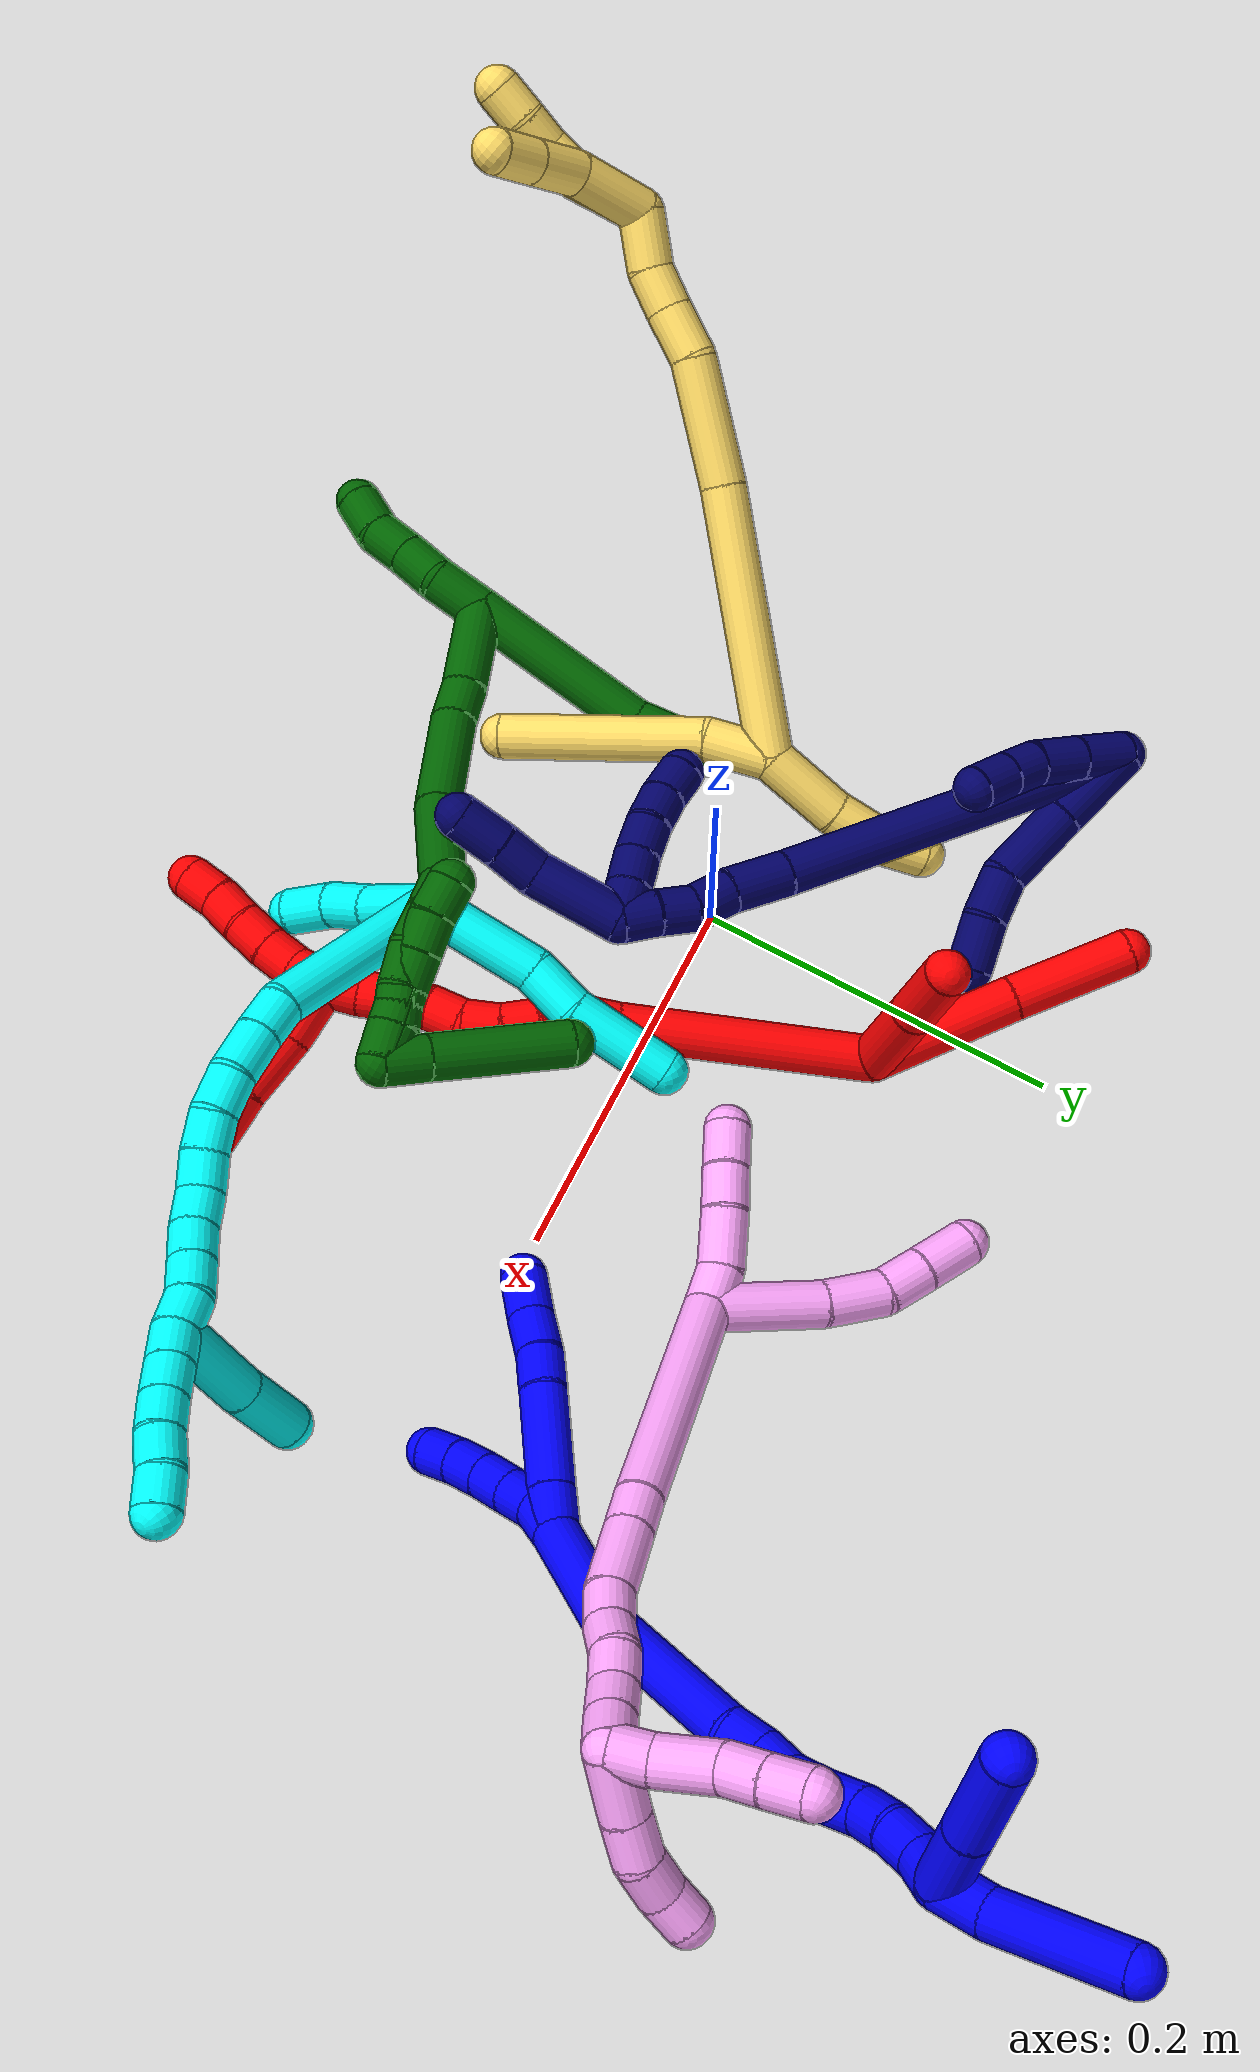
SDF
<sdf version="1.7">
 <world name="default">
  <plugin name="TubeGeneratorPlugin" filename="libtube_generator_plugin.so"/>
  <model name="photoneo_s_sensor">
   <static>1</static>
   <pose>0 0 2 1.57079 1.57079 3.14159</pose>
   <link name="link">
    <inertial><mass>0.1</mass></inertial>
    <sensor name="sensor" type="depth">
     <update_rate>30</update_rate>
     <camera>
      <horizontal_fov>1.22</horizontal_fov>
      <image><width>1920</width><height>1200</height><format>B8G8R8</format></image>
      <clip><near>0.1</near><far>4</far></clip>
      <depth_camera><output>points</output></depth_camera>
     </camera>
     <plugin name="camera_plugin" filename="libgazebo_ros_depth_camera.so">
      <baseline>0.2</baseline>
      <alwaysOn>1</alwaysOn>
      <updateRate>0.0</updateRate>
      <cameraName>camera_ir</cameraName>
      <imageTopicName>/camera/color/image_raw</imageTopicName>
      <cameraInfoTopicName>/camera/color/camera_info</cameraInfoTopicName>
      <depthImageTopicName>/camera/depth/image_raw</depthImageTopicName>
      <depthImageCameraInfoTopicName>/camera/depth/camera_info</depthImageCameraInfoTopicName>
      <pointCloudTopicName>/camera/depth/points</pointCloudTopicName>
      <frameName>fr_optical</frameName>
      <pointCloudCutoff>0.1</pointCloudCutoff>
      <pointCloudCutoffMax>2.0</pointCloudCutoffMax>
      <distortionK1>0</distortionK1>
      <distortionK2>0</distortionK2>
      <distortionK3>0</distortionK3>
      <distortionT1>0</distortionT1>
      <distortionT2>0</distortionT2>
      <CxPrime>0</CxPrime>
      <Cx>0</Cx>
      <Cy>0</Cy>
      <focalLength>0</focalLength>
      <hackBaseline>0</hackBaseline>
     </plugin>
    </sensor>
   </link>
  </model>
  <gravity>0 0 -9.8</gravity>
  <magnetic_field>6e-06 2.3e-05 -4.2e-05</magnetic_field>
  <atmosphere type="adiabatic"/>
  <physics name="default_physics" default="0" type="ode">
   <max_step_size>0.003</max_step_size>
   <real_time_factor>1</real_time_factor>
   <real_time_update_rate>1000</real_time_update_rate>
   <max_contacts>10000</max_contacts>
   <ode>
    <solver>
     <type>quick</type>
     <iters>100</iters>
     <sor>1.3</sor>
     <use_dynamic_moi_rescaling>0</use_dynamic_moi_rescaling>
    </solver>
    <constraints>
     <contact_max_correcting_vel>0</contact_max_correcting_vel>
     <contact_surface_layer>0.001</contact_surface_layer>
     <cfm>0</cfm>
     <erp>0.2</erp>
    </constraints>
   </ode>
  </physics>
  <scene><ambient>0.4 0.4 0.4 1</ambient><background>0.7 0.7 0.7 1</background><shadows>0</shadows></scene>
  <audio><device>default</device></audio>
  <spherical_coordinates>
   <surface_model>EARTH_WGS84</surface_model>
   <latitude_deg>0</latitude_deg>
   <longitude_deg>0</longitude_deg>
   <elevation>0</elevation>
   <heading_deg>0</heading_deg>
  </spherical_coordinates>
  <model name="bin">
   <static>1</static>
   <link name="bottom">
    <collision name="collision-bottom">
     <pose>0 0 -0.01 0 -0 0</pose>
     <geometry><box><size>0.8 0.6 0.02</size></box></geometry>
     <surface>
      <friction><ode><mu>100</mu><mu2>100</mu2></ode></friction>
      <contact><collide_bitmask>65535</collide_bitmask></contact>
     </surface>
    </collision>
   </link>
   <link name="west_wall">
    <collision name="collision-west_wall">
     <pose>-0.41 0 0.1 0 -0 0</pose>
     <geometry><box><size>0.02 0.6 0.2</size></box></geometry>
     <surface>
      <friction><ode><mu>100</mu><mu2>100</mu2></ode></friction>
      <contact><collide_bitmask>65535</collide_bitmask></contact>
     </surface>
    </collision>
   </link>
   <link name="east_wall">
    <collision name="collision-east_wall">
     <pose>0.41 0 0.1 0 -0 0</pose>
     <geometry><box><size>0.02 0.6 0.2</size></box></geometry>
     <surface>
      <friction><ode><mu>100</mu><mu2>100</mu2></ode></friction>
      <contact><collide_bitmask>65535</collide_bitmask></contact>
     </surface>
    </collision>
   </link>
   <link name="south_wall">
    <collision name="collision-south_wall">
     <pose>0 -0.31 0.1 0 -0 0</pose>
     <geometry><box><size>0.8 0.02 0.2</size></box></geometry>
     <surface>
      <friction><ode><mu>100</mu><mu2>100</mu2></ode></friction>
      <contact><collide_bitmask>65535</collide_bitmask></contact>
     </surface>
    </collision>
   </link>
   <link name="north_wall">
    <collision name="collision-north_wall">
     <pose>0 0.31 0.1 0 -0 0</pose>
     <geometry><box><size>0.8 0.02 0.2</size></box></geometry>
     <surface>
      <friction><ode><mu>100</mu><mu2>100</mu2></ode></friction>
      <contact><collide_bitmask>65535</collide_bitmask></contact>
     </surface>
    </collision>
   </link>
  </model>
  <model name="1">
   <static>0</static>
   <link name="1">
    <collision name="collision-cylinder-e_1_2_8">
     <pose>-0.005213 -0.000842 -0.009881 3.05662 -0.48401 -2.8005</pose>
     <geometry><cylinder><radius>0.0125</radius><length>0.022407</length></cylinder></geometry>
     <surface>
      <friction><ode><mu>1.16</mu><mu2>1.16</mu2><slip1>0</slip1><slip2>0</slip2></ode></friction>
      <contact><ode><kp>1e+06</kp><kd>1</kd><max_vel>0</max_vel><min_depth>0.001</min_depth></ode></contact>
     </surface>
    </collision>
    <visual name="visual-cylinder-e_1_2_8">
     <pose>-0.005213 -0.000842 -0.009881 3.05662 -0.48401 -2.8005</pose>
     <geometry><cylinder><radius>0.0125</radius><length>0.022407</length></cylinder></geometry>
     <material><ambient>0 0 1 1</ambient></material>
    </visual>
    <collision name="collision-cylinder-e_2_8_9">
     <pose>-0.02298 -0.003148 -0.044128 3.08154 -0.474985 -2.8947</pose>
     <geometry><cylinder><radius>0.0125</radius><length>0.054897</length></cylinder></geometry>
     <surface>
      <friction><ode><mu>1.16</mu><mu2>1.16</mu2><slip1>0</slip1><slip2>0</slip2></ode></friction>
      <contact><ode><kp>1e+06</kp><kd>1</kd><max_vel>0</max_vel><min_depth>0.001</min_depth></ode></contact>
     </surface>
    </collision>
    <visual name="visual-cylinder-e_2_8_9">
     <pose>-0.02298 -0.003148 -0.044128 3.08154 -0.474985 -2.8947</pose>
     <geometry><cylinder><radius>0.0125</radius><length>0.054897</length></cylinder></geometry>
     <material><ambient>0 0 1 1</ambient></material>
    </visual>
    <collision name="collision-cylinder-e_3_9_10">
     <pose>-0.039474 -0.004809 -0.07886 3.12269 -0.363309 -3.03876</pose>
     <geometry><cylinder><radius>0.0125</radius><length>0.022184</length></cylinder></geometry>
     <surface>
      <friction><ode><mu>1.16</mu><mu2>1.16</mu2><slip1>0</slip1><slip2>0</slip2></ode></friction>
      <contact><ode><kp>1e+06</kp><kd>1</kd><max_vel>0</max_vel><min_depth>0.001</min_depth></ode></contact>
     </surface>
    </collision>
    <visual name="visual-cylinder-e_3_9_10">
     <pose>-0.039474 -0.004809 -0.07886 3.12269 -0.363309 -3.03876</pose>
     <geometry><cylinder><radius>0.0125</radius><length>0.022184</length></cylinder></geometry>
     <material><ambient>0 0 1 1</ambient></material>
    </visual>
    <collision name="collision-cylinder-e_4_10_11">
     <pose>-0.046265 -0.006185 -0.100529 3.03763 -0.245665 -2.34387</pose>
     <geometry><cylinder><radius>0.0125</radius><length>0.023432</length></cylinder></geometry>
     <surface>
      <friction><ode><mu>1.16</mu><mu2>1.16</mu2><slip1>0</slip1><slip2>0</slip2></ode></friction>
      <contact><ode><kp>1e+06</kp><kd>1</kd><max_vel>0</max_vel><min_depth>0.001</min_depth></ode></contact>
     </surface>
    </collision>
    <visual name="visual-cylinder-e_4_10_11">
     <pose>-0.046265 -0.006185 -0.100529 3.03763 -0.245665 -2.34387</pose>
     <geometry><cylinder><radius>0.0125</radius><length>0.023432</length></cylinder></geometry>
     <material><ambient>0 0 1 1</ambient></material>
    </visual>
    <collision name="collision-cylinder-e_5_11_6">
     <pose>-0.053592 -0.008593 -0.124551 3.04527 -0.336987 -2.58936</pose>
     <geometry><cylinder><radius>0.0125</radius><length>0.027079</length></cylinder></geometry>
     <surface>
      <friction><ode><mu>1.16</mu><mu2>1.16</mu2><slip1>0</slip1><slip2>0</slip2></ode></friction>
      <contact><ode><kp>1e+06</kp><kd>1</kd><max_vel>0</max_vel><min_depth>0.001</min_depth></ode></contact>
     </surface>
    </collision>
    <visual name="visual-cylinder-e_5_11_6">
     <pose>-0.053592 -0.008593 -0.124551 3.04527 -0.336987 -2.58936</pose>
     <geometry><cylinder><radius>0.0125</radius><length>0.027079</length></cylinder></geometry>
     <material><ambient>0 0 1 1</ambient></material>
    </visual>
    <collision name="collision-cylinder-e_1_2_12">
     <pose>0.000221 -0.002928 -0.009559 2.84435 0.022059 0.147069</pose>
     <geometry><cylinder><radius>0.0125</radius><length>0.02</length></cylinder></geometry>
     <surface>
      <friction><ode><mu>1.16</mu><mu2>1.16</mu2><slip1>0</slip1><slip2>0</slip2></ode></friction>
      <contact><ode><kp>1e+06</kp><kd>1</kd><max_vel>0</max_vel><min_depth>0.001</min_depth></ode></contact>
     </surface>
    </collision>
    <visual name="visual-cylinder-e_1_2_12">
     <pose>0.000221 -0.002928 -0.009559 2.84435 0.022059 0.147069</pose>
     <geometry><cylinder><radius>0.0125</radius><length>0.02</length></cylinder></geometry>
     <material><ambient>0 0 1 1</ambient></material>
    </visual>
    <collision name="collision-cylinder-e_2_12_13">
     <pose>0.002879 -0.010596 -0.02758 2.63101 0.246294 0.885682</pose>
     <geometry><cylinder><radius>0.0125</radius><length>0.02</length></cylinder></geometry>
     <surface>
      <friction><ode><mu>1.16</mu><mu2>1.16</mu2><slip1>0</slip1><slip2>0</slip2></ode></friction>
      <contact><ode><kp>1e+06</kp><kd>1</kd><max_vel>0</max_vel><min_depth>0.001</min_depth></ode></contact>
     </surface>
    </collision>
    <visual name="visual-cylinder-e_2_12_13">
     <pose>0.002879 -0.010596 -0.02758 2.63101 0.246294 0.885682</pose>
     <geometry><cylinder><radius>0.0125</radius><length>0.02</length></cylinder></geometry>
     <material><ambient>0 0 1 1</ambient></material>
    </visual>
    <collision name="collision-cylinder-e_3_13_14">
     <pose>0.007412 -0.020397 -0.044407 2.59742 0.211054 0.725651</pose>
     <geometry><cylinder><radius>0.0125</radius><length>0.02</length></cylinder></geometry>
     <surface>
      <friction><ode><mu>1.16</mu><mu2>1.16</mu2><slip1>0</slip1><slip2>0</slip2></ode></friction>
      <contact><ode><kp>1e+06</kp><kd>1</kd><max_vel>0</max_vel><min_depth>0.001</min_depth></ode></contact>
     </surface>
    </collision>
    <visual name="visual-cylinder-e_3_13_14">
     <pose>0.007412 -0.020397 -0.044407 2.59742 0.211054 0.725651</pose>
     <geometry><cylinder><radius>0.0125</radius><length>0.02</length></cylinder></geometry>
     <material><ambient>0 0 1 1</ambient></material>
    </visual>
    <collision name="collision-cylinder-e_4_14_15">
     <pose>0.012019 -0.030718 -0.060899 2.56722 0.253899 0.815828</pose>
     <geometry><cylinder><radius>0.0125</radius><length>0.02</length></cylinder></geometry>
     <surface>
      <friction><ode><mu>1.16</mu><mu2>1.16</mu2><slip1>0</slip1><slip2>0</slip2></ode></friction>
      <contact><ode><kp>1e+06</kp><kd>1</kd><max_vel>0</max_vel><min_depth>0.001</min_depth></ode></contact>
     </surface>
    </collision>
    <visual name="visual-cylinder-e_4_14_15">
     <pose>0.012019 -0.030718 -0.060899 2.56722 0.253899 0.815828</pose>
     <geometry><cylinder><radius>0.0125</radius><length>0.02</length></cylinder></geometry>
     <material><ambient>0 0 1 1</ambient></material>
    </visual>
    <collision name="collision-cylinder-e_5_15_5">
     <pose>0.017807 -0.041547 -0.076657 2.51114 0.333795 0.95368</pose>
     <geometry><cylinder><radius>0.0125</radius><length>0.02</length></cylinder></geometry>
     <surface>
      <friction><ode><mu>1.16</mu><mu2>1.16</mu2><slip1>0</slip1><slip2>0</slip2></ode></friction>
      <contact><ode><kp>1e+06</kp><kd>1</kd><max_vel>0</max_vel><min_depth>0.001</min_depth></ode></contact>
     </surface>
    </collision>
    <visual name="visual-cylinder-e_5_15_5">
     <pose>0.017807 -0.041547 -0.076657 2.51114 0.333795 0.95368</pose>
     <geometry><cylinder><radius>0.0125</radius><length>0.02</length></cylinder></geometry>
     <material><ambient>0 0 1 1</ambient></material>
    </visual>
    <collision name="collision-cylinder-e_1_2_16">
     <pose>0.001345 0.008474 0.03283 -0.252589 0.039649 -0.005035</pose>
     <geometry><cylinder><radius>0.0125</radius><length>0.067866</length></cylinder></geometry>
     <surface>
      <friction><ode><mu>1.16</mu><mu2>1.16</mu2><slip1>0</slip1><slip2>0</slip2></ode></friction>
      <contact><ode><kp>1e+06</kp><kd>1</kd><max_vel>0</max_vel><min_depth>0.001</min_depth></ode></contact>
     </surface>
    </collision>
    <visual name="visual-cylinder-e_1_2_16">
     <pose>0.001345 0.008474 0.03283 -0.252589 0.039649 -0.005035</pose>
     <geometry><cylinder><radius>0.0125</radius><length>0.067866</length></cylinder></geometry>
     <material><ambient>0 0 1 1</ambient></material>
    </visual>
    <collision name="collision-cylinder-e_2_16_17">
     <pose>-0.000126 0.037956 0.10259 -0.517245 -0.066179 0.017514</pose>
     <geometry><cylinder><radius>0.0125</radius><length>0.085161</length></cylinder></geometry>
     <surface>
      <friction><ode><mu>1.16</mu><mu2>1.16</mu2><slip1>0</slip1><slip2>0</slip2></ode></friction>
      <contact><ode><kp>1e+06</kp><kd>1</kd><max_vel>0</max_vel><min_depth>0.001</min_depth></ode></contact>
     </surface>
    </collision>
    <visual name="visual-cylinder-e_2_16_17">
     <pose>-0.000126 0.037956 0.10259 -0.517245 -0.066179 0.017514</pose>
     <geometry><cylinder><radius>0.0125</radius><length>0.085161</length></cylinder></geometry>
     <material><ambient>0 0 1 1</ambient></material>
    </visual>
    <collision name="collision-cylinder-e_3_17_18">
     <pose>-0.003155 0.065883 0.147116 -0.73862 -0.020778 0.008043</pose>
     <geometry><cylinder><radius>0.0125</radius><length>0.020553</length></cylinder></geometry>
     <surface>
      <friction><ode><mu>1.16</mu><mu2>1.16</mu2><slip1>0</slip1><slip2>0</slip2></ode></friction>
      <contact><ode><kp>1e+06</kp><kd>1</kd><max_vel>0</max_vel><min_depth>0.001</min_depth></ode></contact>
     </surface>
    </collision>
    <visual name="visual-cylinder-e_3_17_18">
     <pose>-0.003155 0.065883 0.147116 -0.73862 -0.020778 0.008043</pose>
     <geometry><cylinder><radius>0.0125</radius><length>0.020553</length></cylinder></geometry>
     <material><ambient>0 0 1 1</ambient></material>
    </visual>
    <collision name="collision-cylinder-e_4_18_19">
     <pose>-0.004203 0.077256 0.163874 -0.452665 -0.08175 0.018835</pose>
     <geometry><cylinder><radius>0.0125</radius><length>0.020442</length></cylinder></geometry>
     <surface>
      <friction><ode><mu>1.16</mu><mu2>1.16</mu2><slip1>0</slip1><slip2>0</slip2></ode></friction>
      <contact><ode><kp>1e+06</kp><kd>1</kd><max_vel>0</max_vel><min_depth>0.001</min_depth></ode></contact>
     </surface>
    </collision>
    <visual name="visual-cylinder-e_4_18_19">
     <pose>-0.004203 0.077256 0.163874 -0.452665 -0.08175 0.018835</pose>
     <geometry><cylinder><radius>0.0125</radius><length>0.020442</length></cylinder></geometry>
     <material><ambient>0 0 1 1</ambient></material>
    </visual>
    <collision name="collision-cylinder-e_5_19_20">
     <pose>-0.009028 0.086333 0.182195 -0.467219 -0.370908 0.089226</pose>
     <geometry><cylinder><radius>0.0125</radius><length>0.022017</length></cylinder></geometry>
     <surface>
      <friction><ode><mu>1.16</mu><mu2>1.16</mu2><slip1>0</slip1><slip2>0</slip2></ode></friction>
      <contact><ode><kp>1e+06</kp><kd>1</kd><max_vel>0</max_vel><min_depth>0.001</min_depth></ode></contact>
     </surface>
    </collision>
    <visual name="visual-cylinder-e_5_19_20">
     <pose>-0.009028 0.086333 0.182195 -0.467219 -0.370908 0.089226</pose>
     <geometry><cylinder><radius>0.0125</radius><length>0.022017</length></cylinder></geometry>
     <material><ambient>0 0 1 1</ambient></material>
    </visual>
    <collision name="collision-cylinder-e_6_20_21">
     <pose>-0.016778 0.097583 0.199892 -0.660268 -0.334773 0.115673</pose>
     <geometry><cylinder><radius>0.0125</radius><length>0.022887</length></cylinder></geometry>
     <surface>
      <friction><ode><mu>1.16</mu><mu2>1.16</mu2><slip1>0</slip1><slip2>0</slip2></ode></friction>
      <contact><ode><kp>1e+06</kp><kd>1</kd><max_vel>0</max_vel><min_depth>0.001</min_depth></ode></contact>
     </surface>
    </collision>
    <visual name="visual-cylinder-e_6_20_21">
     <pose>-0.016778 0.097583 0.199892 -0.660268 -0.334773 0.115673</pose>
     <geometry><cylinder><radius>0.0125</radius><length>0.022887</length></cylinder></geometry>
     <material><ambient>0 0 1 1</ambient></material>
    </visual>
    <collision name="collision-cylinder-e_7_21_22">
     <pose>-0.02377 0.107622 0.217299 -0.367027 -0.327789 0.06137</pose>
     <geometry><cylinder><radius>0.0125</radius><length>0.020076</length></cylinder></geometry>
     <surface>
      <friction><ode><mu>1.16</mu><mu2>1.16</mu2><slip1>0</slip1><slip2>0</slip2></ode></friction>
      <contact><ode><kp>1e+06</kp><kd>1</kd><max_vel>0</max_vel><min_depth>0.001</min_depth></ode></contact>
     </surface>
    </collision>
    <visual name="visual-cylinder-e_7_21_22">
     <pose>-0.02377 0.107622 0.217299 -0.367027 -0.327789 0.06137</pose>
     <geometry><cylinder><radius>0.0125</radius><length>0.020076</length></cylinder></geometry>
     <material><ambient>0 0 1 1</ambient></material>
    </visual>
    <collision name="collision-cylinder-e_8_22_23">
     <pose>-0.028175 0.115239 0.235513 -0.423088 -0.11405 0.024518</pose>
     <geometry><cylinder><radius>0.0125</radius><length>0.020626</length></cylinder></geometry>
     <surface>
      <friction><ode><mu>1.16</mu><mu2>1.16</mu2><slip1>0</slip1><slip2>0</slip2></ode></friction>
      <contact><ode><kp>1e+06</kp><kd>1</kd><max_vel>0</max_vel><min_depth>0.001</min_depth></ode></contact>
     </surface>
    </collision>
    <visual name="visual-cylinder-e_8_22_23">
     <pose>-0.028175 0.115239 0.235513 -0.423088 -0.11405 0.024518</pose>
     <geometry><cylinder><radius>0.0125</radius><length>0.020626</length></cylinder></geometry>
     <material><ambient>0 0 1 1</ambient></material>
    </visual>
    <collision name="collision-cylinder-e_9_23_1">
     <pose>-0.031057 0.120282 0.254862 -0.083344 -0.16848 0.007042</pose>
     <geometry><cylinder><radius>0.0125</radius><length>0.020371</length></cylinder></geometry>
     <surface>
      <friction><ode><mu>1.16</mu><mu2>1.16</mu2><slip1>0</slip1><slip2>0</slip2></ode></friction>
      <contact><ode><kp>1e+06</kp><kd>1</kd><max_vel>0</max_vel><min_depth>0.001</min_depth></ode></contact>
     </surface>
    </collision>
    <visual name="visual-cylinder-e_9_23_1">
     <pose>-0.031057 0.120282 0.254862 -0.083344 -0.16848 0.007042</pose>
     <geometry><cylinder><radius>0.0125</radius><length>0.020371</length></cylinder></geometry>
     <material><ambient>0 0 1 1</ambient></material>
    </visual>
    <collision name="collision-cylinder-e_1_1_24">
     <pose>-0.034449 0.129574 0.274659 -0.712381 -0.129423 0.048211</pose>
     <geometry><cylinder><radius>0.0125</radius><length>0.026092</length></cylinder></geometry>
     <surface>
      <friction><ode><mu>1.16</mu><mu2>1.16</mu2><slip1>0</slip1><slip2>0</slip2></ode></friction>
      <contact><ode><kp>1e+06</kp><kd>1</kd><max_vel>0</max_vel><min_depth>0.001</min_depth></ode></contact>
     </surface>
    </collision>
    <visual name="visual-cylinder-e_1_1_24">
     <pose>-0.034449 0.129574 0.274659 -0.712381 -0.129423 0.048211</pose>
     <geometry><cylinder><radius>0.0125</radius><length>0.026092</length></cylinder></geometry>
     <material><ambient>0 0 1 1</ambient></material>
    </visual>
    <collision name="collision-cylinder-e_2_24_4">
     <pose>-0.048687 0.159548 0.311744 -0.667618 -0.346641 0.12128</pose>
     <geometry><cylinder><radius>0.0125</radius><length>0.073908</length></cylinder></geometry>
     <surface>
      <friction><ode><mu>1.16</mu><mu2>1.16</mu2><slip1>0</slip1><slip2>0</slip2></ode></friction>
      <contact><ode><kp>1e+06</kp><kd>1</kd><max_vel>0</max_vel><min_depth>0.001</min_depth></ode></contact>
     </surface>
    </collision>
    <visual name="visual-cylinder-e_2_24_4">
     <pose>-0.048687 0.159548 0.311744 -0.667618 -0.346641 0.12128</pose>
     <geometry><cylinder><radius>0.0125</radius><length>0.073908</length></cylinder></geometry>
     <material><ambient>0 0 1 1</ambient></material>
    </visual>
    <collision name="collision-cylinder-e_1_1_25">
     <pose>-0.053697 0.118833 0.271018 0.355718 -1.26712 -0.262575</pose>
     <geometry><cylinder><radius>0.0125</radius><length>0.043872</length></cylinder></geometry>
     <surface>
      <friction><ode><mu>1.16</mu><mu2>1.16</mu2><slip1>0</slip1><slip2>0</slip2></ode></friction>
      <contact><ode><kp>1e+06</kp><kd>1</kd><max_vel>0</max_vel><min_depth>0.001</min_depth></ode></contact>
     </surface>
    </collision>
    <visual name="visual-cylinder-e_1_1_25">
     <pose>-0.053697 0.118833 0.271018 0.355718 -1.26712 -0.262575</pose>
     <geometry><cylinder><radius>0.0125</radius><length>0.043872</length></cylinder></geometry>
     <material><ambient>0 0 1 1</ambient></material>
    </visual>
    <collision name="collision-cylinder-e_2_25_3">
     <pose>-0.10141 0.113601 0.285023 0.358916 -1.26714 -0.264965</pose>
     <geometry><cylinder><radius>0.0125</radius><length>0.056128</length></cylinder></geometry>
     <surface>
      <friction><ode><mu>1.16</mu><mu2>1.16</mu2><slip1>0</slip1><slip2>0</slip2></ode></friction>
      <contact><ode><kp>1e+06</kp><kd>1</kd><max_vel>0</max_vel><min_depth>0.001</min_depth></ode></contact>
     </surface>
    </collision>
    <visual name="visual-cylinder-e_2_25_3">
     <pose>-0.10141 0.113601 0.285023 0.358916 -1.26714 -0.264965</pose>
     <geometry><cylinder><radius>0.0125</radius><length>0.056128</length></cylinder></geometry>
     <material><ambient>0 0 1 1</ambient></material>
    </visual>
    <collision name="collision-sphere-3">
     <pose>-0.12819 0.110654 0.29288 0 -0 0</pose>
     <geometry><sphere><radius>0.0125</radius></sphere></geometry>
     <surface>
      <friction><ode><mu>1.16</mu><mu2>1.16</mu2><slip1>0</slip1><slip2>0</slip2></ode></friction>
      <contact><ode><kp>1e+06</kp><kd>1</kd><max_vel>0</max_vel><min_depth>0.001</min_depth></ode></contact>
     </surface>
    </collision>
    <visual name="visual-sphere-3">
     <pose>-0.12819 0.110654 0.29288 0 -0 0</pose>
     <geometry><sphere><radius>0.0125</radius></sphere></geometry>
     <material><ambient>0 0 1 1</ambient></material>
    </visual>
    <collision name="collision-sphere-25">
     <pose>-0.07463 0.116549 0.277167 0 -0 0</pose>
     <geometry><sphere><radius>0.0125</radius></sphere></geometry>
     <surface>
      <friction><ode><mu>1.16</mu><mu2>1.16</mu2><slip1>0</slip1><slip2>0</slip2></ode></friction>
      <contact><ode><kp>1e+06</kp><kd>1</kd><max_vel>0</max_vel><min_depth>0.001</min_depth></ode></contact>
     </surface>
    </collision>
    <visual name="visual-sphere-25">
     <pose>-0.07463 0.116549 0.277167 0 -0 0</pose>
     <geometry><sphere><radius>0.0125</radius></sphere></geometry>
     <material><ambient>0 0 1 1</ambient></material>
    </visual>
    <collision name="collision-sphere-4">
     <pose>-0.061242 0.181066 0.339038 0 -0 0</pose>
     <geometry><sphere><radius>0.0125</radius></sphere></geometry>
     <surface>
      <friction><ode><mu>1.16</mu><mu2>1.16</mu2><slip1>0</slip1><slip2>0</slip2></ode></friction>
      <contact><ode><kp>1e+06</kp><kd>1</kd><max_vel>0</max_vel><min_depth>0.001</min_depth></ode></contact>
     </surface>
    </collision>
    <visual name="visual-sphere-4">
     <pose>-0.061242 0.181066 0.339038 0 -0 0</pose>
     <geometry><sphere><radius>0.0125</radius></sphere></geometry>
     <material><ambient>0 0 1 1</ambient></material>
    </visual>
    <collision name="collision-sphere-24">
     <pose>-0.036132 0.13803 0.28445 0 -0 0</pose>
     <geometry><sphere><radius>0.0125</radius></sphere></geometry>
     <surface>
      <friction><ode><mu>1.16</mu><mu2>1.16</mu2><slip1>0</slip1><slip2>0</slip2></ode></friction>
      <contact><ode><kp>1e+06</kp><kd>1</kd><max_vel>0</max_vel><min_depth>0.001</min_depth></ode></contact>
     </surface>
    </collision>
    <visual name="visual-sphere-24">
     <pose>-0.036132 0.13803 0.28445 0 -0 0</pose>
     <geometry><sphere><radius>0.0125</radius></sphere></geometry>
     <material><ambient>0 0 1 1</ambient></material>
    </visual>
    <collision name="collision-sphere-1">
     <pose>-0.032765 0.121118 0.264869 0 -0 0</pose>
     <geometry><sphere><radius>0.0125</radius></sphere></geometry>
     <surface>
      <friction><ode><mu>1.16</mu><mu2>1.16</mu2><slip1>0</slip1><slip2>0</slip2></ode></friction>
      <contact><ode><kp>1e+06</kp><kd>1</kd><max_vel>0</max_vel><min_depth>0.001</min_depth></ode></contact>
     </surface>
    </collision>
    <visual name="visual-sphere-1">
     <pose>-0.032765 0.121118 0.264869 0 -0 0</pose>
     <geometry><sphere><radius>0.0125</radius></sphere></geometry>
     <material><ambient>0 0 1 1</ambient></material>
    </visual>
    <collision name="collision-sphere-23">
     <pose>-0.029349 0.119446 0.244855 0 -0 0</pose>
     <geometry><sphere><radius>0.0125</radius></sphere></geometry>
     <surface>
      <friction><ode><mu>1.16</mu><mu2>1.16</mu2><slip1>0</slip1><slip2>0</slip2></ode></friction>
      <contact><ode><kp>1e+06</kp><kd>1</kd><max_vel>0</max_vel><min_depth>0.001</min_depth></ode></contact>
     </surface>
    </collision>
    <visual name="visual-sphere-23">
     <pose>-0.029349 0.119446 0.244855 0 -0 0</pose>
     <geometry><sphere><radius>0.0125</radius></sphere></geometry>
     <material><ambient>0 0 1 1</ambient></material>
    </visual>
    <collision name="collision-sphere-22">
     <pose>-0.027001 0.111032 0.22617 0 -0 0</pose>
     <geometry><sphere><radius>0.0125</radius></sphere></geometry>
     <surface>
      <friction><ode><mu>1.16</mu><mu2>1.16</mu2><slip1>0</slip1><slip2>0</slip2></ode></friction>
      <contact><ode><kp>1e+06</kp><kd>1</kd><max_vel>0</max_vel><min_depth>0.001</min_depth></ode></contact>
     </surface>
    </collision>
    <visual name="visual-sphere-22">
     <pose>-0.027001 0.111032 0.22617 0 -0 0</pose>
     <geometry><sphere><radius>0.0125</radius></sphere></geometry>
     <material><ambient>0 0 1 1</ambient></material>
    </visual>
    <collision name="collision-sphere-21">
     <pose>-0.020538 0.104212 0.208429 0 -0 0</pose>
     <geometry><sphere><radius>0.0125</radius></sphere></geometry>
     <surface>
      <friction><ode><mu>1.16</mu><mu2>1.16</mu2><slip1>0</slip1><slip2>0</slip2></ode></friction>
      <contact><ode><kp>1e+06</kp><kd>1</kd><max_vel>0</max_vel><min_depth>0.001</min_depth></ode></contact>
     </surface>
    </collision>
    <visual name="visual-sphere-21">
     <pose>-0.020538 0.104212 0.208429 0 -0 0</pose>
     <geometry><sphere><radius>0.0125</radius></sphere></geometry>
     <material><ambient>0 0 1 1</ambient></material>
    </visual>
    <collision name="collision-sphere-6">
     <pose>-0.058069 -0.009822 -0.13727 0 -0 0</pose>
     <geometry><sphere><radius>0.0125</radius></sphere></geometry>
     <surface>
      <friction><ode><mu>1.16</mu><mu2>1.16</mu2><slip1>0</slip1><slip2>0</slip2></ode></friction>
      <contact><ode><kp>1e+06</kp><kd>1</kd><max_vel>0</max_vel><min_depth>0.001</min_depth></ode></contact>
     </surface>
    </collision>
    <visual name="visual-sphere-6">
     <pose>-0.058069 -0.009822 -0.13727 0 -0 0</pose>
     <geometry><sphere><radius>0.0125</radius></sphere></geometry>
     <material><ambient>0 0 1 1</ambient></material>
    </visual>
    <collision name="collision-sphere-11">
     <pose>-0.049115 -0.007364 -0.111832 0 -0 0</pose>
     <geometry><sphere><radius>0.0125</radius></sphere></geometry>
     <surface>
      <friction><ode><mu>1.16</mu><mu2>1.16</mu2><slip1>0</slip1><slip2>0</slip2></ode></friction>
      <contact><ode><kp>1e+06</kp><kd>1</kd><max_vel>0</max_vel><min_depth>0.001</min_depth></ode></contact>
     </surface>
    </collision>
    <visual name="visual-sphere-11">
     <pose>-0.049115 -0.007364 -0.111832 0 -0 0</pose>
     <geometry><sphere><radius>0.0125</radius></sphere></geometry>
     <material><ambient>0 0 1 1</ambient></material>
    </visual>
    <collision name="collision-sphere-10">
     <pose>-0.043416 -0.005005 -0.089226 0 -0 0</pose>
     <geometry><sphere><radius>0.0125</radius></sphere></geometry>
     <surface>
      <friction><ode><mu>1.16</mu><mu2>1.16</mu2><slip1>0</slip1><slip2>0</slip2></ode></friction>
      <contact><ode><kp>1e+06</kp><kd>1</kd><max_vel>0</max_vel><min_depth>0.001</min_depth></ode></contact>
     </surface>
    </collision>
    <visual name="visual-sphere-10">
     <pose>-0.043416 -0.005005 -0.089226 0 -0 0</pose>
     <geometry><sphere><radius>0.0125</radius></sphere></geometry>
     <material><ambient>0 0 1 1</ambient></material>
    </visual>
    <collision name="collision-sphere-9">
     <pose>-0.035533 -0.004613 -0.068494 0 -0 0</pose>
     <geometry><sphere><radius>0.0125</radius></sphere></geometry>
     <surface>
      <friction><ode><mu>1.16</mu><mu2>1.16</mu2><slip1>0</slip1><slip2>0</slip2></ode></friction>
      <contact><ode><kp>1e+06</kp><kd>1</kd><max_vel>0</max_vel><min_depth>0.001</min_depth></ode></contact>
     </surface>
    </collision>
    <visual name="visual-sphere-9">
     <pose>-0.035533 -0.004613 -0.068494 0 -0 0</pose>
     <geometry><sphere><radius>0.0125</radius></sphere></geometry>
     <material><ambient>0 0 1 1</ambient></material>
    </visual>
    <collision name="collision-sphere-2">
     <geometry><sphere><radius>0.0125</radius></sphere></geometry>
     <surface>
      <friction><ode><mu>1.16</mu><mu2>1.16</mu2><slip1>0</slip1><slip2>0</slip2></ode></friction>
      <contact><ode><kp>1e+06</kp><kd>1</kd><max_vel>0</max_vel><min_depth>0.001</min_depth></ode></contact>
     </surface>
    </collision>
    <visual name="visual-sphere-2">
     <geometry><sphere><radius>0.0125</radius></sphere></geometry>
     <material><ambient>0 0 1 1</ambient></material>
    </visual>
    <collision name="collision-sphere-19">
     <pose>-0.005038 0.081712 0.173035 0 -0 0</pose>
     <geometry><sphere><radius>0.0125</radius></sphere></geometry>
     <surface>
      <friction><ode><mu>1.16</mu><mu2>1.16</mu2><slip1>0</slip1><slip2>0</slip2></ode></friction>
      <contact><ode><kp>1e+06</kp><kd>1</kd><max_vel>0</max_vel><min_depth>0.001</min_depth></ode></contact>
     </surface>
    </collision>
    <visual name="visual-sphere-19">
     <pose>-0.005038 0.081712 0.173035 0 -0 0</pose>
     <geometry><sphere><radius>0.0125</radius></sphere></geometry>
     <material><ambient>0 0 1 1</ambient></material>
    </visual>
    <collision name="collision-sphere-8">
     <pose>-0.010427 -0.001683 -0.019762 0 -0 0</pose>
     <geometry><sphere><radius>0.0125</radius></sphere></geometry>
     <surface>
      <friction><ode><mu>1.16</mu><mu2>1.16</mu2><slip1>0</slip1><slip2>0</slip2></ode></friction>
      <contact><ode><kp>1e+06</kp><kd>1</kd><max_vel>0</max_vel><min_depth>0.001</min_depth></ode></contact>
     </surface>
    </collision>
    <visual name="visual-sphere-8">
     <pose>-0.010427 -0.001683 -0.019762 0 -0 0</pose>
     <geometry><sphere><radius>0.0125</radius></sphere></geometry>
     <material><ambient>0 0 1 1</ambient></material>
    </visual>
    <collision name="collision-sphere-12">
     <pose>0.000441 -0.005856 -0.019118 0 -0 0</pose>
     <geometry><sphere><radius>0.0125</radius></sphere></geometry>
     <surface>
      <friction><ode><mu>1.16</mu><mu2>1.16</mu2><slip1>0</slip1><slip2>0</slip2></ode></friction>
      <contact><ode><kp>1e+06</kp><kd>1</kd><max_vel>0</max_vel><min_depth>0.001</min_depth></ode></contact>
     </surface>
    </collision>
    <visual name="visual-sphere-12">
     <pose>0.000441 -0.005856 -0.019118 0 -0 0</pose>
     <geometry><sphere><radius>0.0125</radius></sphere></geometry>
     <material><ambient>0 0 1 1</ambient></material>
    </visual>
    <collision name="collision-sphere-13">
     <pose>0.005317 -0.015335 -0.036041 0 -0 0</pose>
     <geometry><sphere><radius>0.0125</radius></sphere></geometry>
     <surface>
      <friction><ode><mu>1.16</mu><mu2>1.16</mu2><slip1>0</slip1><slip2>0</slip2></ode></friction>
      <contact><ode><kp>1e+06</kp><kd>1</kd><max_vel>0</max_vel><min_depth>0.001</min_depth></ode></contact>
     </surface>
    </collision>
    <visual name="visual-sphere-13">
     <pose>0.005317 -0.015335 -0.036041 0 -0 0</pose>
     <geometry><sphere><radius>0.0125</radius></sphere></geometry>
     <material><ambient>0 0 1 1</ambient></material>
    </visual>
    <collision name="collision-sphere-14">
     <pose>0.009507 -0.025459 -0.052772 0 -0 0</pose>
     <geometry><sphere><radius>0.0125</radius></sphere></geometry>
     <surface>
      <friction><ode><mu>1.16</mu><mu2>1.16</mu2><slip1>0</slip1><slip2>0</slip2></ode></friction>
      <contact><ode><kp>1e+06</kp><kd>1</kd><max_vel>0</max_vel><min_depth>0.001</min_depth></ode></contact>
     </surface>
    </collision>
    <visual name="visual-sphere-14">
     <pose>0.009507 -0.025459 -0.052772 0 -0 0</pose>
     <geometry><sphere><radius>0.0125</radius></sphere></geometry>
     <material><ambient>0 0 1 1</ambient></material>
    </visual>
    <collision name="collision-sphere-15">
     <pose>0.014531 -0.035977 -0.069025 0 -0 0</pose>
     <geometry><sphere><radius>0.0125</radius></sphere></geometry>
     <surface>
      <friction><ode><mu>1.16</mu><mu2>1.16</mu2><slip1>0</slip1><slip2>0</slip2></ode></friction>
      <contact><ode><kp>1e+06</kp><kd>1</kd><max_vel>0</max_vel><min_depth>0.001</min_depth></ode></contact>
     </surface>
    </collision>
    <visual name="visual-sphere-15">
     <pose>0.014531 -0.035977 -0.069025 0 -0 0</pose>
     <geometry><sphere><radius>0.0125</radius></sphere></geometry>
     <material><ambient>0 0 1 1</ambient></material>
    </visual>
    <collision name="collision-sphere-5">
     <pose>0.021083 -0.047117 -0.084288 0 -0 0</pose>
     <geometry><sphere><radius>0.0125</radius></sphere></geometry>
     <surface>
      <friction><ode><mu>1.16</mu><mu2>1.16</mu2><slip1>0</slip1><slip2>0</slip2></ode></friction>
      <contact><ode><kp>1e+06</kp><kd>1</kd><max_vel>0</max_vel><min_depth>0.001</min_depth></ode></contact>
     </surface>
    </collision>
    <visual name="visual-sphere-5">
     <pose>0.021083 -0.047117 -0.084288 0 -0 0</pose>
     <geometry><sphere><radius>0.0125</radius></sphere></geometry>
     <material><ambient>0 0 1 1</ambient></material>
    </visual>
    <collision name="collision-sphere-16">
     <pose>0.00269 0.016947 0.065661 0 -0 0</pose>
     <geometry><sphere><radius>0.0125</radius></sphere></geometry>
     <surface>
      <friction><ode><mu>1.16</mu><mu2>1.16</mu2><slip1>0</slip1><slip2>0</slip2></ode></friction>
      <contact><ode><kp>1e+06</kp><kd>1</kd><max_vel>0</max_vel><min_depth>0.001</min_depth></ode></contact>
     </surface>
    </collision>
    <visual name="visual-sphere-16">
     <pose>0.00269 0.016947 0.065661 0 -0 0</pose>
     <geometry><sphere><radius>0.0125</radius></sphere></geometry>
     <material><ambient>0 0 1 1</ambient></material>
    </visual>
    <collision name="collision-sphere-17">
     <pose>-0.002942 0.058966 0.139519 0 -0 0</pose>
     <geometry><sphere><radius>0.0125</radius></sphere></geometry>
     <surface>
      <friction><ode><mu>1.16</mu><mu2>1.16</mu2><slip1>0</slip1><slip2>0</slip2></ode></friction>
      <contact><ode><kp>1e+06</kp><kd>1</kd><max_vel>0</max_vel><min_depth>0.001</min_depth></ode></contact>
     </surface>
    </collision>
    <visual name="visual-sphere-17">
     <pose>-0.002942 0.058966 0.139519 0 -0 0</pose>
     <geometry><sphere><radius>0.0125</radius></sphere></geometry>
     <material><ambient>0 0 1 1</ambient></material>
    </visual>
    <collision name="collision-sphere-18">
     <pose>-0.003369 0.072801 0.154713 0 -0 0</pose>
     <geometry><sphere><radius>0.0125</radius></sphere></geometry>
     <surface>
      <friction><ode><mu>1.16</mu><mu2>1.16</mu2><slip1>0</slip1><slip2>0</slip2></ode></friction>
      <contact><ode><kp>1e+06</kp><kd>1</kd><max_vel>0</max_vel><min_depth>0.001</min_depth></ode></contact>
     </surface>
    </collision>
    <visual name="visual-sphere-18">
     <pose>-0.003369 0.072801 0.154713 0 -0 0</pose>
     <geometry><sphere><radius>0.0125</radius></sphere></geometry>
     <material><ambient>0 0 1 1</ambient></material>
    </visual>
    <collision name="collision-sphere-20">
     <pose>-0.013018 0.090954 0.191356 0 -0 0</pose>
     <geometry><sphere><radius>0.0125</radius></sphere></geometry>
     <surface>
      <friction><ode><mu>1.16</mu><mu2>1.16</mu2><slip1>0</slip1><slip2>0</slip2></ode></friction>
      <contact><ode><kp>1e+06</kp><kd>1</kd><max_vel>0</max_vel><min_depth>0.001</min_depth></ode></contact>
     </surface>
    </collision>
    <visual name="visual-sphere-20">
     <pose>-0.013018 0.090954 0.191356 0 -0 0</pose>
     <geometry><sphere><radius>0.0125</radius></sphere></geometry>
     <material><ambient>0 0 1 1</ambient></material>
    </visual>
    <inertial>
     <pose>-0.025162 0.055768 0.111904 0 -0 0</pose>
     <mass>0.75</mass>
     <inertia><ixx>0.000109</ixx><ixy>0</ixy><ixz>0</ixz><iyy>0.000171</iyy><iyz>0</iyz><izz>8e-06</izz></inertia>
    </inertial>
   </link>
   <pose>0.333493 0.086063 0.069151 -0.445373 0.679311 0.111959</pose>
  </model>
  <model name="2">
   <static>0</static>
   <link name="2">
    <collision name="collision-cylinder-e_1_2_8">
     <pose>-0.034965 0.021528 -0.001807 -1.65454 -1.01734 1.0902</pose>
     <geometry><cylinder><radius>0.0125</radius><length>0.082201</length></cylinder></geometry>
     <surface>
      <friction><ode><mu>1.16</mu><mu2>1.16</mu2><slip1>0</slip1><slip2>0</slip2></ode></friction>
      <contact><ode><kp>1e+06</kp><kd>1</kd><max_vel>0</max_vel><min_depth>0.001</min_depth></ode></contact>
     </surface>
    </collision>
    <visual name="visual-cylinder-e_1_2_8">
     <pose>-0.034965 0.021528 -0.001807 -1.65454 -1.01734 1.0902</pose>
     <geometry><cylinder><radius>0.0125</radius><length>0.082201</length></cylinder></geometry>
     <material><ambient>1 0 0 1</ambient></material>
    </visual>
    <collision name="collision-cylinder-e_2_8_6">
     <pose>-0.098506 0.061277 -0.004342 -1.61073 -1.00281 1.03684</pose>
     <geometry><cylinder><radius>0.0125</radius><length>0.067799</length></cylinder></geometry>
     <surface>
      <friction><ode><mu>1.16</mu><mu2>1.16</mu2><slip1>0</slip1><slip2>0</slip2></ode></friction>
      <contact><ode><kp>1e+06</kp><kd>1</kd><max_vel>0</max_vel><min_depth>0.001</min_depth></ode></contact>
     </surface>
    </collision>
    <visual name="visual-cylinder-e_2_8_6">
     <pose>-0.098506 0.061277 -0.004342 -1.61073 -1.00281 1.03684</pose>
     <geometry><cylinder><radius>0.0125</radius><length>0.067799</length></cylinder></geometry>
     <material><ambient>1 0 0 1</ambient></material>
    </visual>
    <collision name="collision-cylinder-e_1_2_9">
     <pose>-0.016799 -0.005669 0.021111 0.262328 -0.655243 -0.089612</pose>
     <geometry><cylinder><radius>0.0125</radius><length>0.055137</length></cylinder></geometry>
     <surface>
      <friction><ode><mu>1.16</mu><mu2>1.16</mu2><slip1>0</slip1><slip2>0</slip2></ode></friction>
      <contact><ode><kp>1e+06</kp><kd>1</kd><max_vel>0</max_vel><min_depth>0.001</min_depth></ode></contact>
     </surface>
    </collision>
    <visual name="visual-cylinder-e_1_2_9">
     <pose>-0.016799 -0.005669 0.021111 0.262328 -0.655243 -0.089612</pose>
     <geometry><cylinder><radius>0.0125</radius><length>0.055137</length></cylinder></geometry>
     <material><ambient>1 0 0 1</ambient></material>
    </visual>
    <collision name="collision-cylinder-e_2_9_5">
     <pose>-0.047034 -0.016059 0.059553 0.265978 -0.642219 -0.088936</pose>
     <geometry><cylinder><radius>0.0125</radius><length>0.044863</length></cylinder></geometry>
     <surface>
      <friction><ode><mu>1.16</mu><mu2>1.16</mu2><slip1>0</slip1><slip2>0</slip2></ode></friction>
      <contact><ode><kp>1e+06</kp><kd>1</kd><max_vel>0</max_vel><min_depth>0.001</min_depth></ode></contact>
     </surface>
    </collision>
    <visual name="visual-cylinder-e_2_9_5">
     <pose>-0.047034 -0.016059 0.059553 0.265978 -0.642219 -0.088936</pose>
     <geometry><cylinder><radius>0.0125</radius><length>0.044863</length></cylinder></geometry>
     <material><ambient>1 0 0 1</ambient></material>
    </visual>
    <collision name="collision-cylinder-e_1_2_10">
     <pose>0.033211 -0.059753 -0.006699 1.68244 0.504649 0.561449</pose>
     <geometry><cylinder><radius>0.0125</radius><length>0.137379</length></cylinder></geometry>
     <surface>
      <friction><ode><mu>1.16</mu><mu2>1.16</mu2><slip1>0</slip1><slip2>0</slip2></ode></friction>
      <contact><ode><kp>1e+06</kp><kd>1</kd><max_vel>0</max_vel><min_depth>0.001</min_depth></ode></contact>
     </surface>
    </collision>
    <visual name="visual-cylinder-e_1_2_10">
     <pose>0.033211 -0.059753 -0.006699 1.68244 0.504649 0.561449</pose>
     <geometry><cylinder><radius>0.0125</radius><length>0.137379</length></cylinder></geometry>
     <material><ambient>1 0 0 1</ambient></material>
    </visual>
    <collision name="collision-cylinder-e_2_10_11">
     <pose>0.070999 -0.12966 -0.014091 1.63898 0.422522 0.451389</pose>
     <geometry><cylinder><radius>0.0125</radius><length>0.02232</length></cylinder></geometry>
     <surface>
      <friction><ode><mu>1.16</mu><mu2>1.16</mu2><slip1>0</slip1><slip2>0</slip2></ode></friction>
      <contact><ode><kp>1e+06</kp><kd>1</kd><max_vel>0</max_vel><min_depth>0.001</min_depth></ode></contact>
     </surface>
    </collision>
    <visual name="visual-cylinder-e_2_10_11">
     <pose>0.070999 -0.12966 -0.014091 1.63898 0.422522 0.451389</pose>
     <geometry><cylinder><radius>0.0125</radius><length>0.02232</length></cylinder></geometry>
     <material><ambient>1 0 0 1</ambient></material>
    </visual>
    <collision name="collision-cylinder-e_3_11_12">
     <pose>0.08232 -0.147352 -0.013995 1.46645 0.727261 0.660456</pose>
     <geometry><cylinder><radius>0.0125</radius><length>0.02029</length></cylinder></geometry>
     <surface>
      <friction><ode><mu>1.16</mu><mu2>1.16</mu2><slip1>0</slip1><slip2>0</slip2></ode></friction>
      <contact><ode><kp>1e+06</kp><kd>1</kd><max_vel>0</max_vel><min_depth>0.001</min_depth></ode></contact>
     </surface>
    </collision>
    <visual name="visual-cylinder-e_3_11_12">
     <pose>0.08232 -0.147352 -0.013995 1.46645 0.727261 0.660456</pose>
     <geometry><cylinder><radius>0.0125</radius><length>0.02029</length></cylinder></geometry>
     <material><ambient>1 0 0 1</ambient></material>
    </visual>
    <collision name="collision-cylinder-e_4_12_13">
     <pose>0.096029 -0.162063 -0.013542 1.61764 0.770062 0.803233</pose>
     <geometry><cylinder><radius>0.0125</radius><length>0.020009</length></cylinder></geometry>
     <surface>
      <friction><ode><mu>1.16</mu><mu2>1.16</mu2><slip1>0</slip1><slip2>0</slip2></ode></friction>
      <contact><ode><kp>1e+06</kp><kd>1</kd><max_vel>0</max_vel><min_depth>0.001</min_depth></ode></contact>
     </surface>
    </collision>
    <visual name="visual-cylinder-e_4_12_13">
     <pose>0.096029 -0.162063 -0.013542 1.61764 0.770062 0.803233</pose>
     <geometry><cylinder><radius>0.0125</radius><length>0.020009</length></cylinder></geometry>
     <material><ambient>1 0 0 1</ambient></material>
    </visual>
    <collision name="collision-cylinder-e_5_13_14">
     <pose>0.108037 -0.177483 -0.016444 1.87244 0.528464 0.704417</pose>
     <geometry><cylinder><radius>0.0125</radius><length>0.020001</length></cylinder></geometry>
     <surface>
      <friction><ode><mu>1.16</mu><mu2>1.16</mu2><slip1>0</slip1><slip2>0</slip2></ode></friction>
      <contact><ode><kp>1e+06</kp><kd>1</kd><max_vel>0</max_vel><min_depth>0.001</min_depth></ode></contact>
     </surface>
    </collision>
    <visual name="visual-cylinder-e_5_13_14">
     <pose>0.108037 -0.177483 -0.016444 1.87244 0.528464 0.704417</pose>
     <geometry><cylinder><radius>0.0125</radius><length>0.020001</length></cylinder></geometry>
     <material><ambient>1 0 0 1</ambient></material>
    </visual>
    <collision name="collision-cylinder-e_6_14_15">
     <pose>0.115522 -0.194129 -0.023858 2.09424 0.246791 0.423134</pose>
     <geometry><cylinder><radius>0.0125</radius><length>0.020001</length></cylinder></geometry>
     <surface>
      <friction><ode><mu>1.16</mu><mu2>1.16</mu2><slip1>0</slip1><slip2>0</slip2></ode></friction>
      <contact><ode><kp>1e+06</kp><kd>1</kd><max_vel>0</max_vel><min_depth>0.001</min_depth></ode></contact>
     </surface>
    </collision>
    <visual name="visual-cylinder-e_6_14_15">
     <pose>0.115522 -0.194129 -0.023858 2.09424 0.246791 0.423134</pose>
     <geometry><cylinder><radius>0.0125</radius><length>0.020001</length></cylinder></geometry>
     <material><ambient>1 0 0 1</ambient></material>
    </visual>
    <collision name="collision-cylinder-e_7_15_16">
     <pose>0.121752 -0.210091 -0.03404 2.18514 0.388407 0.7253</pose>
     <geometry><cylinder><radius>0.0125</radius><length>0.02</length></cylinder></geometry>
     <surface>
      <friction><ode><mu>1.16</mu><mu2>1.16</mu2><slip1>0</slip1><slip2>0</slip2></ode></friction>
      <contact><ode><kp>1e+06</kp><kd>1</kd><max_vel>0</max_vel><min_depth>0.001</min_depth></ode></contact>
     </surface>
    </collision>
    <visual name="visual-cylinder-e_7_15_16">
     <pose>0.121752 -0.210091 -0.03404 2.18514 0.388407 0.7253</pose>
     <geometry><cylinder><radius>0.0125</radius><length>0.02</length></cylinder></geometry>
     <material><ambient>1 0 0 1</ambient></material>
    </visual>
    <collision name="collision-cylinder-e_8_16_17">
     <pose>0.130381 -0.225511 -0.043224 2.02628 0.505343 0.784986</pose>
     <geometry><cylinder><radius>0.0125</radius><length>0.02</length></cylinder></geometry>
     <surface>
      <friction><ode><mu>1.16</mu><mu2>1.16</mu2><slip1>0</slip1><slip2>0</slip2></ode></friction>
      <contact><ode><kp>1e+06</kp><kd>1</kd><max_vel>0</max_vel><min_depth>0.001</min_depth></ode></contact>
     </surface>
    </collision>
    <visual name="visual-cylinder-e_8_16_17">
     <pose>0.130381 -0.225511 -0.043224 2.02628 0.505343 0.784986</pose>
     <geometry><cylinder><radius>0.0125</radius><length>0.02</length></cylinder></geometry>
     <material><ambient>1 0 0 1</ambient></material>
    </visual>
    <collision name="collision-cylinder-e_9_17_1">
     <pose>0.138983 -0.242354 -0.049341 1.81804 0.3856 0.49113</pose>
     <geometry><cylinder><radius>0.0125</radius><length>0.02</length></cylinder></geometry>
     <surface>
      <friction><ode><mu>1.16</mu><mu2>1.16</mu2><slip1>0</slip1><slip2>0</slip2></ode></friction>
      <contact><ode><kp>1e+06</kp><kd>1</kd><max_vel>0</max_vel><min_depth>0.001</min_depth></ode></contact>
     </surface>
    </collision>
    <visual name="visual-cylinder-e_9_17_1">
     <pose>0.138983 -0.242354 -0.049341 1.81804 0.3856 0.49113</pose>
     <geometry><cylinder><radius>0.0125</radius><length>0.02</length></cylinder></geometry>
     <material><ambient>1 0 0 1</ambient></material>
    </visual>
    <collision name="collision-cylinder-e_1_1_18">
     <pose>0.159483 -0.250354 -0.051287 -1.25528 1.50904 -1.19712</pose>
     <geometry><cylinder><radius>0.0125</radius><length>0.033542</length></cylinder></geometry>
     <surface>
      <friction><ode><mu>1.16</mu><mu2>1.16</mu2><slip1>0</slip1><slip2>0</slip2></ode></friction>
      <contact><ode><kp>1e+06</kp><kd>1</kd><max_vel>0</max_vel><min_depth>0.001</min_depth></ode></contact>
     </surface>
    </collision>
    <visual name="visual-cylinder-e_1_1_18">
     <pose>0.159483 -0.250354 -0.051287 -1.25528 1.50904 -1.19712</pose>
     <geometry><cylinder><radius>0.0125</radius><length>0.033542</length></cylinder></geometry>
     <material><ambient>1 0 0 1</ambient></material>
    </visual>
    <collision name="collision-cylinder-e_2_18_19">
     <pose>0.194282 -0.251109 -0.046863 0.401034 1.32889 0.315739</pose>
     <geometry><cylinder><radius>0.0125</radius><length>0.037203</length></cylinder></geometry>
     <surface>
      <friction><ode><mu>1.16</mu><mu2>1.16</mu2><slip1>0</slip1><slip2>0</slip2></ode></friction>
      <contact><ode><kp>1e+06</kp><kd>1</kd><max_vel>0</max_vel><min_depth>0.001</min_depth></ode></contact>
     </surface>
    </collision>
    <visual name="visual-cylinder-e_2_18_19">
     <pose>0.194282 -0.251109 -0.046863 0.401034 1.32889 0.315739</pose>
     <geometry><cylinder><radius>0.0125</radius><length>0.037203</length></cylinder></geometry>
     <material><ambient>1 0 0 1</ambient></material>
    </visual>
    <collision name="collision-cylinder-e_3_19_4">
     <pose>0.22692 -0.252107 -0.041816 -0.665499 1.48858 -0.616309</pose>
     <geometry><cylinder><radius>0.0125</radius><length>0.029255</length></cylinder></geometry>
     <surface>
      <friction><ode><mu>1.16</mu><mu2>1.16</mu2><slip1>0</slip1><slip2>0</slip2></ode></friction>
      <contact><ode><kp>1e+06</kp><kd>1</kd><max_vel>0</max_vel><min_depth>0.001</min_depth></ode></contact>
     </surface>
    </collision>
    <visual name="visual-cylinder-e_3_19_4">
     <pose>0.22692 -0.252107 -0.041816 -0.665499 1.48858 -0.616309</pose>
     <geometry><cylinder><radius>0.0125</radius><length>0.029255</length></cylinder></geometry>
     <material><ambient>1 0 0 1</ambient></material>
    </visual>
    <collision name="collision-cylinder-e_1_1_20">
     <pose>0.14464 -0.258588 -0.05823 2.31091 0.190753 0.427249</pose>
     <geometry><cylinder><radius>0.0125</radius><length>0.02</length></cylinder></geometry>
     <surface>
      <friction><ode><mu>1.16</mu><mu2>1.16</mu2><slip1>0</slip1><slip2>0</slip2></ode></friction>
      <contact><ode><kp>1e+06</kp><kd>1</kd><max_vel>0</max_vel><min_depth>0.001</min_depth></ode></contact>
     </surface>
    </collision>
    <visual name="visual-cylinder-e_1_1_20">
     <pose>0.14464 -0.258588 -0.05823 2.31091 0.190753 0.427249</pose>
     <geometry><cylinder><radius>0.0125</radius><length>0.02</length></cylinder></geometry>
     <material><ambient>1 0 0 1</ambient></material>
    </visual>
    <collision name="collision-cylinder-e_2_20_21">
     <pose>0.146672 -0.274794 -0.069297 2.0316 0.013542 0.021842</pose>
     <geometry><cylinder><radius>0.0125</radius><length>0.02</length></cylinder></geometry>
     <surface>
      <friction><ode><mu>1.16</mu><mu2>1.16</mu2><slip1>0</slip1><slip2>0</slip2></ode></friction>
      <contact><ode><kp>1e+06</kp><kd>1</kd><max_vel>0</max_vel><min_depth>0.001</min_depth></ode></contact>
     </surface>
    </collision>
    <visual name="visual-cylinder-e_2_20_21">
     <pose>0.146672 -0.274794 -0.069297 2.0316 0.013542 0.021842</pose>
     <geometry><cylinder><radius>0.0125</radius><length>0.02</length></cylinder></geometry>
     <material><ambient>1 0 0 1</ambient></material>
    </visual>
    <collision name="collision-cylinder-e_3_21_22">
     <pose>0.146014 -0.292623 -0.078286 2.04397 -0.079414 -0.12976</pose>
     <geometry><cylinder><radius>0.0125</radius><length>0.02</length></cylinder></geometry>
     <surface>
      <friction><ode><mu>1.16</mu><mu2>1.16</mu2><slip1>0</slip1><slip2>0</slip2></ode></friction>
      <contact><ode><kp>1e+06</kp><kd>1</kd><max_vel>0</max_vel><min_depth>0.001</min_depth></ode></contact>
     </surface>
    </collision>
    <visual name="visual-cylinder-e_3_21_22">
     <pose>0.146014 -0.292623 -0.078286 2.04397 -0.079414 -0.12976</pose>
     <geometry><cylinder><radius>0.0125</radius><length>0.02</length></cylinder></geometry>
     <material><ambient>1 0 0 1</ambient></material>
    </visual>
    <collision name="collision-cylinder-e_4_22_23">
     <pose>0.144242 -0.309662 -0.088518 2.17934 -0.097957 -0.187244</pose>
     <geometry><cylinder><radius>0.0125</radius><length>0.02</length></cylinder></geometry>
     <surface>
      <friction><ode><mu>1.16</mu><mu2>1.16</mu2><slip1>0</slip1><slip2>0</slip2></ode></friction>
      <contact><ode><kp>1e+06</kp><kd>1</kd><max_vel>0</max_vel><min_depth>0.001</min_depth></ode></contact>
     </surface>
    </collision>
    <visual name="visual-cylinder-e_4_22_23">
     <pose>0.144242 -0.309662 -0.088518 2.17934 -0.097957 -0.187244</pose>
     <geometry><cylinder><radius>0.0125</radius><length>0.02</length></cylinder></geometry>
     <material><ambient>1 0 0 1</ambient></material>
    </visual>
    <collision name="collision-cylinder-e_5_23_3">
     <pose>0.143696 -0.326317 -0.099474 2.12596 0.043221 0.07764</pose>
     <geometry><cylinder><radius>0.0125</radius><length>0.02</length></cylinder></geometry>
     <surface>
      <friction><ode><mu>1.16</mu><mu2>1.16</mu2><slip1>0</slip1><slip2>0</slip2></ode></friction>
      <contact><ode><kp>1e+06</kp><kd>1</kd><max_vel>0</max_vel><min_depth>0.001</min_depth></ode></contact>
     </surface>
    </collision>
    <visual name="visual-cylinder-e_5_23_3">
     <pose>0.143696 -0.326317 -0.099474 2.12596 0.043221 0.07764</pose>
     <geometry><cylinder><radius>0.0125</radius><length>0.02</length></cylinder></geometry>
     <material><ambient>1 0 0 1</ambient></material>
    </visual>
    <collision name="collision-sphere-3">
     <pose>0.144128 -0.334808 -0.10474 0 -0 0</pose>
     <geometry><sphere><radius>0.0125</radius></sphere></geometry>
     <surface>
      <friction><ode><mu>1.16</mu><mu2>1.16</mu2><slip1>0</slip1><slip2>0</slip2></ode></friction>
      <contact><ode><kp>1e+06</kp><kd>1</kd><max_vel>0</max_vel><min_depth>0.001</min_depth></ode></contact>
     </surface>
    </collision>
    <visual name="visual-sphere-3">
     <pose>0.144128 -0.334808 -0.10474 0 -0 0</pose>
     <geometry><sphere><radius>0.0125</radius></sphere></geometry>
     <material><ambient>1 0 0 1</ambient></material>
    </visual>
    <collision name="collision-sphere-23">
     <pose>0.143264 -0.317827 -0.094208 0 -0 0</pose>
     <geometry><sphere><radius>0.0125</radius></sphere></geometry>
     <surface>
      <friction><ode><mu>1.16</mu><mu2>1.16</mu2><slip1>0</slip1><slip2>0</slip2></ode></friction>
      <contact><ode><kp>1e+06</kp><kd>1</kd><max_vel>0</max_vel><min_depth>0.001</min_depth></ode></contact>
     </surface>
    </collision>
    <visual name="visual-sphere-23">
     <pose>0.143264 -0.317827 -0.094208 0 -0 0</pose>
     <geometry><sphere><radius>0.0125</radius></sphere></geometry>
     <material><ambient>1 0 0 1</ambient></material>
    </visual>
    <collision name="collision-sphere-22">
     <pose>0.14522 -0.301496 -0.082829 0 -0 0</pose>
     <geometry><sphere><radius>0.0125</radius></sphere></geometry>
     <surface>
      <friction><ode><mu>1.16</mu><mu2>1.16</mu2><slip1>0</slip1><slip2>0</slip2></ode></friction>
      <contact><ode><kp>1e+06</kp><kd>1</kd><max_vel>0</max_vel><min_depth>0.001</min_depth></ode></contact>
     </surface>
    </collision>
    <visual name="visual-sphere-22">
     <pose>0.14522 -0.301496 -0.082829 0 -0 0</pose>
     <geometry><sphere><radius>0.0125</radius></sphere></geometry>
     <material><ambient>1 0 0 1</ambient></material>
    </visual>
    <collision name="collision-sphere-21">
     <pose>0.146807 -0.28375 -0.073744 0 -0 0</pose>
     <geometry><sphere><radius>0.0125</radius></sphere></geometry>
     <surface>
      <friction><ode><mu>1.16</mu><mu2>1.16</mu2><slip1>0</slip1><slip2>0</slip2></ode></friction>
      <contact><ode><kp>1e+06</kp><kd>1</kd><max_vel>0</max_vel><min_depth>0.001</min_depth></ode></contact>
     </surface>
    </collision>
    <visual name="visual-sphere-21">
     <pose>0.146807 -0.28375 -0.073744 0 -0 0</pose>
     <geometry><sphere><radius>0.0125</radius></sphere></geometry>
     <material><ambient>1 0 0 1</ambient></material>
    </visual>
    <collision name="collision-sphere-20">
     <pose>0.146536 -0.265838 -0.064851 0 -0 0</pose>
     <geometry><sphere><radius>0.0125</radius></sphere></geometry>
     <surface>
      <friction><ode><mu>1.16</mu><mu2>1.16</mu2><slip1>0</slip1><slip2>0</slip2></ode></friction>
      <contact><ode><kp>1e+06</kp><kd>1</kd><max_vel>0</max_vel><min_depth>0.001</min_depth></ode></contact>
     </surface>
    </collision>
    <visual name="visual-sphere-20">
     <pose>0.146536 -0.265838 -0.064851 0 -0 0</pose>
     <geometry><sphere><radius>0.0125</radius></sphere></geometry>
     <material><ambient>1 0 0 1</ambient></material>
    </visual>
    <collision name="collision-sphere-4">
     <pose>0.241498 -0.251365 -0.040871 0 -0 0</pose>
     <geometry><sphere><radius>0.0125</radius></sphere></geometry>
     <surface>
      <friction><ode><mu>1.16</mu><mu2>1.16</mu2><slip1>0</slip1><slip2>0</slip2></ode></friction>
      <contact><ode><kp>1e+06</kp><kd>1</kd><max_vel>0</max_vel><min_depth>0.001</min_depth></ode></contact>
     </surface>
    </collision>
    <visual name="visual-sphere-4">
     <pose>0.241498 -0.251365 -0.040871 0 -0 0</pose>
     <geometry><sphere><radius>0.0125</radius></sphere></geometry>
     <material><ambient>1 0 0 1</ambient></material>
    </visual>
    <collision name="collision-sphere-10">
     <pose>0.066423 -0.119505 -0.013398 0 -0 0</pose>
     <geometry><sphere><radius>0.0125</radius></sphere></geometry>
     <surface>
      <friction><ode><mu>1.16</mu><mu2>1.16</mu2><slip1>0</slip1><slip2>0</slip2></ode></friction>
      <contact><ode><kp>1e+06</kp><kd>1</kd><max_vel>0</max_vel><min_depth>0.001</min_depth></ode></contact>
     </surface>
    </collision>
    <visual name="visual-sphere-10">
     <pose>0.066423 -0.119505 -0.013398 0 -0 0</pose>
     <geometry><sphere><radius>0.0125</radius></sphere></geometry>
     <material><ambient>1 0 0 1</ambient></material>
    </visual>
    <collision name="collision-sphere-5">
     <pose>-0.06047 -0.02078 0.076884 0 -0 0</pose>
     <geometry><sphere><radius>0.0125</radius></sphere></geometry>
     <surface>
      <friction><ode><mu>1.16</mu><mu2>1.16</mu2><slip1>0</slip1><slip2>0</slip2></ode></friction>
      <contact><ode><kp>1e+06</kp><kd>1</kd><max_vel>0</max_vel><min_depth>0.001</min_depth></ode></contact>
     </surface>
    </collision>
    <visual name="visual-sphere-5">
     <pose>-0.06047 -0.02078 0.076884 0 -0 0</pose>
     <geometry><sphere><radius>0.0125</radius></sphere></geometry>
     <material><ambient>1 0 0 1</ambient></material>
    </visual>
    <collision name="collision-sphere-6">
     <pose>-0.127083 0.079499 -0.00507 0 -0 0</pose>
     <geometry><sphere><radius>0.0125</radius></sphere></geometry>
     <surface>
      <friction><ode><mu>1.16</mu><mu2>1.16</mu2><slip1>0</slip1><slip2>0</slip2></ode></friction>
      <contact><ode><kp>1e+06</kp><kd>1</kd><max_vel>0</max_vel><min_depth>0.001</min_depth></ode></contact>
     </surface>
    </collision>
    <visual name="visual-sphere-6">
     <pose>-0.127083 0.079499 -0.00507 0 -0 0</pose>
     <geometry><sphere><radius>0.0125</radius></sphere></geometry>
     <material><ambient>1 0 0 1</ambient></material>
    </visual>
    <collision name="collision-sphere-9">
     <pose>-0.033598 -0.011337 0.042222 0 -0 0</pose>
     <geometry><sphere><radius>0.0125</radius></sphere></geometry>
     <surface>
      <friction><ode><mu>1.16</mu><mu2>1.16</mu2><slip1>0</slip1><slip2>0</slip2></ode></friction>
      <contact><ode><kp>1e+06</kp><kd>1</kd><max_vel>0</max_vel><min_depth>0.001</min_depth></ode></contact>
     </surface>
    </collision>
    <visual name="visual-sphere-9">
     <pose>-0.033598 -0.011337 0.042222 0 -0 0</pose>
     <geometry><sphere><radius>0.0125</radius></sphere></geometry>
     <material><ambient>1 0 0 1</ambient></material>
    </visual>
    <collision name="collision-sphere-2">
     <geometry><sphere><radius>0.0125</radius></sphere></geometry>
     <surface>
      <friction><ode><mu>1.16</mu><mu2>1.16</mu2><slip1>0</slip1><slip2>0</slip2></ode></friction>
      <contact><ode><kp>1e+06</kp><kd>1</kd><max_vel>0</max_vel><min_depth>0.001</min_depth></ode></contact>
     </surface>
    </collision>
    <visual name="visual-sphere-2">
     <geometry><sphere><radius>0.0125</radius></sphere></geometry>
     <material><ambient>1 0 0 1</ambient></material>
    </visual>
    <collision name="collision-sphere-19">
     <pose>0.212342 -0.252849 -0.042761 0 -0 0</pose>
     <geometry><sphere><radius>0.0125</radius></sphere></geometry>
     <surface>
      <friction><ode><mu>1.16</mu><mu2>1.16</mu2><slip1>0</slip1><slip2>0</slip2></ode></friction>
      <contact><ode><kp>1e+06</kp><kd>1</kd><max_vel>0</max_vel><min_depth>0.001</min_depth></ode></contact>
     </surface>
    </collision>
    <visual name="visual-sphere-19">
     <pose>0.212342 -0.252849 -0.042761 0 -0 0</pose>
     <geometry><sphere><radius>0.0125</radius></sphere></geometry>
     <material><ambient>1 0 0 1</ambient></material>
    </visual>
    <collision name="collision-sphere-8">
     <pose>-0.069929 0.043056 -0.003614 0 -0 0</pose>
     <geometry><sphere><radius>0.0125</radius></sphere></geometry>
     <surface>
      <friction><ode><mu>1.16</mu><mu2>1.16</mu2><slip1>0</slip1><slip2>0</slip2></ode></friction>
      <contact><ode><kp>1e+06</kp><kd>1</kd><max_vel>0</max_vel><min_depth>0.001</min_depth></ode></contact>
     </surface>
    </collision>
    <visual name="visual-sphere-8">
     <pose>-0.069929 0.043056 -0.003614 0 -0 0</pose>
     <geometry><sphere><radius>0.0125</radius></sphere></geometry>
     <material><ambient>1 0 0 1</ambient></material>
    </visual>
    <collision name="collision-sphere-11">
     <pose>0.075575 -0.139815 -0.014785 0 -0 0</pose>
     <geometry><sphere><radius>0.0125</radius></sphere></geometry>
     <surface>
      <friction><ode><mu>1.16</mu><mu2>1.16</mu2><slip1>0</slip1><slip2>0</slip2></ode></friction>
      <contact><ode><kp>1e+06</kp><kd>1</kd><max_vel>0</max_vel><min_depth>0.001</min_depth></ode></contact>
     </surface>
    </collision>
    <visual name="visual-sphere-11">
     <pose>0.075575 -0.139815 -0.014785 0 -0 0</pose>
     <geometry><sphere><radius>0.0125</radius></sphere></geometry>
     <material><ambient>1 0 0 1</ambient></material>
    </visual>
    <collision name="collision-sphere-12">
     <pose>0.089065 -0.154889 -0.013206 0 -0 0</pose>
     <geometry><sphere><radius>0.0125</radius></sphere></geometry>
     <surface>
      <friction><ode><mu>1.16</mu><mu2>1.16</mu2><slip1>0</slip1><slip2>0</slip2></ode></friction>
      <contact><ode><kp>1e+06</kp><kd>1</kd><max_vel>0</max_vel><min_depth>0.001</min_depth></ode></contact>
     </surface>
    </collision>
    <visual name="visual-sphere-12">
     <pose>0.089065 -0.154889 -0.013206 0 -0 0</pose>
     <geometry><sphere><radius>0.0125</radius></sphere></geometry>
     <material><ambient>1 0 0 1</ambient></material>
    </visual>
    <collision name="collision-sphere-13">
     <pose>0.102994 -0.169237 -0.013879 0 -0 0</pose>
     <geometry><sphere><radius>0.0125</radius></sphere></geometry>
     <surface>
      <friction><ode><mu>1.16</mu><mu2>1.16</mu2><slip1>0</slip1><slip2>0</slip2></ode></friction>
      <contact><ode><kp>1e+06</kp><kd>1</kd><max_vel>0</max_vel><min_depth>0.001</min_depth></ode></contact>
     </surface>
    </collision>
    <visual name="visual-sphere-13">
     <pose>0.102994 -0.169237 -0.013879 0 -0 0</pose>
     <geometry><sphere><radius>0.0125</radius></sphere></geometry>
     <material><ambient>1 0 0 1</ambient></material>
    </visual>
    <collision name="collision-sphere-14">
     <pose>0.113079 -0.18573 -0.01901 0 -0 0</pose>
     <geometry><sphere><radius>0.0125</radius></sphere></geometry>
     <surface>
      <friction><ode><mu>1.16</mu><mu2>1.16</mu2><slip1>0</slip1><slip2>0</slip2></ode></friction>
      <contact><ode><kp>1e+06</kp><kd>1</kd><max_vel>0</max_vel><min_depth>0.001</min_depth></ode></contact>
     </surface>
    </collision>
    <visual name="visual-sphere-14">
     <pose>0.113079 -0.18573 -0.01901 0 -0 0</pose>
     <geometry><sphere><radius>0.0125</radius></sphere></geometry>
     <material><ambient>1 0 0 1</ambient></material>
    </visual>
    <collision name="collision-sphere-15">
     <pose>0.117965 -0.202528 -0.028705 0 -0 0</pose>
     <geometry><sphere><radius>0.0125</radius></sphere></geometry>
     <surface>
      <friction><ode><mu>1.16</mu><mu2>1.16</mu2><slip1>0</slip1><slip2>0</slip2></ode></friction>
      <contact><ode><kp>1e+06</kp><kd>1</kd><max_vel>0</max_vel><min_depth>0.001</min_depth></ode></contact>
     </surface>
    </collision>
    <visual name="visual-sphere-15">
     <pose>0.117965 -0.202528 -0.028705 0 -0 0</pose>
     <geometry><sphere><radius>0.0125</radius></sphere></geometry>
     <material><ambient>1 0 0 1</ambient></material>
    </visual>
    <collision name="collision-sphere-16">
     <pose>0.12554 -0.217654 -0.039375 0 -0 0</pose>
     <geometry><sphere><radius>0.0125</radius></sphere></geometry>
     <surface>
      <friction><ode><mu>1.16</mu><mu2>1.16</mu2><slip1>0</slip1><slip2>0</slip2></ode></friction>
      <contact><ode><kp>1e+06</kp><kd>1</kd><max_vel>0</max_vel><min_depth>0.001</min_depth></ode></contact>
     </surface>
    </collision>
    <visual name="visual-sphere-16">
     <pose>0.12554 -0.217654 -0.039375 0 -0 0</pose>
     <geometry><sphere><radius>0.0125</radius></sphere></geometry>
     <material><ambient>1 0 0 1</ambient></material>
    </visual>
    <collision name="collision-sphere-17">
     <pose>0.135222 -0.233369 -0.047073 0 -0 0</pose>
     <geometry><sphere><radius>0.0125</radius></sphere></geometry>
     <surface>
      <friction><ode><mu>1.16</mu><mu2>1.16</mu2><slip1>0</slip1><slip2>0</slip2></ode></friction>
      <contact><ode><kp>1e+06</kp><kd>1</kd><max_vel>0</max_vel><min_depth>0.001</min_depth></ode></contact>
     </surface>
    </collision>
    <visual name="visual-sphere-17">
     <pose>0.135222 -0.233369 -0.047073 0 -0 0</pose>
     <geometry><sphere><radius>0.0125</radius></sphere></geometry>
     <material><ambient>1 0 0 1</ambient></material>
    </visual>
    <collision name="collision-sphere-1">
     <pose>0.142744 -0.251338 -0.051608 0 -0 0</pose>
     <geometry><sphere><radius>0.0125</radius></sphere></geometry>
     <surface>
      <friction><ode><mu>1.16</mu><mu2>1.16</mu2><slip1>0</slip1><slip2>0</slip2></ode></friction>
      <contact><ode><kp>1e+06</kp><kd>1</kd><max_vel>0</max_vel><min_depth>0.001</min_depth></ode></contact>
     </surface>
    </collision>
    <visual name="visual-sphere-1">
     <pose>0.142744 -0.251338 -0.051608 0 -0 0</pose>
     <geometry><sphere><radius>0.0125</radius></sphere></geometry>
     <material><ambient>1 0 0 1</ambient></material>
    </visual>
    <collision name="collision-sphere-18">
     <pose>0.176223 -0.24937 -0.050966 0 -0 0</pose>
     <geometry><sphere><radius>0.0125</radius></sphere></geometry>
     <surface>
      <friction><ode><mu>1.16</mu><mu2>1.16</mu2><slip1>0</slip1><slip2>0</slip2></ode></friction>
      <contact><ode><kp>1e+06</kp><kd>1</kd><max_vel>0</max_vel><min_depth>0.001</min_depth></ode></contact>
     </surface>
    </collision>
    <visual name="visual-sphere-18">
     <pose>0.176223 -0.24937 -0.050966 0 -0 0</pose>
     <geometry><sphere><radius>0.0125</radius></sphere></geometry>
     <material><ambient>1 0 0 1</ambient></material>
    </visual>
    <inertial>
     <pose>0.057553 -0.117054 -0.019064 0 -0 0</pose>
     <mass>0.75</mass>
     <inertia>
      <ixx>0.000369</ixx>
      <ixy>0</ixy>
      <ixz>0</ixz>
      <iyy>0.000249</iyy>
      <iyz>0</iyz>
      <izz>0.000126</izz>
     </inertia>
    </inertial>
   </link>
   <pose>0.032242 0.113443 0.013973 -0.40363 0.256057 -0.183939</pose>
  </model>
  <model name="3">
   <static>0</static>
   <link name="3">
    <collision name="collision-cylinder-e_1_2_8">
     <pose>0.002543 0.031034 -0.006489 -1.77693 0.080024 -0.09846</pose>
     <geometry><cylinder><radius>0.0125</radius><length>0.063613</length></cylinder></geometry>
     <surface>
      <friction><ode><mu>1.16</mu><mu2>1.16</mu2><slip1>0</slip1><slip2>0</slip2></ode></friction>
      <contact><ode><kp>1e+06</kp><kd>1</kd><max_vel>0</max_vel><min_depth>0.001</min_depth></ode></contact>
     </surface>
    </collision>
    <visual name="visual-cylinder-e_1_2_8">
     <pose>0.002543 0.031034 -0.006489 -1.77693 0.080024 -0.09846</pose>
     <geometry><cylinder><radius>0.0125</radius><length>0.063613</length></cylinder></geometry>
     <material><ambient>0.003922 1 0.996078 1</ambient></material>
    </visual>
    <collision name="collision-cylinder-e_2_8_9">
     <pose>0.007805 0.076245 -0.01232 -1.52442 0.189363 -0.180826</pose>
     <geometry><cylinder><radius>0.0125</radius><length>0.028902</length></cylinder></geometry>
     <surface>
      <friction><ode><mu>1.16</mu><mu2>1.16</mu2><slip1>0</slip1><slip2>0</slip2></ode></friction>
      <contact><ode><kp>1e+06</kp><kd>1</kd><max_vel>0</max_vel><min_depth>0.001</min_depth></ode></contact>
     </surface>
    </collision>
    <visual name="visual-cylinder-e_2_8_9">
     <pose>0.007805 0.076245 -0.01232 -1.52442 0.189363 -0.180826</pose>
     <geometry><cylinder><radius>0.0125</radius><length>0.028902</length></cylinder></geometry>
     <material><ambient>0.003922 1 0.996078 1</ambient></material>
    </visual>
    <collision name="collision-cylinder-e_3_9_6">
     <pose>0.01495 0.118082 -0.018102 -1.79954 0.154544 -0.194433</pose>
     <geometry><cylinder><radius>0.0125</radius><length>0.057485</length></cylinder></geometry>
     <surface>
      <friction><ode><mu>1.16</mu><mu2>1.16</mu2><slip1>0</slip1><slip2>0</slip2></ode></friction>
      <contact><ode><kp>1e+06</kp><kd>1</kd><max_vel>0</max_vel><min_depth>0.001</min_depth></ode></contact>
     </surface>
    </collision>
    <visual name="visual-cylinder-e_3_9_6">
     <pose>0.01495 0.118082 -0.018102 -1.79954 0.154544 -0.194433</pose>
     <geometry><cylinder><radius>0.0125</radius><length>0.057485</length></cylinder></geometry>
     <material><ambient>0.003922 1 0.996078 1</ambient></material>
    </visual>
    <collision name="collision-cylinder-e_1_2_10">
     <pose>0.015713 -0.015727 -0.00212 1.70477 0.780451 0.879503</pose>
     <geometry><cylinder><radius>0.0125</radius><length>0.044665</length></cylinder></geometry>
     <surface>
      <friction><ode><mu>1.16</mu><mu2>1.16</mu2><slip1>0</slip1><slip2>0</slip2></ode></friction>
      <contact><ode><kp>1e+06</kp><kd>1</kd><max_vel>0</max_vel><min_depth>0.001</min_depth></ode></contact>
     </surface>
    </collision>
    <visual name="visual-cylinder-e_1_2_10">
     <pose>0.015713 -0.015727 -0.00212 1.70477 0.780451 0.879503</pose>
     <geometry><cylinder><radius>0.0125</radius><length>0.044665</length></cylinder></geometry>
     <material><ambient>0.003922 1 0.996078 1</ambient></material>
    </visual>
    <collision name="collision-cylinder-e_2_10_11">
     <pose>0.040165 -0.042301 -0.004772 1.61986 0.677602 0.708963</pose>
     <geometry><cylinder><radius>0.0125</radius><length>0.02788</length></cylinder></geometry>
     <surface>
      <friction><ode><mu>1.16</mu><mu2>1.16</mu2><slip1>0</slip1><slip2>0</slip2></ode></friction>
      <contact><ode><kp>1e+06</kp><kd>1</kd><max_vel>0</max_vel><min_depth>0.001</min_depth></ode></contact>
     </surface>
    </collision>
    <visual name="visual-cylinder-e_2_10_11">
     <pose>0.040165 -0.042301 -0.004772 1.61986 0.677602 0.708963</pose>
     <geometry><cylinder><radius>0.0125</radius><length>0.02788</length></cylinder></geometry>
     <material><ambient>0.003922 1 0.996078 1</ambient></material>
    </visual>
    <collision name="collision-cylinder-e_3_11_5">
     <pose>0.05831 -0.062818 -0.002759 1.31335 0.754825 0.59309</pose>
     <geometry><cylinder><radius>0.0125</radius><length>0.027455</length></cylinder></geometry>
     <surface>
      <friction><ode><mu>1.16</mu><mu2>1.16</mu2><slip1>0</slip1><slip2>0</slip2></ode></friction>
      <contact><ode><kp>1e+06</kp><kd>1</kd><max_vel>0</max_vel><min_depth>0.001</min_depth></ode></contact>
     </surface>
    </collision>
    <visual name="visual-cylinder-e_3_11_5">
     <pose>0.05831 -0.062818 -0.002759 1.31335 0.754825 0.59309</pose>
     <geometry><cylinder><radius>0.0125</radius><length>0.027455</length></cylinder></geometry>
     <material><ambient>0.003922 1 0.996078 1</ambient></material>
    </visual>
    <collision name="collision-cylinder-e_1_2_12">
     <pose>0.003966 -0.006749 0.053695 0.125033 0.073156 0.004581</pose>
     <geometry><cylinder><radius>0.0125</radius><length>0.108525</length></cylinder></geometry>
     <surface>
      <friction><ode><mu>1.16</mu><mu2>1.16</mu2><slip1>0</slip1><slip2>0</slip2></ode></friction>
      <contact><ode><kp>1e+06</kp><kd>1</kd><max_vel>0</max_vel><min_depth>0.001</min_depth></ode></contact>
     </surface>
    </collision>
    <visual name="visual-cylinder-e_1_2_12">
     <pose>0.003966 -0.006749 0.053695 0.125033 0.073156 0.004581</pose>
     <geometry><cylinder><radius>0.0125</radius><length>0.108525</length></cylinder></geometry>
     <material><ambient>0.003922 1 0.996078 1</ambient></material>
    </visual>
    <collision name="collision-cylinder-e_2_12_13">
     <pose>0.010317 -0.011872 0.118043 -0.151411 0.217757 -0.016582</pose>
     <geometry><cylinder><radius>0.0125</radius><length>0.022075</length></cylinder></geometry>
     <surface>
      <friction><ode><mu>1.16</mu><mu2>1.16</mu2><slip1>0</slip1><slip2>0</slip2></ode></friction>
      <contact><ode><kp>1e+06</kp><kd>1</kd><max_vel>0</max_vel><min_depth>0.001</min_depth></ode></contact>
     </surface>
    </collision>
    <visual name="visual-cylinder-e_2_12_13">
     <pose>0.010317 -0.011872 0.118043 -0.151411 0.217757 -0.016582</pose>
     <geometry><cylinder><radius>0.0125</radius><length>0.022075</length></cylinder></geometry>
     <material><ambient>0.003922 1 0.996078 1</ambient></material>
    </visual>
    <collision name="collision-cylinder-e_3_13_14">
     <pose>0.015345 -0.007554 0.141533 -0.206769 0.198874 -0.020702</pose>
     <geometry><cylinder><radius>0.0125</radius><length>0.026758</length></cylinder></geometry>
     <surface>
      <friction><ode><mu>1.16</mu><mu2>1.16</mu2><slip1>0</slip1><slip2>0</slip2></ode></friction>
      <contact><ode><kp>1e+06</kp><kd>1</kd><max_vel>0</max_vel><min_depth>0.001</min_depth></ode></contact>
     </surface>
    </collision>
    <visual name="visual-cylinder-e_3_13_14">
     <pose>0.015345 -0.007554 0.141533 -0.206769 0.198874 -0.020702</pose>
     <geometry><cylinder><radius>0.0125</radius><length>0.026758</length></cylinder></geometry>
     <material><ambient>0.003922 1 0.996078 1</ambient></material>
    </visual>
    <collision name="collision-cylinder-e_4_14_15">
     <pose>0.022299 -0.001648 0.16397 -0.322957 0.402525 -0.066445</pose>
     <geometry><cylinder><radius>0.0125</radius><length>0.022008</length></cylinder></geometry>
     <surface>
      <friction><ode><mu>1.16</mu><mu2>1.16</mu2><slip1>0</slip1><slip2>0</slip2></ode></friction>
      <contact><ode><kp>1e+06</kp><kd>1</kd><max_vel>0</max_vel><min_depth>0.001</min_depth></ode></contact>
     </surface>
    </collision>
    <visual name="visual-cylinder-e_4_14_15">
     <pose>0.022299 -0.001648 0.16397 -0.322957 0.402525 -0.066445</pose>
     <geometry><cylinder><radius>0.0125</radius><length>0.022008</length></cylinder></geometry>
     <material><ambient>0.003922 1 0.996078 1</ambient></material>
    </visual>
    <collision name="collision-cylinder-e_5_15_16">
     <pose>0.031889 0.005973 0.180858 -0.544043 0.554982 -0.158571</pose>
     <geometry><cylinder><radius>0.0125</radius><length>0.020041</length></cylinder></geometry>
     <surface>
      <friction><ode><mu>1.16</mu><mu2>1.16</mu2><slip1>0</slip1><slip2>0</slip2></ode></friction>
      <contact><ode><kp>1e+06</kp><kd>1</kd><max_vel>0</max_vel><min_depth>0.001</min_depth></ode></contact>
     </surface>
    </collision>
    <visual name="visual-cylinder-e_5_15_16">
     <pose>0.031889 0.005973 0.180858 -0.544043 0.554982 -0.158571</pose>
     <geometry><cylinder><radius>0.0125</radius><length>0.020041</length></cylinder></geometry>
     <material><ambient>0.003922 1 0.996078 1</ambient></material>
    </visual>
    <collision name="collision-cylinder-e_6_16_17">
     <pose>0.041656 0.016125 0.195191 -0.683867 0.458457 -0.16571</pose>
     <geometry><cylinder><radius>0.0125</radius><length>0.020274</length></cylinder></geometry>
     <surface>
      <friction><ode><mu>1.16</mu><mu2>1.16</mu2><slip1>0</slip1><slip2>0</slip2></ode></friction>
      <contact><ode><kp>1e+06</kp><kd>1</kd><max_vel>0</max_vel><min_depth>0.001</min_depth></ode></contact>
     </surface>
    </collision>
    <visual name="visual-cylinder-e_6_16_17">
     <pose>0.041656 0.016125 0.195191 -0.683867 0.458457 -0.16571</pose>
     <geometry><cylinder><radius>0.0125</radius><length>0.020274</length></cylinder></geometry>
     <material><ambient>0.003922 1 0.996078 1</ambient></material>
    </visual>
    <collision name="collision-cylinder-e_7_17_18">
     <pose>0.047967 0.027041 0.210667 -0.550468 0.182498 -0.05167</pose>
     <geometry><cylinder><radius>0.0125</radius><length>0.020116</length></cylinder></geometry>
     <surface>
      <friction><ode><mu>1.16</mu><mu2>1.16</mu2><slip1>0</slip1><slip2>0</slip2></ode></friction>
      <contact><ode><kp>1e+06</kp><kd>1</kd><max_vel>0</max_vel><min_depth>0.001</min_depth></ode></contact>
     </surface>
    </collision>
    <visual name="visual-cylinder-e_7_17_18">
     <pose>0.047967 0.027041 0.210667 -0.550468 0.182498 -0.05167</pose>
     <geometry><cylinder><radius>0.0125</radius><length>0.020116</length></cylinder></geometry>
     <material><ambient>0.003922 1 0.996078 1</ambient></material>
    </visual>
    <collision name="collision-cylinder-e_8_18_19">
     <pose>0.050032 0.038306 0.227081 -0.651675 0.023779 -0.008035</pose>
     <geometry><cylinder><radius>0.0125</radius><length>0.02009</length></cylinder></geometry>
     <surface>
      <friction><ode><mu>1.16</mu><mu2>1.16</mu2><slip1>0</slip1><slip2>0</slip2></ode></friction>
      <contact><ode><kp>1e+06</kp><kd>1</kd><max_vel>0</max_vel><min_depth>0.001</min_depth></ode></contact>
     </surface>
    </collision>
    <visual name="visual-cylinder-e_8_18_19">
     <pose>0.050032 0.038306 0.227081 -0.651675 0.023779 -0.008035</pose>
     <geometry><cylinder><radius>0.0125</radius><length>0.02009</length></cylinder></geometry>
     <material><ambient>0.003922 1 0.996078 1</ambient></material>
    </visual>
    <collision name="collision-cylinder-e_9_19_20">
     <pose>0.050542 0.050383 0.243139 -0.637974 0.027045 -0.008933</pose>
     <geometry><cylinder><radius>0.0125</radius><length>0.020109</length></cylinder></geometry>
     <surface>
      <friction><ode><mu>1.16</mu><mu2>1.16</mu2><slip1>0</slip1><slip2>0</slip2></ode></friction>
      <contact><ode><kp>1e+06</kp><kd>1</kd><max_vel>0</max_vel><min_depth>0.001</min_depth></ode></contact>
     </surface>
    </collision>
    <visual name="visual-cylinder-e_9_19_20">
     <pose>0.050542 0.050383 0.243139 -0.637974 0.027045 -0.008933</pose>
     <geometry><cylinder><radius>0.0125</radius><length>0.020109</length></cylinder></geometry>
     <material><ambient>0.003922 1 0.996078 1</ambient></material>
    </visual>
    <collision name="collision-cylinder-e_10_20_1">
     <pose>0.052054 0.059905 0.260487 -0.364308 0.124279 -0.02292</pose>
     <geometry><cylinder><radius>0.0125</radius><length>0.020004</length></cylinder></geometry>
     <surface>
      <friction><ode><mu>1.16</mu><mu2>1.16</mu2><slip1>0</slip1><slip2>0</slip2></ode></friction>
      <contact><ode><kp>1e+06</kp><kd>1</kd><max_vel>0</max_vel><min_depth>0.001</min_depth></ode></contact>
     </surface>
    </collision>
    <visual name="visual-cylinder-e_10_20_1">
     <pose>0.052054 0.059905 0.260487 -0.364308 0.124279 -0.02292</pose>
     <geometry><cylinder><radius>0.0125</radius><length>0.020004</length></cylinder></geometry>
     <material><ambient>0.003922 1 0.996078 1</ambient></material>
    </visual>
    <collision name="collision-cylinder-e_1_1_21">
     <pose>0.074102 0.078734 0.256663 -2.27902 0.801848 -1.48873</pose>
     <geometry><cylinder><radius>0.0125</radius><length>0.057909</length></cylinder></geometry>
     <surface>
      <friction><ode><mu>1.16</mu><mu2>1.16</mu2><slip1>0</slip1><slip2>0</slip2></ode></friction>
      <contact><ode><kp>1e+06</kp><kd>1</kd><max_vel>0</max_vel><min_depth>0.001</min_depth></ode></contact>
     </surface>
    </collision>
    <visual name="visual-cylinder-e_1_1_21">
     <pose>0.074102 0.078734 0.256663 -2.27902 0.801848 -1.48873</pose>
     <geometry><cylinder><radius>0.0125</radius><length>0.057909</length></cylinder></geometry>
     <material><ambient>0.003922 1 0.996078 1</ambient></material>
    </visual>
    <collision name="collision-cylinder-e_2_21_4">
     <pose>0.109075 0.105385 0.232924 -2.32362 0.73837 -1.45755</pose>
     <geometry><cylinder><radius>0.0125</radius><length>0.042091</length></cylinder></geometry>
     <surface>
      <friction><ode><mu>1.16</mu><mu2>1.16</mu2><slip1>0</slip1><slip2>0</slip2></ode></friction>
      <contact><ode><kp>1e+06</kp><kd>1</kd><max_vel>0</max_vel><min_depth>0.001</min_depth></ode></contact>
     </surface>
    </collision>
    <visual name="visual-cylinder-e_2_21_4">
     <pose>0.109075 0.105385 0.232924 -2.32362 0.73837 -1.45755</pose>
     <geometry><cylinder><radius>0.0125</radius><length>0.042091</length></cylinder></geometry>
     <material><ambient>0.003922 1 0.996078 1</ambient></material>
    </visual>
    <collision name="collision-cylinder-e_1_1_22">
     <pose>0.053232 0.068626 0.278311 -0.545103 -0.006156 0.001721</pose>
     <geometry><cylinder><radius>0.0125</radius><length>0.02</length></cylinder></geometry>
     <surface>
      <friction><ode><mu>1.16</mu><mu2>1.16</mu2><slip1>0</slip1><slip2>0</slip2></ode></friction>
      <contact><ode><kp>1e+06</kp><kd>1</kd><max_vel>0</max_vel><min_depth>0.001</min_depth></ode></contact>
     </surface>
    </collision>
    <visual name="visual-cylinder-e_1_1_22">
     <pose>0.053232 0.068626 0.278311 -0.545103 -0.006156 0.001721</pose>
     <geometry><cylinder><radius>0.0125</radius><length>0.02</length></cylinder></geometry>
     <material><ambient>0.003922 1 0.996078 1</ambient></material>
    </visual>
    <collision name="collision-cylinder-e_2_22_23">
     <pose>0.053125 0.079007 0.295405 -0.546338 -0.004553 0.001276</pose>
     <geometry><cylinder><radius>0.0125</radius><length>0.02</length></cylinder></geometry>
     <surface>
      <friction><ode><mu>1.16</mu><mu2>1.16</mu2><slip1>0</slip1><slip2>0</slip2></ode></friction>
      <contact><ode><kp>1e+06</kp><kd>1</kd><max_vel>0</max_vel><min_depth>0.001</min_depth></ode></contact>
     </surface>
    </collision>
    <visual name="visual-cylinder-e_2_22_23">
     <pose>0.053125 0.079007 0.295405 -0.546338 -0.004553 0.001276</pose>
     <geometry><cylinder><radius>0.0125</radius><length>0.02</length></cylinder></geometry>
     <material><ambient>0.003922 1 0.996078 1</ambient></material>
    </visual>
    <collision name="collision-cylinder-e_3_23_24">
     <pose>0.052809 0.089732 0.312277 -0.586119 -0.0271 0.008178</pose>
     <geometry><cylinder><radius>0.0125</radius><length>0.02</length></cylinder></geometry>
     <surface>
      <friction><ode><mu>1.16</mu><mu2>1.16</mu2><slip1>0</slip1><slip2>0</slip2></ode></friction>
      <contact><ode><kp>1e+06</kp><kd>1</kd><max_vel>0</max_vel><min_depth>0.001</min_depth></ode></contact>
     </surface>
    </collision>
    <visual name="visual-cylinder-e_3_23_24">
     <pose>0.052809 0.089732 0.312277 -0.586119 -0.0271 0.008178</pose>
     <geometry><cylinder><radius>0.0125</radius><length>0.02</length></cylinder></geometry>
     <material><ambient>0.003922 1 0.996078 1</ambient></material>
    </visual>
    <collision name="collision-cylinder-e_4_24_25">
     <pose>0.052744 0.101975 0.328013 -0.73635 0.020656 -0.007969</pose>
     <geometry><cylinder><radius>0.0125</radius><length>0.02</length></cylinder></geometry>
     <surface>
      <friction><ode><mu>1.16</mu><mu2>1.16</mu2><slip1>0</slip1><slip2>0</slip2></ode></friction>
      <contact><ode><kp>1e+06</kp><kd>1</kd><max_vel>0</max_vel><min_depth>0.001</min_depth></ode></contact>
     </surface>
    </collision>
    <visual name="visual-cylinder-e_4_24_25">
     <pose>0.052744 0.101975 0.328013 -0.73635 0.020656 -0.007969</pose>
     <geometry><cylinder><radius>0.0125</radius><length>0.02</length></cylinder></geometry>
     <material><ambient>0.003922 1 0.996078 1</ambient></material>
    </visual>
    <collision name="collision-cylinder-e_5_25_3">
     <pose>0.054741 0.114429 0.343412 -0.622832 0.179979 -0.058074</pose>
     <geometry><cylinder><radius>0.0125</radius><length>0.02</length></cylinder></geometry>
     <surface>
      <friction><ode><mu>1.16</mu><mu2>1.16</mu2><slip1>0</slip1><slip2>0</slip2></ode></friction>
      <contact><ode><kp>1e+06</kp><kd>1</kd><max_vel>0</max_vel><min_depth>0.001</min_depth></ode></contact>
     </surface>
    </collision>
    <visual name="visual-cylinder-e_5_25_3">
     <pose>0.054741 0.114429 0.343412 -0.622832 0.179979 -0.058074</pose>
     <geometry><cylinder><radius>0.0125</radius><length>0.02</length></cylinder></geometry>
     <material><ambient>0.003922 1 0.996078 1</ambient></material>
    </visual>
    <collision name="collision-sphere-3">
     <pose>0.056531 0.120168 0.351403 0 -0 0</pose>
     <geometry><sphere><radius>0.0125</radius></sphere></geometry>
     <surface>
      <friction><ode><mu>1.16</mu><mu2>1.16</mu2><slip1>0</slip1><slip2>0</slip2></ode></friction>
      <contact><ode><kp>1e+06</kp><kd>1</kd><max_vel>0</max_vel><min_depth>0.001</min_depth></ode></contact>
     </surface>
    </collision>
    <visual name="visual-sphere-3">
     <pose>0.056531 0.120168 0.351403 0 -0 0</pose>
     <geometry><sphere><radius>0.0125</radius></sphere></geometry>
     <material><ambient>0.003922 1 0.996078 1</ambient></material>
    </visual>
    <collision name="collision-sphere-25">
     <pose>0.052951 0.10869 0.335421 0 -0 0</pose>
     <geometry><sphere><radius>0.0125</radius></sphere></geometry>
     <surface>
      <friction><ode><mu>1.16</mu><mu2>1.16</mu2><slip1>0</slip1><slip2>0</slip2></ode></friction>
      <contact><ode><kp>1e+06</kp><kd>1</kd><max_vel>0</max_vel><min_depth>0.001</min_depth></ode></contact>
     </surface>
    </collision>
    <visual name="visual-sphere-25">
     <pose>0.052951 0.10869 0.335421 0 -0 0</pose>
     <geometry><sphere><radius>0.0125</radius></sphere></geometry>
     <material><ambient>0.003922 1 0.996078 1</ambient></material>
    </visual>
    <collision name="collision-sphere-24">
     <pose>0.052538 0.095261 0.320605 0 -0 0</pose>
     <geometry><sphere><radius>0.0125</radius></sphere></geometry>
     <surface>
      <friction><ode><mu>1.16</mu><mu2>1.16</mu2><slip1>0</slip1><slip2>0</slip2></ode></friction>
      <contact><ode><kp>1e+06</kp><kd>1</kd><max_vel>0</max_vel><min_depth>0.001</min_depth></ode></contact>
     </surface>
    </collision>
    <visual name="visual-sphere-24">
     <pose>0.052538 0.095261 0.320605 0 -0 0</pose>
     <geometry><sphere><radius>0.0125</radius></sphere></geometry>
     <material><ambient>0.003922 1 0.996078 1</ambient></material>
    </visual>
    <collision name="collision-sphere-23">
     <pose>0.05308 0.084202 0.30395 0 -0 0</pose>
     <geometry><sphere><radius>0.0125</radius></sphere></geometry>
     <surface>
      <friction><ode><mu>1.16</mu><mu2>1.16</mu2><slip1>0</slip1><slip2>0</slip2></ode></friction>
      <contact><ode><kp>1e+06</kp><kd>1</kd><max_vel>0</max_vel><min_depth>0.001</min_depth></ode></contact>
     </surface>
    </collision>
    <visual name="visual-sphere-23">
     <pose>0.05308 0.084202 0.30395 0 -0 0</pose>
     <geometry><sphere><radius>0.0125</radius></sphere></geometry>
     <material><ambient>0.003922 1 0.996078 1</ambient></material>
    </visual>
    <collision name="collision-sphere-22">
     <pose>0.053171 0.073811 0.286861 0 -0 0</pose>
     <geometry><sphere><radius>0.0125</radius></sphere></geometry>
     <surface>
      <friction><ode><mu>1.16</mu><mu2>1.16</mu2><slip1>0</slip1><slip2>0</slip2></ode></friction>
      <contact><ode><kp>1e+06</kp><kd>1</kd><max_vel>0</max_vel><min_depth>0.001</min_depth></ode></contact>
     </surface>
    </collision>
    <visual name="visual-sphere-22">
     <pose>0.053171 0.073811 0.286861 0 -0 0</pose>
     <geometry><sphere><radius>0.0125</radius></sphere></geometry>
     <material><ambient>0.003922 1 0.996078 1</ambient></material>
    </visual>
    <collision name="collision-sphere-4">
     <pose>0.123241 0.116743 0.222283 0 -0 0</pose>
     <geometry><sphere><radius>0.0125</radius></sphere></geometry>
     <surface>
      <friction><ode><mu>1.16</mu><mu2>1.16</mu2><slip1>0</slip1><slip2>0</slip2></ode></friction>
      <contact><ode><kp>1e+06</kp><kd>1</kd><max_vel>0</max_vel><min_depth>0.001</min_depth></ode></contact>
     </surface>
    </collision>
    <visual name="visual-sphere-4">
     <pose>0.123241 0.116743 0.222283 0 -0 0</pose>
     <geometry><sphere><radius>0.0125</radius></sphere></geometry>
     <material><ambient>0.003922 1 0.996078 1</ambient></material>
    </visual>
    <collision name="collision-sphere-21">
     <pose>0.09491 0.094026 0.243566 0 -0 0</pose>
     <geometry><sphere><radius>0.0125</radius></sphere></geometry>
     <surface>
      <friction><ode><mu>1.16</mu><mu2>1.16</mu2><slip1>0</slip1><slip2>0</slip2></ode></friction>
      <contact><ode><kp>1e+06</kp><kd>1</kd><max_vel>0</max_vel><min_depth>0.001</min_depth></ode></contact>
     </surface>
    </collision>
    <visual name="visual-sphere-21">
     <pose>0.09491 0.094026 0.243566 0 -0 0</pose>
     <geometry><sphere><radius>0.0125</radius></sphere></geometry>
     <material><ambient>0.003922 1 0.996078 1</ambient></material>
    </visual>
    <collision name="collision-sphere-1">
     <pose>0.053294 0.063441 0.26976 0 -0 0</pose>
     <geometry><sphere><radius>0.0125</radius></sphere></geometry>
     <surface>
      <friction><ode><mu>1.16</mu><mu2>1.16</mu2><slip1>0</slip1><slip2>0</slip2></ode></friction>
      <contact><ode><kp>1e+06</kp><kd>1</kd><max_vel>0</max_vel><min_depth>0.001</min_depth></ode></contact>
     </surface>
    </collision>
    <visual name="visual-sphere-1">
     <pose>0.053294 0.063441 0.26976 0 -0 0</pose>
     <geometry><sphere><radius>0.0125</radius></sphere></geometry>
     <material><ambient>0.003922 1 0.996078 1</ambient></material>
    </visual>
    <collision name="collision-sphere-11">
     <pose>0.048905 -0.053149 -0.005305 0 -0 0</pose>
     <geometry><sphere><radius>0.0125</radius></sphere></geometry>
     <surface>
      <friction><ode><mu>1.16</mu><mu2>1.16</mu2><slip1>0</slip1><slip2>0</slip2></ode></friction>
      <contact><ode><kp>1e+06</kp><kd>1</kd><max_vel>0</max_vel><min_depth>0.001</min_depth></ode></contact>
     </surface>
    </collision>
    <visual name="visual-sphere-11">
     <pose>0.048905 -0.053149 -0.005305 0 -0 0</pose>
     <geometry><sphere><radius>0.0125</radius></sphere></geometry>
     <material><ambient>0.003922 1 0.996078 1</ambient></material>
    </visual>
    <collision name="collision-sphere-10">
     <pose>0.031426 -0.031454 -0.00424 0 -0 0</pose>
     <geometry><sphere><radius>0.0125</radius></sphere></geometry>
     <surface>
      <friction><ode><mu>1.16</mu><mu2>1.16</mu2><slip1>0</slip1><slip2>0</slip2></ode></friction>
      <contact><ode><kp>1e+06</kp><kd>1</kd><max_vel>0</max_vel><min_depth>0.001</min_depth></ode></contact>
     </surface>
    </collision>
    <visual name="visual-sphere-10">
     <pose>0.031426 -0.031454 -0.00424 0 -0 0</pose>
     <geometry><sphere><radius>0.0125</radius></sphere></geometry>
     <material><ambient>0.003922 1 0.996078 1</ambient></material>
    </visual>
    <collision name="collision-sphere-6">
     <pose>0.019374 0.145742 -0.024542 0 -0 0</pose>
     <geometry><sphere><radius>0.0125</radius></sphere></geometry>
     <surface>
      <friction><ode><mu>1.16</mu><mu2>1.16</mu2><slip1>0</slip1><slip2>0</slip2></ode></friction>
      <contact><ode><kp>1e+06</kp><kd>1</kd><max_vel>0</max_vel><min_depth>0.001</min_depth></ode></contact>
     </surface>
    </collision>
    <visual name="visual-sphere-6">
     <pose>0.019374 0.145742 -0.024542 0 -0 0</pose>
     <geometry><sphere><radius>0.0125</radius></sphere></geometry>
     <material><ambient>0.003922 1 0.996078 1</ambient></material>
    </visual>
    <collision name="collision-sphere-9">
     <pose>0.010525 0.090422 -0.011662 0 -0 0</pose>
     <geometry><sphere><radius>0.0125</radius></sphere></geometry>
     <surface>
      <friction><ode><mu>1.16</mu><mu2>1.16</mu2><slip1>0</slip1><slip2>0</slip2></ode></friction>
      <contact><ode><kp>1e+06</kp><kd>1</kd><max_vel>0</max_vel><min_depth>0.001</min_depth></ode></contact>
     </surface>
    </collision>
    <visual name="visual-sphere-9">
     <pose>0.010525 0.090422 -0.011662 0 -0 0</pose>
     <geometry><sphere><radius>0.0125</radius></sphere></geometry>
     <material><ambient>0.003922 1 0.996078 1</ambient></material>
    </visual>
    <collision name="collision-sphere-2">
     <geometry><sphere><radius>0.0125</radius></sphere></geometry>
     <surface>
      <friction><ode><mu>1.16</mu><mu2>1.16</mu2><slip1>0</slip1><slip2>0</slip2></ode></friction>
      <contact><ode><kp>1e+06</kp><kd>1</kd><max_vel>0</max_vel><min_depth>0.001</min_depth></ode></contact>
     </surface>
    </collision>
    <visual name="visual-sphere-2">
     <geometry><sphere><radius>0.0125</radius></sphere></geometry>
     <material><ambient>0.003922 1 0.996078 1</ambient></material>
    </visual>
    <collision name="collision-sphere-19">
     <pose>0.05027 0.044397 0.235065 0 -0 0</pose>
     <geometry><sphere><radius>0.0125</radius></sphere></geometry>
     <surface>
      <friction><ode><mu>1.16</mu><mu2>1.16</mu2><slip1>0</slip1><slip2>0</slip2></ode></friction>
      <contact><ode><kp>1e+06</kp><kd>1</kd><max_vel>0</max_vel><min_depth>0.001</min_depth></ode></contact>
     </surface>
    </collision>
    <visual name="visual-sphere-19">
     <pose>0.05027 0.044397 0.235065 0 -0 0</pose>
     <geometry><sphere><radius>0.0125</radius></sphere></geometry>
     <material><ambient>0.003922 1 0.996078 1</ambient></material>
    </visual>
    <collision name="collision-sphere-8">
     <pose>0.005085 0.062067 -0.012978 0 -0 0</pose>
     <geometry><sphere><radius>0.0125</radius></sphere></geometry>
     <surface>
      <friction><ode><mu>1.16</mu><mu2>1.16</mu2><slip1>0</slip1><slip2>0</slip2></ode></friction>
      <contact><ode><kp>1e+06</kp><kd>1</kd><max_vel>0</max_vel><min_depth>0.001</min_depth></ode></contact>
     </surface>
    </collision>
    <visual name="visual-sphere-8">
     <pose>0.005085 0.062067 -0.012978 0 -0 0</pose>
     <geometry><sphere><radius>0.0125</radius></sphere></geometry>
     <material><ambient>0.003922 1 0.996078 1</ambient></material>
    </visual>
    <collision name="collision-sphere-5">
     <pose>0.067716 -0.072488 -0.000213 0 -0 0</pose>
     <geometry><sphere><radius>0.0125</radius></sphere></geometry>
     <surface>
      <friction><ode><mu>1.16</mu><mu2>1.16</mu2><slip1>0</slip1><slip2>0</slip2></ode></friction>
      <contact><ode><kp>1e+06</kp><kd>1</kd><max_vel>0</max_vel><min_depth>0.001</min_depth></ode></contact>
     </surface>
    </collision>
    <visual name="visual-sphere-5">
     <pose>0.067716 -0.072488 -0.000213 0 -0 0</pose>
     <geometry><sphere><radius>0.0125</radius></sphere></geometry>
     <material><ambient>0.003922 1 0.996078 1</ambient></material>
    </visual>
    <collision name="collision-sphere-12">
     <pose>0.007932 -0.013498 0.107389 0 -0 0</pose>
     <geometry><sphere><radius>0.0125</radius></sphere></geometry>
     <surface>
      <friction><ode><mu>1.16</mu><mu2>1.16</mu2><slip1>0</slip1><slip2>0</slip2></ode></friction>
      <contact><ode><kp>1e+06</kp><kd>1</kd><max_vel>0</max_vel><min_depth>0.001</min_depth></ode></contact>
     </surface>
    </collision>
    <visual name="visual-sphere-12">
     <pose>0.007932 -0.013498 0.107389 0 -0 0</pose>
     <geometry><sphere><radius>0.0125</radius></sphere></geometry>
     <material><ambient>0.003922 1 0.996078 1</ambient></material>
    </visual>
    <collision name="collision-sphere-13">
     <pose>0.012701 -0.010247 0.128697 0 -0 0</pose>
     <geometry><sphere><radius>0.0125</radius></sphere></geometry>
     <surface>
      <friction><ode><mu>1.16</mu><mu2>1.16</mu2><slip1>0</slip1><slip2>0</slip2></ode></friction>
      <contact><ode><kp>1e+06</kp><kd>1</kd><max_vel>0</max_vel><min_depth>0.001</min_depth></ode></contact>
     </surface>
    </collision>
    <visual name="visual-sphere-13">
     <pose>0.012701 -0.010247 0.128697 0 -0 0</pose>
     <geometry><sphere><radius>0.0125</radius></sphere></geometry>
     <material><ambient>0.003922 1 0.996078 1</ambient></material>
    </visual>
    <collision name="collision-sphere-14">
     <pose>0.017988 -0.004861 0.154369 0 -0 0</pose>
     <geometry><sphere><radius>0.0125</radius></sphere></geometry>
     <surface>
      <friction><ode><mu>1.16</mu><mu2>1.16</mu2><slip1>0</slip1><slip2>0</slip2></ode></friction>
      <contact><ode><kp>1e+06</kp><kd>1</kd><max_vel>0</max_vel><min_depth>0.001</min_depth></ode></contact>
     </surface>
    </collision>
    <visual name="visual-sphere-14">
     <pose>0.017988 -0.004861 0.154369 0 -0 0</pose>
     <geometry><sphere><radius>0.0125</radius></sphere></geometry>
     <material><ambient>0.003922 1 0.996078 1</ambient></material>
    </visual>
    <collision name="collision-sphere-15">
     <pose>0.026609 0.001565 0.173571 0 -0 0</pose>
     <geometry><sphere><radius>0.0125</radius></sphere></geometry>
     <surface>
      <friction><ode><mu>1.16</mu><mu2>1.16</mu2><slip1>0</slip1><slip2>0</slip2></ode></friction>
      <contact><ode><kp>1e+06</kp><kd>1</kd><max_vel>0</max_vel><min_depth>0.001</min_depth></ode></contact>
     </surface>
    </collision>
    <visual name="visual-sphere-15">
     <pose>0.026609 0.001565 0.173571 0 -0 0</pose>
     <geometry><sphere><radius>0.0125</radius></sphere></geometry>
     <material><ambient>0.003922 1 0.996078 1</ambient></material>
    </visual>
    <collision name="collision-sphere-16">
     <pose>0.03717 0.010382 0.188145 0 -0 0</pose>
     <geometry><sphere><radius>0.0125</radius></sphere></geometry>
     <surface>
      <friction><ode><mu>1.16</mu><mu2>1.16</mu2><slip1>0</slip1><slip2>0</slip2></ode></friction>
      <contact><ode><kp>1e+06</kp><kd>1</kd><max_vel>0</max_vel><min_depth>0.001</min_depth></ode></contact>
     </surface>
    </collision>
    <visual name="visual-sphere-16">
     <pose>0.03717 0.010382 0.188145 0 -0 0</pose>
     <geometry><sphere><radius>0.0125</radius></sphere></geometry>
     <material><ambient>0.003922 1 0.996078 1</ambient></material>
    </visual>
    <collision name="collision-sphere-17">
     <pose>0.046142 0.021868 0.202237 0 -0 0</pose>
     <geometry><sphere><radius>0.0125</radius></sphere></geometry>
     <surface>
      <friction><ode><mu>1.16</mu><mu2>1.16</mu2><slip1>0</slip1><slip2>0</slip2></ode></friction>
      <contact><ode><kp>1e+06</kp><kd>1</kd><max_vel>0</max_vel><min_depth>0.001</min_depth></ode></contact>
     </surface>
    </collision>
    <visual name="visual-sphere-17">
     <pose>0.046142 0.021868 0.202237 0 -0 0</pose>
     <geometry><sphere><radius>0.0125</radius></sphere></geometry>
     <material><ambient>0.003922 1 0.996078 1</ambient></material>
    </visual>
    <collision name="collision-sphere-18">
     <pose>0.049793 0.032215 0.219097 0 -0 0</pose>
     <geometry><sphere><radius>0.0125</radius></sphere></geometry>
     <surface>
      <friction><ode><mu>1.16</mu><mu2>1.16</mu2><slip1>0</slip1><slip2>0</slip2></ode></friction>
      <contact><ode><kp>1e+06</kp><kd>1</kd><max_vel>0</max_vel><min_depth>0.001</min_depth></ode></contact>
     </surface>
    </collision>
    <visual name="visual-sphere-18">
     <pose>0.049793 0.032215 0.219097 0 -0 0</pose>
     <geometry><sphere><radius>0.0125</radius></sphere></geometry>
     <material><ambient>0.003922 1 0.996078 1</ambient></material>
    </visual>
    <collision name="collision-sphere-20">
     <pose>0.050814 0.056369 0.251213 0 -0 0</pose>
     <geometry><sphere><radius>0.0125</radius></sphere></geometry>
     <surface>
      <friction><ode><mu>1.16</mu><mu2>1.16</mu2><slip1>0</slip1><slip2>0</slip2></ode></friction>
      <contact><ode><kp>1e+06</kp><kd>1</kd><max_vel>0</max_vel><min_depth>0.001</min_depth></ode></contact>
     </surface>
    </collision>
    <visual name="visual-sphere-20">
     <pose>0.050814 0.056369 0.251213 0 -0 0</pose>
     <geometry><sphere><radius>0.0125</radius></sphere></geometry>
     <material><ambient>0.003922 1 0.996078 1</ambient></material>
    </visual>
    <inertial>
     <pose>0.034607 0.037558 0.128017 0 -0 0</pose>
     <mass>0.75</mass>
     <inertia>
      <ixx>0.000185</ixx>
      <ixy>0</ixy>
      <ixz>0</ixz>
      <iyy>0.000142</iyy>
      <iyz>0</iyz>
      <izz>-6.7e-05</izz>
     </inertia>
    </inertial>
   </link>
   <pose>0.080822 -0.124089 0.071083 0.073132 0.988659 -0.112255</pose>
  </model>
  <model name="4">
   <static>0</static>
   <link name="4">
    <collision name="collision-cylinder-e_1_2_8">
     <pose>0.004256 0.027496 -0.013972 -2.04096 0.137119 -0.222911</pose>
     <geometry><cylinder><radius>0.0125</radius><length>0.062269</length></cylinder></geometry>
     <surface>
      <friction><ode><mu>1.16</mu><mu2>1.16</mu2><slip1>0</slip1><slip2>0</slip2></ode></friction>
      <contact><ode><kp>1e+06</kp><kd>1</kd><max_vel>0</max_vel><min_depth>0.001</min_depth></ode></contact>
     </surface>
    </collision>
    <visual name="visual-cylinder-e_1_2_8">
     <pose>0.004256 0.027496 -0.013972 -2.04096 0.137119 -0.222911</pose>
     <geometry><cylinder><radius>0.0125</radius><length>0.062269</length></cylinder></geometry>
     <material><ambient>1 0.65098 0.996078 1</ambient></material>
    </visual>
    <collision name="collision-cylinder-e_2_8_9">
     <pose>0.009249 0.069004 -0.037232 -2.15609 0.043829 -0.081598</pose>
     <geometry><cylinder><radius>0.0125</radius><length>0.033655</length></cylinder></geometry>
     <surface>
      <friction><ode><mu>1.16</mu><mu2>1.16</mu2><slip1>0</slip1><slip2>0</slip2></ode></friction>
      <contact><ode><kp>1e+06</kp><kd>1</kd><max_vel>0</max_vel><min_depth>0.001</min_depth></ode></contact>
     </surface>
    </collision>
    <visual name="visual-cylinder-e_2_8_9">
     <pose>0.009249 0.069004 -0.037232 -2.15609 0.043829 -0.081598</pose>
     <geometry><cylinder><radius>0.0125</radius><length>0.033655</length></cylinder></geometry>
     <material><ambient>1 0.65098 0.996078 1</ambient></material>
    </visual>
    <collision name="collision-cylinder-e_3_9_10">
     <pose>0.008056 0.091112 -0.055572 -2.41197 -0.15758 0.40773</pose>
     <geometry><cylinder><radius>0.0125</radius><length>0.024593</length></cylinder></geometry>
     <surface>
      <friction><ode><mu>1.16</mu><mu2>1.16</mu2><slip1>0</slip1><slip2>0</slip2></ode></friction>
      <contact><ode><kp>1e+06</kp><kd>1</kd><max_vel>0</max_vel><min_depth>0.001</min_depth></ode></contact>
     </surface>
    </collision>
    <visual name="visual-cylinder-e_3_9_10">
     <pose>0.008056 0.091112 -0.055572 -2.41197 -0.15758 0.40773</pose>
     <geometry><cylinder><radius>0.0125</radius><length>0.024593</length></cylinder></geometry>
     <material><ambient>1 0.65098 0.996078 1</ambient></material>
    </visual>
    <collision name="collision-cylinder-e_4_10_6">
     <pose>0.004172 0.108582 -0.075832 -2.44502 -0.132977 0.36275</pose>
     <geometry><cylinder><radius>0.0125</radius><length>0.029484</length></cylinder></geometry>
     <surface>
      <friction><ode><mu>1.16</mu><mu2>1.16</mu2><slip1>0</slip1><slip2>0</slip2></ode></friction>
      <contact><ode><kp>1e+06</kp><kd>1</kd><max_vel>0</max_vel><min_depth>0.001</min_depth></ode></contact>
     </surface>
    </collision>
    <visual name="visual-cylinder-e_4_10_6">
     <pose>0.004172 0.108582 -0.075832 -2.44502 -0.132977 0.36275</pose>
     <geometry><cylinder><radius>0.0125</radius><length>0.029484</length></cylinder></geometry>
     <material><ambient>1 0.65098 0.996078 1</ambient></material>
    </visual>
    <collision name="collision-cylinder-e_1_2_11">
     <pose>-0.004857 0.001018 -0.009723 -3.0373 -0.461107 2.704</pose>
     <geometry><cylinder><radius>0.0125</radius><length>0.021831</length></cylinder></geometry>
     <surface>
      <friction><ode><mu>1.16</mu><mu2>1.16</mu2><slip1>0</slip1><slip2>0</slip2></ode></friction>
      <contact><ode><kp>1e+06</kp><kd>1</kd><max_vel>0</max_vel><min_depth>0.001</min_depth></ode></contact>
     </surface>
    </collision>
    <visual name="visual-cylinder-e_1_2_11">
     <pose>-0.004857 0.001018 -0.009723 -3.0373 -0.461107 2.704</pose>
     <geometry><cylinder><radius>0.0125</radius><length>0.021831</length></cylinder></geometry>
     <material><ambient>1 0.65098 0.996078 1</ambient></material>
    </visual>
    <collision name="collision-cylinder-e_2_11_12">
     <pose>-0.018785 -0.00012 -0.031915 2.97044 -0.621917 -2.61989</pose>
     <geometry><cylinder><radius>0.0125</radius><length>0.031141</length></cylinder></geometry>
     <surface>
      <friction><ode><mu>1.16</mu><mu2>1.16</mu2><slip1>0</slip1><slip2>0</slip2></ode></friction>
      <contact><ode><kp>1e+06</kp><kd>1</kd><max_vel>0</max_vel><min_depth>0.001</min_depth></ode></contact>
     </surface>
    </collision>
    <visual name="visual-cylinder-e_2_11_12">
     <pose>-0.018785 -0.00012 -0.031915 2.97044 -0.621917 -2.61989</pose>
     <geometry><cylinder><radius>0.0125</radius><length>0.031141</length></cylinder></geometry>
     <material><ambient>1 0.65098 0.996078 1</ambient></material>
    </visual>
    <collision name="collision-cylinder-e_3_12_13">
     <pose>-0.033167 -0.004502 -0.054208 2.9187 -0.485225 -2.29224</pose>
     <geometry><cylinder><radius>0.0125</radius><length>0.022771</length></cylinder></geometry>
     <surface>
      <friction><ode><mu>1.16</mu><mu2>1.16</mu2><slip1>0</slip1><slip2>0</slip2></ode></friction>
      <contact><ode><kp>1e+06</kp><kd>1</kd><max_vel>0</max_vel><min_depth>0.001</min_depth></ode></contact>
     </surface>
    </collision>
    <visual name="visual-cylinder-e_3_12_13">
     <pose>-0.033167 -0.004502 -0.054208 2.9187 -0.485225 -2.29224</pose>
     <geometry><cylinder><radius>0.0125</radius><length>0.022771</length></cylinder></geometry>
     <material><ambient>1 0.65098 0.996078 1</ambient></material>
    </visual>
    <collision name="collision-cylinder-e_4_13_5">
     <pose>-0.043171 -0.009024 -0.074975 2.93487 -0.397444 -2.19028</pose>
     <geometry><cylinder><radius>0.0125</radius><length>0.024256</length></cylinder></geometry>
     <surface>
      <friction><ode><mu>1.16</mu><mu2>1.16</mu2><slip1>0</slip1><slip2>0</slip2></ode></friction>
      <contact><ode><kp>1e+06</kp><kd>1</kd><max_vel>0</max_vel><min_depth>0.001</min_depth></ode></contact>
     </surface>
    </collision>
    <visual name="visual-cylinder-e_4_13_5">
     <pose>-0.043171 -0.009024 -0.074975 2.93487 -0.397444 -2.19028</pose>
     <geometry><cylinder><radius>0.0125</radius><length>0.024256</length></cylinder></geometry>
     <material><ambient>1 0.65098 0.996078 1</ambient></material>
    </visual>
    <collision name="collision-cylinder-e_1_2_14">
     <pose>0.000476 -0.000226 0.068831 0.003285 0.006918 1.1e-05</pose>
     <geometry><cylinder><radius>0.0125</radius><length>0.137667</length></cylinder></geometry>
     <surface>
      <friction><ode><mu>1.16</mu><mu2>1.16</mu2><slip1>0</slip1><slip2>0</slip2></ode></friction>
      <contact><ode><kp>1e+06</kp><kd>1</kd><max_vel>0</max_vel><min_depth>0.001</min_depth></ode></contact>
     </surface>
    </collision>
    <visual name="visual-cylinder-e_1_2_14">
     <pose>0.000476 -0.000226 0.068831 0.003285 0.006918 1.1e-05</pose>
     <geometry><cylinder><radius>0.0125</radius><length>0.137667</length></cylinder></geometry>
     <material><ambient>1 0.65098 0.996078 1</ambient></material>
    </visual>
    <collision name="collision-cylinder-e_2_14_15">
     <pose>0.00176 -0.000285 0.148173 -0.015912 0.076677 -0.00061</pose>
     <geometry><cylinder><radius>0.0125</radius><length>0.021084</length></cylinder></geometry>
     <surface>
      <friction><ode><mu>1.16</mu><mu2>1.16</mu2><slip1>0</slip1><slip2>0</slip2></ode></friction>
      <contact><ode><kp>1e+06</kp><kd>1</kd><max_vel>0</max_vel><min_depth>0.001</min_depth></ode></contact>
     </surface>
    </collision>
    <visual name="visual-cylinder-e_2_14_15">
     <pose>0.00176 -0.000285 0.148173 -0.015912 0.076677 -0.00061</pose>
     <geometry><cylinder><radius>0.0125</radius><length>0.021084</length></cylinder></geometry>
     <material><ambient>1 0.65098 0.996078 1</ambient></material>
    </visual>
    <collision name="collision-cylinder-e_3_15_16">
     <pose>0.002984 0.000412 0.178538 -0.026674 0.020984 -0.00028</pose>
     <geometry><cylinder><radius>0.0125</radius><length>0.039734</length></cylinder></geometry>
     <surface>
      <friction><ode><mu>1.16</mu><mu2>1.16</mu2><slip1>0</slip1><slip2>0</slip2></ode></friction>
      <contact><ode><kp>1e+06</kp><kd>1</kd><max_vel>0</max_vel><min_depth>0.001</min_depth></ode></contact>
     </surface>
    </collision>
    <visual name="visual-cylinder-e_3_15_16">
     <pose>0.002984 0.000412 0.178538 -0.026674 0.020984 -0.00028</pose>
     <geometry><cylinder><radius>0.0125</radius><length>0.039734</length></cylinder></geometry>
     <material><ambient>1 0.65098 0.996078 1</ambient></material>
    </visual>
    <collision name="collision-cylinder-e_4_16_17">
     <pose>0.003349 0.003571 0.208257 -0.260466 -0.005105 0.000669</pose>
     <geometry><cylinder><radius>0.0125</radius><length>0.020416</length></cylinder></geometry>
     <surface>
      <friction><ode><mu>1.16</mu><mu2>1.16</mu2><slip1>0</slip1><slip2>0</slip2></ode></friction>
      <contact><ode><kp>1e+06</kp><kd>1</kd><max_vel>0</max_vel><min_depth>0.001</min_depth></ode></contact>
     </surface>
    </collision>
    <visual name="visual-cylinder-e_4_16_17">
     <pose>0.003349 0.003571 0.208257 -0.260466 -0.005105 0.000669</pose>
     <geometry><cylinder><radius>0.0125</radius><length>0.020416</length></cylinder></geometry>
     <material><ambient>1 0.65098 0.996078 1</ambient></material>
    </visual>
    <collision name="collision-cylinder-e_5_17_18">
     <pose>0.001366 0.010147 0.227384 -0.402869 -0.189453 0.038798</pose>
     <geometry><cylinder><radius>0.0125</radius><length>0.020506</length></cylinder></geometry>
     <surface>
      <friction><ode><mu>1.16</mu><mu2>1.16</mu2><slip1>0</slip1><slip2>0</slip2></ode></friction>
      <contact><ode><kp>1e+06</kp><kd>1</kd><max_vel>0</max_vel><min_depth>0.001</min_depth></ode></contact>
     </surface>
    </collision>
    <visual name="visual-cylinder-e_5_17_18">
     <pose>0.001366 0.010147 0.227384 -0.402869 -0.189453 0.038798</pose>
     <geometry><cylinder><radius>0.0125</radius><length>0.020506</length></cylinder></geometry>
     <material><ambient>1 0.65098 0.996078 1</ambient></material>
    </visual>
    <collision name="collision-cylinder-e_6_18_19">
     <pose>-0.00022 0.016256 0.246485 -0.216184 0.034217 -0.003713</pose>
     <geometry><cylinder><radius>0.0125</radius><length>0.020156</length></cylinder></geometry>
     <surface>
      <friction><ode><mu>1.16</mu><mu2>1.16</mu2><slip1>0</slip1><slip2>0</slip2></ode></friction>
      <contact><ode><kp>1e+06</kp><kd>1</kd><max_vel>0</max_vel><min_depth>0.001</min_depth></ode></contact>
     </surface>
    </collision>
    <visual name="visual-cylinder-e_6_18_19">
     <pose>-0.00022 0.016256 0.246485 -0.216184 0.034217 -0.003713</pose>
     <geometry><cylinder><radius>0.0125</radius><length>0.020156</length></cylinder></geometry>
     <material><ambient>1 0.65098 0.996078 1</ambient></material>
    </visual>
    <collision name="collision-cylinder-e_7_19_20">
     <pose>-0.001425 0.020277 0.266127 -0.187552 -0.154019 0.014514</pose>
     <geometry><cylinder><radius>0.0125</radius><length>0.020197</length></cylinder></geometry>
     <surface>
      <friction><ode><mu>1.16</mu><mu2>1.16</mu2><slip1>0</slip1><slip2>0</slip2></ode></friction>
      <contact><ode><kp>1e+06</kp><kd>1</kd><max_vel>0</max_vel><min_depth>0.001</min_depth></ode></contact>
     </surface>
    </collision>
    <visual name="visual-cylinder-e_7_19_20">
     <pose>-0.001425 0.020277 0.266127 -0.187552 -0.154019 0.014514</pose>
     <geometry><cylinder><radius>0.0125</radius><length>0.020197</length></cylinder></geometry>
     <material><ambient>1 0.65098 0.996078 1</ambient></material>
    </visual>
    <collision name="collision-cylinder-e_8_20_1">
     <pose>-0.004775 0.024274 0.285657 -0.216209 -0.17899 0.019477</pose>
     <geometry><cylinder><radius>0.0125</radius><length>0.02024</length></cylinder></geometry>
     <surface>
      <friction><ode><mu>1.16</mu><mu2>1.16</mu2><slip1>0</slip1><slip2>0</slip2></ode></friction>
      <contact><ode><kp>1e+06</kp><kd>1</kd><max_vel>0</max_vel><min_depth>0.001</min_depth></ode></contact>
     </surface>
    </collision>
    <visual name="visual-cylinder-e_8_20_1">
     <pose>-0.004775 0.024274 0.285657 -0.216209 -0.17899 0.019477</pose>
     <geometry><cylinder><radius>0.0125</radius><length>0.02024</length></cylinder></geometry>
     <material><ambient>1 0.65098 0.996078 1</ambient></material>
    </visual>
    <collision name="collision-cylinder-e_1_1_21">
     <pose>0.008988 0.031473 0.299514 -0.88644 1.17337 -0.611374</pose>
     <geometry><cylinder><radius>0.0125</radius><length>0.033761</length></cylinder></geometry>
     <surface>
      <friction><ode><mu>1.16</mu><mu2>1.16</mu2><slip1>0</slip1><slip2>0</slip2></ode></friction>
      <contact><ode><kp>1e+06</kp><kd>1</kd><max_vel>0</max_vel><min_depth>0.001</min_depth></ode></contact>
     </surface>
    </collision>
    <visual name="visual-cylinder-e_1_1_21">
     <pose>0.008988 0.031473 0.299514 -0.88644 1.17337 -0.611374</pose>
     <geometry><cylinder><radius>0.0125</radius><length>0.033761</length></cylinder></geometry>
     <material><ambient>1 0.65098 0.996078 1</ambient></material>
    </visual>
    <collision name="collision-cylinder-e_2_21_22">
     <pose>0.035135 0.040428 0.3064 -0.954783 1.14738 -0.64519</pose>
     <geometry><cylinder><radius>0.0125</radius><length>0.023215</length></cylinder></geometry>
     <surface>
      <friction><ode><mu>1.16</mu><mu2>1.16</mu2><slip1>0</slip1><slip2>0</slip2></ode></friction>
      <contact><ode><kp>1e+06</kp><kd>1</kd><max_vel>0</max_vel><min_depth>0.001</min_depth></ode></contact>
     </surface>
    </collision>
    <visual name="visual-cylinder-e_2_21_22">
     <pose>0.035135 0.040428 0.3064 -0.954783 1.14738 -0.64519</pose>
     <geometry><cylinder><radius>0.0125</radius><length>0.023215</length></cylinder></geometry>
     <material><ambient>1 0.65098 0.996078 1</ambient></material>
    </visual>
    <collision name="collision-cylinder-e_3_22_23">
     <pose>0.055787 0.049653 0.308866 -1.62503 1.08316 -1.13169</pose>
     <geometry><cylinder><radius>0.0125</radius><length>0.022795</length></cylinder></geometry>
     <surface>
      <friction><ode><mu>1.16</mu><mu2>1.16</mu2><slip1>0</slip1><slip2>0</slip2></ode></friction>
      <contact><ode><kp>1e+06</kp><kd>1</kd><max_vel>0</max_vel><min_depth>0.001</min_depth></ode></contact>
     </surface>
    </collision>
    <visual name="visual-cylinder-e_3_22_23">
     <pose>0.055787 0.049653 0.308866 -1.62503 1.08316 -1.13169</pose>
     <geometry><cylinder><radius>0.0125</radius><length>0.022795</length></cylinder></geometry>
     <material><ambient>1 0.65098 0.996078 1</ambient></material>
    </visual>
    <collision name="collision-cylinder-e_4_23_4">
     <pose>0.073652 0.061417 0.308967 -1.51015 0.880082 -0.834215</pose>
     <geometry><cylinder><radius>0.0125</radius><length>0.020228</length></cylinder></geometry>
     <surface>
      <friction><ode><mu>1.16</mu><mu2>1.16</mu2><slip1>0</slip1><slip2>0</slip2></ode></friction>
      <contact><ode><kp>1e+06</kp><kd>1</kd><max_vel>0</max_vel><min_depth>0.001</min_depth></ode></contact>
     </surface>
    </collision>
    <visual name="visual-cylinder-e_4_23_4">
     <pose>0.073652 0.061417 0.308967 -1.51015 0.880082 -0.834215</pose>
     <geometry><cylinder><radius>0.0125</radius><length>0.020228</length></cylinder></geometry>
     <material><ambient>1 0.65098 0.996078 1</ambient></material>
    </visual>
    <collision name="collision-cylinder-e_1_1_24">
     <pose>-0.006145 0.036802 0.295492 -1.56035 0.041583 -0.041151</pose>
     <geometry><cylinder><radius>0.0125</radius><length>0.020802</length></cylinder></geometry>
     <surface>
      <friction><ode><mu>1.16</mu><mu2>1.16</mu2><slip1>0</slip1><slip2>0</slip2></ode></friction>
      <contact><ode><kp>1e+06</kp><kd>1</kd><max_vel>0</max_vel><min_depth>0.001</min_depth></ode></contact>
     </surface>
    </collision>
    <visual name="visual-cylinder-e_1_1_24">
     <pose>-0.006145 0.036802 0.295492 -1.56035 0.041583 -0.041151</pose>
     <geometry><cylinder><radius>0.0125</radius><length>0.020802</length></cylinder></geometry>
     <material><ambient>1 0.65098 0.996078 1</ambient></material>
    </visual>
    <collision name="collision-cylinder-e_2_24_25">
     <pose>-0.010256 0.063654 0.297232 -1.47202 -0.268062 0.243069</pose>
     <geometry><cylinder><radius>0.0125</radius><length>0.034307</length></cylinder></geometry>
     <surface>
      <friction><ode><mu>1.16</mu><mu2>1.16</mu2><slip1>0</slip1><slip2>0</slip2></ode></friction>
      <contact><ode><kp>1e+06</kp><kd>1</kd><max_vel>0</max_vel><min_depth>0.001</min_depth></ode></contact>
     </surface>
    </collision>
    <visual name="visual-cylinder-e_2_24_25">
     <pose>-0.010256 0.063654 0.297232 -1.47202 -0.268062 0.243069</pose>
     <geometry><cylinder><radius>0.0125</radius><length>0.034307</length></cylinder></geometry>
     <material><ambient>1 0.65098 0.996078 1</ambient></material>
    </visual>
    <collision name="collision-cylinder-e_3_25_26">
     <pose>-0.017569 0.090404 0.302142 -1.26232 -0.251055 0.183944</pose>
     <geometry><cylinder><radius>0.0125</radius><length>0.022299</length></cylinder></geometry>
     <surface>
      <friction><ode><mu>1.16</mu><mu2>1.16</mu2><slip1>0</slip1><slip2>0</slip2></ode></friction>
      <contact><ode><kp>1e+06</kp><kd>1</kd><max_vel>0</max_vel><min_depth>0.001</min_depth></ode></contact>
     </surface>
    </collision>
    <visual name="visual-cylinder-e_3_25_26">
     <pose>-0.017569 0.090404 0.302142 -1.26232 -0.251055 0.183944</pose>
     <geometry><cylinder><radius>0.0125</radius><length>0.022299</length></cylinder></geometry>
     <material><ambient>1 0.65098 0.996078 1</ambient></material>
    </visual>
    <collision name="collision-cylinder-e_4_26_3">
     <pose>-0.022935 0.111286 0.308367 -1.29955 -0.23189 0.176535</pose>
     <geometry><cylinder><radius>0.0125</radius><length>0.022591</length></cylinder></geometry>
     <surface>
      <friction><ode><mu>1.16</mu><mu2>1.16</mu2><slip1>0</slip1><slip2>0</slip2></ode></friction>
      <contact><ode><kp>1e+06</kp><kd>1</kd><max_vel>0</max_vel><min_depth>0.001</min_depth></ode></contact>
     </surface>
    </collision>
    <visual name="visual-cylinder-e_4_26_3">
     <pose>-0.022935 0.111286 0.308367 -1.29955 -0.23189 0.176535</pose>
     <geometry><cylinder><radius>0.0125</radius><length>0.022591</length></cylinder></geometry>
     <material><ambient>1 0.65098 0.996078 1</ambient></material>
    </visual>
    <collision name="collision-sphere-3">
     <pose>-0.025531 0.121877 0.311312 0 -0 0</pose>
     <geometry><sphere><radius>0.0125</radius></sphere></geometry>
     <surface>
      <friction><ode><mu>1.16</mu><mu2>1.16</mu2><slip1>0</slip1><slip2>0</slip2></ode></friction>
      <contact><ode><kp>1e+06</kp><kd>1</kd><max_vel>0</max_vel><min_depth>0.001</min_depth></ode></contact>
     </surface>
    </collision>
    <visual name="visual-sphere-3">
     <pose>-0.025531 0.121877 0.311312 0 -0 0</pose>
     <geometry><sphere><radius>0.0125</radius></sphere></geometry>
     <material><ambient>1 0.65098 0.996078 1</ambient></material>
    </visual>
    <collision name="collision-sphere-26">
     <pose>-0.020339 0.100695 0.305421 0 -0 0</pose>
     <geometry><sphere><radius>0.0125</radius></sphere></geometry>
     <surface>
      <friction><ode><mu>1.16</mu><mu2>1.16</mu2><slip1>0</slip1><slip2>0</slip2></ode></friction>
      <contact><ode><kp>1e+06</kp><kd>1</kd><max_vel>0</max_vel><min_depth>0.001</min_depth></ode></contact>
     </surface>
    </collision>
    <visual name="visual-sphere-26">
     <pose>-0.020339 0.100695 0.305421 0 -0 0</pose>
     <geometry><sphere><radius>0.0125</radius></sphere></geometry>
     <material><ambient>1 0.65098 0.996078 1</ambient></material>
    </visual>
    <collision name="collision-sphere-25">
     <pose>-0.014799 0.080114 0.298863 0 -0 0</pose>
     <geometry><sphere><radius>0.0125</radius></sphere></geometry>
     <surface>
      <friction><ode><mu>1.16</mu><mu2>1.16</mu2><slip1>0</slip1><slip2>0</slip2></ode></friction>
      <contact><ode><kp>1e+06</kp><kd>1</kd><max_vel>0</max_vel><min_depth>0.001</min_depth></ode></contact>
     </surface>
    </collision>
    <visual name="visual-sphere-25">
     <pose>-0.014799 0.080114 0.298863 0 -0 0</pose>
     <geometry><sphere><radius>0.0125</radius></sphere></geometry>
     <material><ambient>1 0.65098 0.996078 1</ambient></material>
    </visual>
    <collision name="collision-sphere-24">
     <pose>-0.005712 0.047193 0.295601 0 -0 0</pose>
     <geometry><sphere><radius>0.0125</radius></sphere></geometry>
     <surface>
      <friction><ode><mu>1.16</mu><mu2>1.16</mu2><slip1>0</slip1><slip2>0</slip2></ode></friction>
      <contact><ode><kp>1e+06</kp><kd>1</kd><max_vel>0</max_vel><min_depth>0.001</min_depth></ode></contact>
     </surface>
    </collision>
    <visual name="visual-sphere-24">
     <pose>-0.005712 0.047193 0.295601 0 -0 0</pose>
     <geometry><sphere><radius>0.0125</radius></sphere></geometry>
     <material><ambient>1 0.65098 0.996078 1</ambient></material>
    </visual>
    <collision name="collision-sphere-4">
     <pose>0.081448 0.067849 0.309358 0 -0 0</pose>
     <geometry><sphere><radius>0.0125</radius></sphere></geometry>
     <surface>
      <friction><ode><mu>1.16</mu><mu2>1.16</mu2><slip1>0</slip1><slip2>0</slip2></ode></friction>
      <contact><ode><kp>1e+06</kp><kd>1</kd><max_vel>0</max_vel><min_depth>0.001</min_depth></ode></contact>
     </surface>
    </collision>
    <visual name="visual-sphere-4">
     <pose>0.081448 0.067849 0.309358 0 -0 0</pose>
     <geometry><sphere><radius>0.0125</radius></sphere></geometry>
     <material><ambient>1 0.65098 0.996078 1</ambient></material>
    </visual>
    <collision name="collision-sphere-23">
     <pose>0.065856 0.054985 0.308576 0 -0 0</pose>
     <geometry><sphere><radius>0.0125</radius></sphere></geometry>
     <surface>
      <friction><ode><mu>1.16</mu><mu2>1.16</mu2><slip1>0</slip1><slip2>0</slip2></ode></friction>
      <contact><ode><kp>1e+06</kp><kd>1</kd><max_vel>0</max_vel><min_depth>0.001</min_depth></ode></contact>
     </surface>
    </collision>
    <visual name="visual-sphere-23">
     <pose>0.065856 0.054985 0.308576 0 -0 0</pose>
     <geometry><sphere><radius>0.0125</radius></sphere></geometry>
     <material><ambient>1 0.65098 0.996078 1</ambient></material>
    </visual>
    <collision name="collision-sphere-22">
     <pose>0.045718 0.04432 0.309155 0 -0 0</pose>
     <geometry><sphere><radius>0.0125</radius></sphere></geometry>
     <surface>
      <friction><ode><mu>1.16</mu><mu2>1.16</mu2><slip1>0</slip1><slip2>0</slip2></ode></friction>
      <contact><ode><kp>1e+06</kp><kd>1</kd><max_vel>0</max_vel><min_depth>0.001</min_depth></ode></contact>
     </surface>
    </collision>
    <visual name="visual-sphere-22">
     <pose>0.045718 0.04432 0.309155 0 -0 0</pose>
     <geometry><sphere><radius>0.0125</radius></sphere></geometry>
     <material><ambient>1 0.65098 0.996078 1</ambient></material>
    </visual>
    <collision name="collision-sphere-21">
     <pose>0.024552 0.036535 0.303644 0 -0 0</pose>
     <geometry><sphere><radius>0.0125</radius></sphere></geometry>
     <surface>
      <friction><ode><mu>1.16</mu><mu2>1.16</mu2><slip1>0</slip1><slip2>0</slip2></ode></friction>
      <contact><ode><kp>1e+06</kp><kd>1</kd><max_vel>0</max_vel><min_depth>0.001</min_depth></ode></contact>
     </surface>
    </collision>
    <visual name="visual-sphere-21">
     <pose>0.024552 0.036535 0.303644 0 -0 0</pose>
     <geometry><sphere><radius>0.0125</radius></sphere></geometry>
     <material><ambient>1 0.65098 0.996078 1</ambient></material>
    </visual>
    <collision name="collision-sphere-1">
     <pose>-0.006577 0.02641 0.295383 0 -0 0</pose>
     <geometry><sphere><radius>0.0125</radius></sphere></geometry>
     <surface>
      <friction><ode><mu>1.16</mu><mu2>1.16</mu2><slip1>0</slip1><slip2>0</slip2></ode></friction>
      <contact><ode><kp>1e+06</kp><kd>1</kd><max_vel>0</max_vel><min_depth>0.001</min_depth></ode></contact>
     </surface>
    </collision>
    <visual name="visual-sphere-1">
     <pose>-0.006577 0.02641 0.295383 0 -0 0</pose>
     <geometry><sphere><radius>0.0125</radius></sphere></geometry>
     <material><ambient>1 0.65098 0.996078 1</ambient></material>
    </visual>
    <collision name="collision-sphere-11">
     <pose>-0.009714 0.002035 -0.019445 0 -0 0</pose>
     <geometry><sphere><radius>0.0125</radius></sphere></geometry>
     <surface>
      <friction><ode><mu>1.16</mu><mu2>1.16</mu2><slip1>0</slip1><slip2>0</slip2></ode></friction>
      <contact><ode><kp>1e+06</kp><kd>1</kd><max_vel>0</max_vel><min_depth>0.001</min_depth></ode></contact>
     </surface>
    </collision>
    <visual name="visual-sphere-11">
     <pose>-0.009714 0.002035 -0.019445 0 -0 0</pose>
     <geometry><sphere><radius>0.0125</radius></sphere></geometry>
     <material><ambient>1 0.65098 0.996078 1</ambient></material>
    </visual>
    <collision name="collision-sphere-6">
     <pose>0.002218 0.117957 -0.08704 0 -0 0</pose>
     <geometry><sphere><radius>0.0125</radius></sphere></geometry>
     <surface>
      <friction><ode><mu>1.16</mu><mu2>1.16</mu2><slip1>0</slip1><slip2>0</slip2></ode></friction>
      <contact><ode><kp>1e+06</kp><kd>1</kd><max_vel>0</max_vel><min_depth>0.001</min_depth></ode></contact>
     </surface>
    </collision>
    <visual name="visual-sphere-6">
     <pose>0.002218 0.117957 -0.08704 0 -0 0</pose>
     <geometry><sphere><radius>0.0125</radius></sphere></geometry>
     <material><ambient>1 0.65098 0.996078 1</ambient></material>
    </visual>
    <collision name="collision-sphere-10">
     <pose>0.006127 0.099207 -0.064624 0 -0 0</pose>
     <geometry><sphere><radius>0.0125</radius></sphere></geometry>
     <surface>
      <friction><ode><mu>1.16</mu><mu2>1.16</mu2><slip1>0</slip1><slip2>0</slip2></ode></friction>
      <contact><ode><kp>1e+06</kp><kd>1</kd><max_vel>0</max_vel><min_depth>0.001</min_depth></ode></contact>
     </surface>
    </collision>
    <visual name="visual-sphere-10">
     <pose>0.006127 0.099207 -0.064624 0 -0 0</pose>
     <geometry><sphere><radius>0.0125</radius></sphere></geometry>
     <material><ambient>1 0.65098 0.996078 1</ambient></material>
    </visual>
    <collision name="collision-sphere-9">
     <pose>0.009986 0.083017 -0.046519 0 -0 0</pose>
     <geometry><sphere><radius>0.0125</radius></sphere></geometry>
     <surface>
      <friction><ode><mu>1.16</mu><mu2>1.16</mu2><slip1>0</slip1><slip2>0</slip2></ode></friction>
      <contact><ode><kp>1e+06</kp><kd>1</kd><max_vel>0</max_vel><min_depth>0.001</min_depth></ode></contact>
     </surface>
    </collision>
    <visual name="visual-sphere-9">
     <pose>0.009986 0.083017 -0.046519 0 -0 0</pose>
     <geometry><sphere><radius>0.0125</radius></sphere></geometry>
     <material><ambient>1 0.65098 0.996078 1</ambient></material>
    </visual>
    <collision name="collision-sphere-2">
     <geometry><sphere><radius>0.0125</radius></sphere></geometry>
     <surface>
      <friction><ode><mu>1.16</mu><mu2>1.16</mu2><slip1>0</slip1><slip2>0</slip2></ode></friction>
      <contact><ode><kp>1e+06</kp><kd>1</kd><max_vel>0</max_vel><min_depth>0.001</min_depth></ode></contact>
     </surface>
    </collision>
    <visual name="visual-sphere-2">
     <geometry><sphere><radius>0.0125</radius></sphere></geometry>
     <material><ambient>1 0.65098 0.996078 1</ambient></material>
    </visual>
    <collision name="collision-sphere-19">
     <pose>0.000125 0.018416 0.256323 0 -0 0</pose>
     <geometry><sphere><radius>0.0125</radius></sphere></geometry>
     <surface>
      <friction><ode><mu>1.16</mu><mu2>1.16</mu2><slip1>0</slip1><slip2>0</slip2></ode></friction>
      <contact><ode><kp>1e+06</kp><kd>1</kd><max_vel>0</max_vel><min_depth>0.001</min_depth></ode></contact>
     </surface>
    </collision>
    <visual name="visual-sphere-19">
     <pose>0.000125 0.018416 0.256323 0 -0 0</pose>
     <geometry><sphere><radius>0.0125</radius></sphere></geometry>
     <material><ambient>1 0.65098 0.996078 1</ambient></material>
    </visual>
    <collision name="collision-sphere-8">
     <pose>0.008511 0.054991 -0.027945 0 -0 0</pose>
     <geometry><sphere><radius>0.0125</radius></sphere></geometry>
     <surface>
      <friction><ode><mu>1.16</mu><mu2>1.16</mu2><slip1>0</slip1><slip2>0</slip2></ode></friction>
      <contact><ode><kp>1e+06</kp><kd>1</kd><max_vel>0</max_vel><min_depth>0.001</min_depth></ode></contact>
     </surface>
    </collision>
    <visual name="visual-sphere-8">
     <pose>0.008511 0.054991 -0.027945 0 -0 0</pose>
     <geometry><sphere><radius>0.0125</radius></sphere></geometry>
     <material><ambient>1 0.65098 0.996078 1</ambient></material>
    </visual>
    <collision name="collision-sphere-12">
     <pose>-0.027856 -0.002276 -0.044386 0 -0 0</pose>
     <geometry><sphere><radius>0.0125</radius></sphere></geometry>
     <surface>
      <friction><ode><mu>1.16</mu><mu2>1.16</mu2><slip1>0</slip1><slip2>0</slip2></ode></friction>
      <contact><ode><kp>1e+06</kp><kd>1</kd><max_vel>0</max_vel><min_depth>0.001</min_depth></ode></contact>
     </surface>
    </collision>
    <visual name="visual-sphere-12">
     <pose>-0.027856 -0.002276 -0.044386 0 -0 0</pose>
     <geometry><sphere><radius>0.0125</radius></sphere></geometry>
     <material><ambient>1 0.65098 0.996078 1</ambient></material>
    </visual>
    <collision name="collision-sphere-13">
     <pose>-0.038477 -0.006728 -0.06403 0 -0 0</pose>
     <geometry><sphere><radius>0.0125</radius></sphere></geometry>
     <surface>
      <friction><ode><mu>1.16</mu><mu2>1.16</mu2><slip1>0</slip1><slip2>0</slip2></ode></friction>
      <contact><ode><kp>1e+06</kp><kd>1</kd><max_vel>0</max_vel><min_depth>0.001</min_depth></ode></contact>
     </surface>
    </collision>
    <visual name="visual-sphere-13">
     <pose>-0.038477 -0.006728 -0.06403 0 -0 0</pose>
     <geometry><sphere><radius>0.0125</radius></sphere></geometry>
     <material><ambient>1 0.65098 0.996078 1</ambient></material>
    </visual>
    <collision name="collision-sphere-5">
     <pose>-0.047866 -0.011319 -0.085919 0 -0 0</pose>
     <geometry><sphere><radius>0.0125</radius></sphere></geometry>
     <surface>
      <friction><ode><mu>1.16</mu><mu2>1.16</mu2><slip1>0</slip1><slip2>0</slip2></ode></friction>
      <contact><ode><kp>1e+06</kp><kd>1</kd><max_vel>0</max_vel><min_depth>0.001</min_depth></ode></contact>
     </surface>
    </collision>
    <visual name="visual-sphere-5">
     <pose>-0.047866 -0.011319 -0.085919 0 -0 0</pose>
     <geometry><sphere><radius>0.0125</radius></sphere></geometry>
     <material><ambient>1 0.65098 0.996078 1</ambient></material>
    </visual>
    <collision name="collision-sphere-14">
     <pose>0.000952 -0.000452 0.137663 0 -0 0</pose>
     <geometry><sphere><radius>0.0125</radius></sphere></geometry>
     <surface>
      <friction><ode><mu>1.16</mu><mu2>1.16</mu2><slip1>0</slip1><slip2>0</slip2></ode></friction>
      <contact><ode><kp>1e+06</kp><kd>1</kd><max_vel>0</max_vel><min_depth>0.001</min_depth></ode></contact>
     </surface>
    </collision>
    <visual name="visual-sphere-14">
     <pose>0.000952 -0.000452 0.137663 0 -0 0</pose>
     <geometry><sphere><radius>0.0125</radius></sphere></geometry>
     <material><ambient>1 0.65098 0.996078 1</ambient></material>
    </visual>
    <collision name="collision-sphere-15">
     <pose>0.002567 -0.000118 0.158683 0 -0 0</pose>
     <geometry><sphere><radius>0.0125</radius></sphere></geometry>
     <surface>
      <friction><ode><mu>1.16</mu><mu2>1.16</mu2><slip1>0</slip1><slip2>0</slip2></ode></friction>
      <contact><ode><kp>1e+06</kp><kd>1</kd><max_vel>0</max_vel><min_depth>0.001</min_depth></ode></contact>
     </surface>
    </collision>
    <visual name="visual-sphere-15">
     <pose>0.002567 -0.000118 0.158683 0 -0 0</pose>
     <geometry><sphere><radius>0.0125</radius></sphere></geometry>
     <material><ambient>1 0.65098 0.996078 1</ambient></material>
    </visual>
    <collision name="collision-sphere-16">
     <pose>0.003401 0.000942 0.198393 0 -0 0</pose>
     <geometry><sphere><radius>0.0125</radius></sphere></geometry>
     <surface>
      <friction><ode><mu>1.16</mu><mu2>1.16</mu2><slip1>0</slip1><slip2>0</slip2></ode></friction>
      <contact><ode><kp>1e+06</kp><kd>1</kd><max_vel>0</max_vel><min_depth>0.001</min_depth></ode></contact>
     </surface>
    </collision>
    <visual name="visual-sphere-16">
     <pose>0.003401 0.000942 0.198393 0 -0 0</pose>
     <geometry><sphere><radius>0.0125</radius></sphere></geometry>
     <material><ambient>1 0.65098 0.996078 1</ambient></material>
    </visual>
    <collision name="collision-sphere-17">
     <pose>0.003297 0.0062 0.218121 0 -0 0</pose>
     <geometry><sphere><radius>0.0125</radius></sphere></geometry>
     <surface>
      <friction><ode><mu>1.16</mu><mu2>1.16</mu2><slip1>0</slip1><slip2>0</slip2></ode></friction>
      <contact><ode><kp>1e+06</kp><kd>1</kd><max_vel>0</max_vel><min_depth>0.001</min_depth></ode></contact>
     </surface>
    </collision>
    <visual name="visual-sphere-17">
     <pose>0.003297 0.0062 0.218121 0 -0 0</pose>
     <geometry><sphere><radius>0.0125</radius></sphere></geometry>
     <material><ambient>1 0.65098 0.996078 1</ambient></material>
    </visual>
    <collision name="collision-sphere-18">
     <pose>-0.000565 0.014095 0.236648 0 -0 0</pose>
     <geometry><sphere><radius>0.0125</radius></sphere></geometry>
     <surface>
      <friction><ode><mu>1.16</mu><mu2>1.16</mu2><slip1>0</slip1><slip2>0</slip2></ode></friction>
      <contact><ode><kp>1e+06</kp><kd>1</kd><max_vel>0</max_vel><min_depth>0.001</min_depth></ode></contact>
     </surface>
    </collision>
    <visual name="visual-sphere-18">
     <pose>-0.000565 0.014095 0.236648 0 -0 0</pose>
     <geometry><sphere><radius>0.0125</radius></sphere></geometry>
     <material><ambient>1 0.65098 0.996078 1</ambient></material>
    </visual>
    <collision name="collision-sphere-20">
     <pose>-0.002974 0.022138 0.275931 0 -0 0</pose>
     <geometry><sphere><radius>0.0125</radius></sphere></geometry>
     <surface>
      <friction><ode><mu>1.16</mu><mu2>1.16</mu2><slip1>0</slip1><slip2>0</slip2></ode></friction>
      <contact><ode><kp>1e+06</kp><kd>1</kd><max_vel>0</max_vel><min_depth>0.001</min_depth></ode></contact>
     </surface>
    </collision>
    <visual name="visual-sphere-20">
     <pose>-0.002974 0.022138 0.275931 0 -0 0</pose>
     <geometry><sphere><radius>0.0125</radius></sphere></geometry>
     <material><ambient>1 0.65098 0.996078 1</ambient></material>
    </visual>
    <inertial>
     <pose>0.001444 0.030023 0.127083 0 -0 0</pose>
     <mass>0.75</mass>
     <inertia>
      <ixx>0.000269</ixx>
      <ixy>0</ixy>
      <ixz>0</ixz>
      <iyy>0.000254</iyy>
      <iyz>0</iyz>
      <izz>-3.4e-05</izz>
     </inertia>
    </inertial>
   </link>
   <pose>0.196605 0.099837 0.051616 0.221978 0.898758 0.452299</pose>
  </model>
  <model name="5">
   <static>0</static>
   <link name="5">
    <collision name="collision-cylinder-e_1_2_8">
     <pose>0.008855 0.002235 0.015368 -0.144418 0.518211 -0.038342</pose>
     <geometry><cylinder><radius>0.0125</radius><length>0.035754</length></cylinder></geometry>
     <surface>
      <friction><ode><mu>1.16</mu><mu2>1.16</mu2><slip1>0</slip1><slip2>0</slip2></ode></friction>
      <contact><ode><kp>1e+06</kp><kd>1</kd><max_vel>0</max_vel><min_depth>0.001</min_depth></ode></contact>
     </surface>
    </collision>
    <visual name="visual-cylinder-e_1_2_8">
     <pose>0.008855 0.002235 0.015368 -0.144418 0.518211 -0.038342</pose>
     <geometry><cylinder><radius>0.0125</radius><length>0.035754</length></cylinder></geometry>
     <material><ambient>1 0.858824 0.4 1</ambient></material>
    </visual>
    <collision name="collision-cylinder-e_2_8_6">
     <pose>0.055639 0.019216 0.070823 -0.3525 0.726151 -0.135119</pose>
     <geometry><cylinder><radius>0.0125</radius><length>0.114246</length></cylinder></geometry>
     <surface>
      <friction><ode><mu>1.16</mu><mu2>1.16</mu2><slip1>0</slip1><slip2>0</slip2></ode></friction>
      <contact><ode><kp>1e+06</kp><kd>1</kd><max_vel>0</max_vel><min_depth>0.001</min_depth></ode></contact>
     </surface>
    </collision>
    <visual name="visual-cylinder-e_2_8_6">
     <pose>0.055639 0.019216 0.070823 -0.3525 0.726151 -0.135119</pose>
     <geometry><cylinder><radius>0.0125</radius><length>0.114246</length></cylinder></geometry>
     <material><ambient>1 0.858824 0.4 1</ambient></material>
    </visual>
    <collision name="collision-cylinder-e_1_2_9">
     <pose>-0.000251 6.7e-05 -0.022691 -3.13865 -0.011043 2.62162</pose>
     <geometry><cylinder><radius>0.0125</radius><length>0.045385</length></cylinder></geometry>
     <surface>
      <friction><ode><mu>1.16</mu><mu2>1.16</mu2><slip1>0</slip1><slip2>0</slip2></ode></friction>
      <contact><ode><kp>1e+06</kp><kd>1</kd><max_vel>0</max_vel><min_depth>0.001</min_depth></ode></contact>
     </surface>
    </collision>
    <visual name="visual-cylinder-e_1_2_9">
     <pose>-0.000251 6.7e-05 -0.022691 -3.13865 -0.011043 2.62162</pose>
     <geometry><cylinder><radius>0.0125</radius><length>0.045385</length></cylinder></geometry>
     <material><ambient>1 0.858824 0.4 1</ambient></material>
    </visual>
    <collision name="collision-cylinder-e_2_9_10">
     <pose>-0.002125 -0.001659 -0.060437 3.02311 -0.106672 -1.46576</pose>
     <geometry><cylinder><radius>0.0125</radius><length>0.030496</length></cylinder></geometry>
     <surface>
      <friction><ode><mu>1.16</mu><mu2>1.16</mu2><slip1>0</slip1><slip2>0</slip2></ode></friction>
      <contact><ode><kp>1e+06</kp><kd>1</kd><max_vel>0</max_vel><min_depth>0.001</min_depth></ode></contact>
     </surface>
    </collision>
    <visual name="visual-cylinder-e_2_9_10">
     <pose>-0.002125 -0.001659 -0.060437 3.02311 -0.106672 -1.46576</pose>
     <geometry><cylinder><radius>0.0125</radius><length>0.030496</length></cylinder></geometry>
     <material><ambient>1 0.858824 0.4 1</ambient></material>
    </visual>
    <collision name="collision-cylinder-e_3_10_5">
     <pose>-0.005527 -0.008034 -0.086504 2.74717 -0.148066 -0.710865</pose>
     <geometry><cylinder><radius>0.0125</radius><length>0.024119</length></cylinder></geometry>
     <surface>
      <friction><ode><mu>1.16</mu><mu2>1.16</mu2><slip1>0</slip1><slip2>0</slip2></ode></friction>
      <contact><ode><kp>1e+06</kp><kd>1</kd><max_vel>0</max_vel><min_depth>0.001</min_depth></ode></contact>
     </surface>
    </collision>
    <visual name="visual-cylinder-e_3_10_5">
     <pose>-0.005527 -0.008034 -0.086504 2.74717 -0.148066 -0.710865</pose>
     <geometry><cylinder><radius>0.0125</radius><length>0.024119</length></cylinder></geometry>
     <material><ambient>1 0.858824 0.4 1</ambient></material>
    </visual>
    <collision name="collision-cylinder-e_1_2_11">
     <pose>-0.021814 -0.042177 0.055899 0.646391 -0.30198 -0.101833</pose>
     <geometry><cylinder><radius>0.0125</radius><length>0.146689</length></cylinder></geometry>
     <surface>
      <friction><ode><mu>1.16</mu><mu2>1.16</mu2><slip1>0</slip1><slip2>0</slip2></ode></friction>
      <contact><ode><kp>1e+06</kp><kd>1</kd><max_vel>0</max_vel><min_depth>0.001</min_depth></ode></contact>
     </surface>
    </collision>
    <visual name="visual-cylinder-e_1_2_11">
     <pose>-0.021814 -0.042177 0.055899 0.646391 -0.30198 -0.101833</pose>
     <geometry><cylinder><radius>0.0125</radius><length>0.146689</length></cylinder></geometry>
     <material><ambient>1 0.858824 0.4 1</ambient></material>
    </visual>
    <collision name="collision-cylinder-e_2_11_12">
     <pose>-0.054588 -0.101722 0.139915 0.553324 -0.320252 -0.091654</pose>
     <geometry><cylinder><radius>0.0125</radius><length>0.069638</length></cylinder></geometry>
     <surface>
      <friction><ode><mu>1.16</mu><mu2>1.16</mu2><slip1>0</slip1><slip2>0</slip2></ode></friction>
      <contact><ode><kp>1e+06</kp><kd>1</kd><max_vel>0</max_vel><min_depth>0.001</min_depth></ode></contact>
     </surface>
    </collision>
    <visual name="visual-cylinder-e_2_11_12">
     <pose>-0.054588 -0.101722 0.139915 0.553324 -0.320252 -0.091654</pose>
     <geometry><cylinder><radius>0.0125</radius><length>0.069638</length></cylinder></geometry>
     <material><ambient>1 0.858824 0.4 1</ambient></material>
    </visual>
    <collision name="collision-cylinder-e_3_12_13">
     <pose>-0.066422 -0.125335 0.180809 0.454654 -0.061248 -0.014172</pose>
     <geometry><cylinder><radius>0.0125</radius><length>0.028497</length></cylinder></geometry>
     <surface>
      <friction><ode><mu>1.16</mu><mu2>1.16</mu2><slip1>0</slip1><slip2>0</slip2></ode></friction>
      <contact><ode><kp>1e+06</kp><kd>1</kd><max_vel>0</max_vel><min_depth>0.001</min_depth></ode></contact>
     </surface>
    </collision>
    <visual name="visual-cylinder-e_3_12_13">
     <pose>-0.066422 -0.125335 0.180809 0.454654 -0.061248 -0.014172</pose>
     <geometry><cylinder><radius>0.0125</radius><length>0.028497</length></cylinder></geometry>
     <material><ambient>1 0.858824 0.4 1</ambient></material>
    </visual>
    <collision name="collision-cylinder-e_4_13_14">
     <pose>-0.068657 -0.136655 0.203996 0.453536 -0.117222 -0.027077</pose>
     <geometry><cylinder><radius>0.0125</radius><length>0.023321</length></cylinder></geometry>
     <surface>
      <friction><ode><mu>1.16</mu><mu2>1.16</mu2><slip1>0</slip1><slip2>0</slip2></ode></friction>
      <contact><ode><kp>1e+06</kp><kd>1</kd><max_vel>0</max_vel><min_depth>0.001</min_depth></ode></contact>
     </surface>
    </collision>
    <visual name="visual-cylinder-e_4_13_14">
     <pose>-0.068657 -0.136655 0.203996 0.453536 -0.117222 -0.027077</pose>
     <geometry><cylinder><radius>0.0125</radius><length>0.023321</length></cylinder></geometry>
     <material><ambient>1 0.858824 0.4 1</ambient></material>
    </visual>
    <collision name="collision-cylinder-e_5_14_1">
     <pose>-0.07562 -0.150333 0.226584 0.615077 -0.359172 -0.115193</pose>
     <geometry><cylinder><radius>0.0125</radius><length>0.031855</length></cylinder></geometry>
     <surface>
      <friction><ode><mu>1.16</mu><mu2>1.16</mu2><slip1>0</slip1><slip2>0</slip2></ode></friction>
      <contact><ode><kp>1e+06</kp><kd>1</kd><max_vel>0</max_vel><min_depth>0.001</min_depth></ode></contact>
     </surface>
    </collision>
    <visual name="visual-cylinder-e_5_14_1">
     <pose>-0.07562 -0.150333 0.226584 0.615077 -0.359172 -0.115193</pose>
     <geometry><cylinder><radius>0.0125</radius><length>0.031855</length></cylinder></geometry>
     <material><ambient>1 0.858824 0.4 1</ambient></material>
    </visual>
    <collision name="collision-cylinder-e_1_1_15">
     <pose>-0.079717 -0.157226 0.2485 -0.173886 0.150649 -0.013156</pose>
     <geometry><cylinder><radius>0.0125</radius><length>0.02</length></cylinder></geometry>
     <surface>
      <friction><ode><mu>1.16</mu><mu2>1.16</mu2><slip1>0</slip1><slip2>0</slip2></ode></friction>
      <contact><ode><kp>1e+06</kp><kd>1</kd><max_vel>0</max_vel><min_depth>0.001</min_depth></ode></contact>
     </surface>
    </collision>
    <visual name="visual-cylinder-e_1_1_15">
     <pose>-0.079717 -0.157226 0.2485 -0.173886 0.150649 -0.013156</pose>
     <geometry><cylinder><radius>0.0125</radius><length>0.02</length></cylinder></geometry>
     <material><ambient>1 0.858824 0.4 1</ambient></material>
    </visual>
    <collision name="collision-cylinder-e_2_15_16">
     <pose>-0.076961 -0.153316 0.267912 -0.22356 0.125847 -0.014145</pose>
     <geometry><cylinder><radius>0.0125</radius><length>0.02</length></cylinder></geometry>
     <surface>
      <friction><ode><mu>1.16</mu><mu2>1.16</mu2><slip1>0</slip1><slip2>0</slip2></ode></friction>
      <contact><ode><kp>1e+06</kp><kd>1</kd><max_vel>0</max_vel><min_depth>0.001</min_depth></ode></contact>
     </surface>
    </collision>
    <visual name="visual-cylinder-e_2_15_16">
     <pose>-0.076961 -0.153316 0.267912 -0.22356 0.125847 -0.014145</pose>
     <geometry><cylinder><radius>0.0125</radius><length>0.02</length></cylinder></geometry>
     <material><ambient>1 0.858824 0.4 1</ambient></material>
    </visual>
    <collision name="collision-cylinder-e_3_16_17">
     <pose>-0.075573 -0.151777 0.287563 0.066089 0.013321 0.00044</pose>
     <geometry><cylinder><radius>0.0125</radius><length>0.02</length></cylinder></geometry>
     <surface>
      <friction><ode><mu>1.16</mu><mu2>1.16</mu2><slip1>0</slip1><slip2>0</slip2></ode></friction>
      <contact><ode><kp>1e+06</kp><kd>1</kd><max_vel>0</max_vel><min_depth>0.001</min_depth></ode></contact>
     </surface>
    </collision>
    <visual name="visual-cylinder-e_3_16_17">
     <pose>-0.075573 -0.151777 0.287563 0.066089 0.013321 0.00044</pose>
     <geometry><cylinder><radius>0.0125</radius><length>0.02</length></cylinder></geometry>
     <material><ambient>1 0.858824 0.4 1</ambient></material>
    </visual>
    <collision name="collision-cylinder-e_4_17_18">
     <pose>-0.078068 -0.152086 0.307182 -0.036362 -0.265914 0.004864</pose>
     <geometry><cylinder><radius>0.0125</radius><length>0.02</length></cylinder></geometry>
     <surface>
      <friction><ode><mu>1.16</mu><mu2>1.16</mu2><slip1>0</slip1><slip2>0</slip2></ode></friction>
      <contact><ode><kp>1e+06</kp><kd>1</kd><max_vel>0</max_vel><min_depth>0.001</min_depth></ode></contact>
     </surface>
    </collision>
    <visual name="visual-cylinder-e_4_17_18">
     <pose>-0.078068 -0.152086 0.307182 -0.036362 -0.265914 0.004864</pose>
     <geometry><cylinder><radius>0.0125</radius><length>0.02</length></cylinder></geometry>
     <material><ambient>1 0.858824 0.4 1</ambient></material>
    </visual>
    <collision name="collision-cylinder-e_5_18_4">
     <pose>-0.081951 -0.152625 0.326706 0.08975 -0.125917 -0.005662</pose>
     <geometry><cylinder><radius>0.0125</radius><length>0.02</length></cylinder></geometry>
     <surface>
      <friction><ode><mu>1.16</mu><mu2>1.16</mu2><slip1>0</slip1><slip2>0</slip2></ode></friction>
      <contact><ode><kp>1e+06</kp><kd>1</kd><max_vel>0</max_vel><min_depth>0.001</min_depth></ode></contact>
     </surface>
    </collision>
    <visual name="visual-cylinder-e_5_18_4">
     <pose>-0.081951 -0.152625 0.326706 0.08975 -0.125917 -0.005662</pose>
     <geometry><cylinder><radius>0.0125</radius><length>0.02</length></cylinder></geometry>
     <material><ambient>1 0.858824 0.4 1</ambient></material>
    </visual>
    <collision name="collision-cylinder-e_1_1_19">
     <pose>-0.084684 -0.149625 0.258354 -0.443689 -0.158439 0.035808</pose>
     <geometry><cylinder><radius>0.0125</radius><length>0.043933</length></cylinder></geometry>
     <surface>
      <friction><ode><mu>1.16</mu><mu2>1.16</mu2><slip1>0</slip1><slip2>0</slip2></ode></friction>
      <contact><ode><kp>1e+06</kp><kd>1</kd><max_vel>0</max_vel><min_depth>0.001</min_depth></ode></contact>
     </surface>
    </collision>
    <visual name="visual-cylinder-e_1_1_19">
     <pose>-0.084684 -0.149625 0.258354 -0.443689 -0.158439 0.035808</pose>
     <geometry><cylinder><radius>0.0125</radius><length>0.043933</length></cylinder></geometry>
     <material><ambient>1 0.858824 0.4 1</ambient></material>
    </visual>
    <collision name="collision-cylinder-e_2_19_20">
     <pose>-0.091369 -0.129687 0.288604 -0.783865 -0.210713 0.087359</pose>
     <geometry><cylinder><radius>0.0125</radius><length>0.030782</length></cylinder></geometry>
     <surface>
      <friction><ode><mu>1.16</mu><mu2>1.16</mu2><slip1>0</slip1><slip2>0</slip2></ode></friction>
      <contact><ode><kp>1e+06</kp><kd>1</kd><max_vel>0</max_vel><min_depth>0.001</min_depth></ode></contact>
     </surface>
    </collision>
    <visual name="visual-cylinder-e_2_19_20">
     <pose>-0.091369 -0.129687 0.288604 -0.783865 -0.210713 0.087359</pose>
     <geometry><cylinder><radius>0.0125</radius><length>0.030782</length></cylinder></geometry>
     <material><ambient>1 0.858824 0.4 1</ambient></material>
    </visual>
    <collision name="collision-cylinder-e_3_20_3">
     <pose>-0.097255 -0.110349 0.308026 -0.782439 -0.212519 0.087935</pose>
     <geometry><cylinder><radius>0.0125</radius><length>0.025285</length></cylinder></geometry>
     <surface>
      <friction><ode><mu>1.16</mu><mu2>1.16</mu2><slip1>0</slip1><slip2>0</slip2></ode></friction>
      <contact><ode><kp>1e+06</kp><kd>1</kd><max_vel>0</max_vel><min_depth>0.001</min_depth></ode></contact>
     </surface>
    </collision>
    <visual name="visual-cylinder-e_3_20_3">
     <pose>-0.097255 -0.110349 0.308026 -0.782439 -0.212519 0.087935</pose>
     <geometry><cylinder><radius>0.0125</radius><length>0.025285</length></cylinder></geometry>
     <material><ambient>1 0.858824 0.4 1</ambient></material>
    </visual>
    <collision name="collision-sphere-3">
     <pose>-0.099921 -0.101636 0.316791 0 -0 0</pose>
     <geometry><sphere><radius>0.0125</radius></sphere></geometry>
     <surface>
      <friction><ode><mu>1.16</mu><mu2>1.16</mu2><slip1>0</slip1><slip2>0</slip2></ode></friction>
      <contact><ode><kp>1e+06</kp><kd>1</kd><max_vel>0</max_vel><min_depth>0.001</min_depth></ode></contact>
     </surface>
    </collision>
    <visual name="visual-sphere-3">
     <pose>-0.099921 -0.101636 0.316791 0 -0 0</pose>
     <geometry><sphere><radius>0.0125</radius></sphere></geometry>
     <material><ambient>1 0.858824 0.4 1</ambient></material>
    </visual>
    <collision name="collision-sphere-20">
     <pose>-0.094588 -0.119061 0.299262 0 -0 0</pose>
     <geometry><sphere><radius>0.0125</radius></sphere></geometry>
     <surface>
      <friction><ode><mu>1.16</mu><mu2>1.16</mu2><slip1>0</slip1><slip2>0</slip2></ode></friction>
      <contact><ode><kp>1e+06</kp><kd>1</kd><max_vel>0</max_vel><min_depth>0.001</min_depth></ode></contact>
     </surface>
    </collision>
    <visual name="visual-sphere-20">
     <pose>-0.094588 -0.119061 0.299262 0 -0 0</pose>
     <geometry><sphere><radius>0.0125</radius></sphere></geometry>
     <material><ambient>1 0.858824 0.4 1</ambient></material>
    </visual>
    <collision name="collision-sphere-19">
     <pose>-0.08815 -0.140313 0.277945 0 -0 0</pose>
     <geometry><sphere><radius>0.0125</radius></sphere></geometry>
     <surface>
      <friction><ode><mu>1.16</mu><mu2>1.16</mu2><slip1>0</slip1><slip2>0</slip2></ode></friction>
      <contact><ode><kp>1e+06</kp><kd>1</kd><max_vel>0</max_vel><min_depth>0.001</min_depth></ode></contact>
     </surface>
    </collision>
    <visual name="visual-sphere-19">
     <pose>-0.08815 -0.140313 0.277945 0 -0 0</pose>
     <geometry><sphere><radius>0.0125</radius></sphere></geometry>
     <material><ambient>1 0.858824 0.4 1</ambient></material>
    </visual>
    <collision name="collision-sphere-5">
     <pose>-0.007306 -0.012618 -0.097516 0 -0 0</pose>
     <geometry><sphere><radius>0.0125</radius></sphere></geometry>
     <surface>
      <friction><ode><mu>1.16</mu><mu2>1.16</mu2><slip1>0</slip1><slip2>0</slip2></ode></friction>
      <contact><ode><kp>1e+06</kp><kd>1</kd><max_vel>0</max_vel><min_depth>0.001</min_depth></ode></contact>
     </surface>
    </collision>
    <visual name="visual-sphere-5">
     <pose>-0.007306 -0.012618 -0.097516 0 -0 0</pose>
     <geometry><sphere><radius>0.0125</radius></sphere></geometry>
     <material><ambient>1 0.858824 0.4 1</ambient></material>
    </visual>
    <collision name="collision-sphere-10">
     <pose>-0.003748 -0.003451 -0.075493 0 -0 0</pose>
     <geometry><sphere><radius>0.0125</radius></sphere></geometry>
     <surface>
      <friction><ode><mu>1.16</mu><mu2>1.16</mu2><slip1>0</slip1><slip2>0</slip2></ode></friction>
      <contact><ode><kp>1e+06</kp><kd>1</kd><max_vel>0</max_vel><min_depth>0.001</min_depth></ode></contact>
     </surface>
    </collision>
    <visual name="visual-sphere-10">
     <pose>-0.003748 -0.003451 -0.075493 0 -0 0</pose>
     <geometry><sphere><radius>0.0125</radius></sphere></geometry>
     <material><ambient>1 0.858824 0.4 1</ambient></material>
    </visual>
    <collision name="collision-sphere-6">
     <pose>0.093569 0.033963 0.11091 0 -0 0</pose>
     <geometry><sphere><radius>0.0125</radius></sphere></geometry>
     <surface>
      <friction><ode><mu>1.16</mu><mu2>1.16</mu2><slip1>0</slip1><slip2>0</slip2></ode></friction>
      <contact><ode><kp>1e+06</kp><kd>1</kd><max_vel>0</max_vel><min_depth>0.001</min_depth></ode></contact>
     </surface>
    </collision>
    <visual name="visual-sphere-6">
     <pose>0.093569 0.033963 0.11091 0 -0 0</pose>
     <geometry><sphere><radius>0.0125</radius></sphere></geometry>
     <material><ambient>1 0.858824 0.4 1</ambient></material>
    </visual>
    <collision name="collision-sphere-9">
     <pose>-0.000501 0.000133 -0.045382 0 -0 0</pose>
     <geometry><sphere><radius>0.0125</radius></sphere></geometry>
     <surface>
      <friction><ode><mu>1.16</mu><mu2>1.16</mu2><slip1>0</slip1><slip2>0</slip2></ode></friction>
      <contact><ode><kp>1e+06</kp><kd>1</kd><max_vel>0</max_vel><min_depth>0.001</min_depth></ode></contact>
     </surface>
    </collision>
    <visual name="visual-sphere-9">
     <pose>-0.000501 0.000133 -0.045382 0 -0 0</pose>
     <geometry><sphere><radius>0.0125</radius></sphere></geometry>
     <material><ambient>1 0.858824 0.4 1</ambient></material>
    </visual>
    <collision name="collision-sphere-2">
     <geometry><sphere><radius>0.0125</radius></sphere></geometry>
     <surface>
      <friction><ode><mu>1.16</mu><mu2>1.16</mu2><slip1>0</slip1><slip2>0</slip2></ode></friction>
      <contact><ode><kp>1e+06</kp><kd>1</kd><max_vel>0</max_vel><min_depth>0.001</min_depth></ode></contact>
     </surface>
    </collision>
    <visual name="visual-sphere-2">
     <geometry><sphere><radius>0.0125</radius></sphere></geometry>
     <material><ambient>1 0.858824 0.4 1</ambient></material>
    </visual>
    <collision name="collision-sphere-8">
     <pose>0.01771 0.00447 0.030736 0 -0 0</pose>
     <geometry><sphere><radius>0.0125</radius></sphere></geometry>
     <surface>
      <friction><ode><mu>1.16</mu><mu2>1.16</mu2><slip1>0</slip1><slip2>0</slip2></ode></friction>
      <contact><ode><kp>1e+06</kp><kd>1</kd><max_vel>0</max_vel><min_depth>0.001</min_depth></ode></contact>
     </surface>
    </collision>
    <visual name="visual-sphere-8">
     <pose>0.01771 0.00447 0.030736 0 -0 0</pose>
     <geometry><sphere><radius>0.0125</radius></sphere></geometry>
     <material><ambient>1 0.858824 0.4 1</ambient></material>
    </visual>
    <collision name="collision-sphere-11">
     <pose>-0.043627 -0.084354 0.111798 0 -0 0</pose>
     <geometry><sphere><radius>0.0125</radius></sphere></geometry>
     <surface>
      <friction><ode><mu>1.16</mu><mu2>1.16</mu2><slip1>0</slip1><slip2>0</slip2></ode></friction>
      <contact><ode><kp>1e+06</kp><kd>1</kd><max_vel>0</max_vel><min_depth>0.001</min_depth></ode></contact>
     </surface>
    </collision>
    <visual name="visual-sphere-11">
     <pose>-0.043627 -0.084354 0.111798 0 -0 0</pose>
     <geometry><sphere><radius>0.0125</radius></sphere></geometry>
     <material><ambient>1 0.858824 0.4 1</ambient></material>
    </visual>
    <collision name="collision-sphere-12">
     <pose>-0.065549 -0.11909 0.168032 0 -0 0</pose>
     <geometry><sphere><radius>0.0125</radius></sphere></geometry>
     <surface>
      <friction><ode><mu>1.16</mu><mu2>1.16</mu2><slip1>0</slip1><slip2>0</slip2></ode></friction>
      <contact><ode><kp>1e+06</kp><kd>1</kd><max_vel>0</max_vel><min_depth>0.001</min_depth></ode></contact>
     </surface>
    </collision>
    <visual name="visual-sphere-12">
     <pose>-0.065549 -0.11909 0.168032 0 -0 0</pose>
     <geometry><sphere><radius>0.0125</radius></sphere></geometry>
     <material><ambient>1 0.858824 0.4 1</ambient></material>
    </visual>
    <collision name="collision-sphere-13">
     <pose>-0.067294 -0.131581 0.193586 0 -0 0</pose>
     <geometry><sphere><radius>0.0125</radius></sphere></geometry>
     <surface>
      <friction><ode><mu>1.16</mu><mu2>1.16</mu2><slip1>0</slip1><slip2>0</slip2></ode></friction>
      <contact><ode><kp>1e+06</kp><kd>1</kd><max_vel>0</max_vel><min_depth>0.001</min_depth></ode></contact>
     </surface>
    </collision>
    <visual name="visual-sphere-13">
     <pose>-0.067294 -0.131581 0.193586 0 -0 0</pose>
     <geometry><sphere><radius>0.0125</radius></sphere></geometry>
     <material><ambient>1 0.858824 0.4 1</ambient></material>
    </visual>
    <collision name="collision-sphere-14">
     <pose>-0.070021 -0.141729 0.214406 0 -0 0</pose>
     <geometry><sphere><radius>0.0125</radius></sphere></geometry>
     <surface>
      <friction><ode><mu>1.16</mu><mu2>1.16</mu2><slip1>0</slip1><slip2>0</slip2></ode></friction>
      <contact><ode><kp>1e+06</kp><kd>1</kd><max_vel>0</max_vel><min_depth>0.001</min_depth></ode></contact>
     </surface>
    </collision>
    <visual name="visual-sphere-14">
     <pose>-0.070021 -0.141729 0.214406 0 -0 0</pose>
     <geometry><sphere><radius>0.0125</radius></sphere></geometry>
     <material><ambient>1 0.858824 0.4 1</ambient></material>
    </visual>
    <collision name="collision-sphere-1">
     <pose>-0.081218 -0.158937 0.238762 0 -0 0</pose>
     <geometry><sphere><radius>0.0125</radius></sphere></geometry>
     <surface>
      <friction><ode><mu>1.16</mu><mu2>1.16</mu2><slip1>0</slip1><slip2>0</slip2></ode></friction>
      <contact><ode><kp>1e+06</kp><kd>1</kd><max_vel>0</max_vel><min_depth>0.001</min_depth></ode></contact>
     </surface>
    </collision>
    <visual name="visual-sphere-1">
     <pose>-0.081218 -0.158937 0.238762 0 -0 0</pose>
     <geometry><sphere><radius>0.0125</radius></sphere></geometry>
     <material><ambient>1 0.858824 0.4 1</ambient></material>
    </visual>
    <collision name="collision-sphere-18">
     <pose>-0.080696 -0.151736 0.316825 0 -0 0</pose>
     <geometry><sphere><radius>0.0125</radius></sphere></geometry>
     <surface>
      <friction><ode><mu>1.16</mu><mu2>1.16</mu2><slip1>0</slip1><slip2>0</slip2></ode></friction>
      <contact><ode><kp>1e+06</kp><kd>1</kd><max_vel>0</max_vel><min_depth>0.001</min_depth></ode></contact>
     </surface>
    </collision>
    <visual name="visual-sphere-18">
     <pose>-0.080696 -0.151736 0.316825 0 -0 0</pose>
     <geometry><sphere><radius>0.0125</radius></sphere></geometry>
     <material><ambient>1 0.858824 0.4 1</ambient></material>
    </visual>
    <collision name="collision-sphere-15">
     <pose>-0.078217 -0.155515 0.258238 0 -0 0</pose>
     <geometry><sphere><radius>0.0125</radius></sphere></geometry>
     <surface>
      <friction><ode><mu>1.16</mu><mu2>1.16</mu2><slip1>0</slip1><slip2>0</slip2></ode></friction>
      <contact><ode><kp>1e+06</kp><kd>1</kd><max_vel>0</max_vel><min_depth>0.001</min_depth></ode></contact>
     </surface>
    </collision>
    <visual name="visual-sphere-15">
     <pose>-0.078217 -0.155515 0.258238 0 -0 0</pose>
     <geometry><sphere><radius>0.0125</radius></sphere></geometry>
     <material><ambient>1 0.858824 0.4 1</ambient></material>
    </visual>
    <collision name="collision-sphere-16">
     <pose>-0.075706 -0.151116 0.277586 0 -0 0</pose>
     <geometry><sphere><radius>0.0125</radius></sphere></geometry>
     <surface>
      <friction><ode><mu>1.16</mu><mu2>1.16</mu2><slip1>0</slip1><slip2>0</slip2></ode></friction>
      <contact><ode><kp>1e+06</kp><kd>1</kd><max_vel>0</max_vel><min_depth>0.001</min_depth></ode></contact>
     </surface>
    </collision>
    <visual name="visual-sphere-16">
     <pose>-0.075706 -0.151116 0.277586 0 -0 0</pose>
     <geometry><sphere><radius>0.0125</radius></sphere></geometry>
     <material><ambient>1 0.858824 0.4 1</ambient></material>
    </visual>
    <collision name="collision-sphere-17">
     <pose>-0.07544 -0.152437 0.29754 0 -0 0</pose>
     <geometry><sphere><radius>0.0125</radius></sphere></geometry>
     <surface>
      <friction><ode><mu>1.16</mu><mu2>1.16</mu2><slip1>0</slip1><slip2>0</slip2></ode></friction>
      <contact><ode><kp>1e+06</kp><kd>1</kd><max_vel>0</max_vel><min_depth>0.001</min_depth></ode></contact>
     </surface>
    </collision>
    <visual name="visual-sphere-17">
     <pose>-0.07544 -0.152437 0.29754 0 -0 0</pose>
     <geometry><sphere><radius>0.0125</radius></sphere></geometry>
     <material><ambient>1 0.858824 0.4 1</ambient></material>
    </visual>
    <collision name="collision-sphere-4">
     <pose>-0.083207 -0.153514 0.336586 0 -0 0</pose>
     <geometry><sphere><radius>0.0125</radius></sphere></geometry>
     <surface>
      <friction><ode><mu>1.16</mu><mu2>1.16</mu2><slip1>0</slip1><slip2>0</slip2></ode></friction>
      <contact><ode><kp>1e+06</kp><kd>1</kd><max_vel>0</max_vel><min_depth>0.001</min_depth></ode></contact>
     </surface>
    </collision>
    <visual name="visual-sphere-4">
     <pose>-0.083207 -0.153514 0.336586 0 -0 0</pose>
     <geometry><sphere><radius>0.0125</radius></sphere></geometry>
     <material><ambient>1 0.858824 0.4 1</ambient></material>
    </visual>
    <inertial>
     <pose>-0.031037 -0.068641 0.127376 0 -0 0</pose>
     <mass>0.75</mass>
     <inertia>
      <ixx>0.000365</ixx>
      <ixy>0</ixy>
      <ixz>0</ixz>
      <iyy>0.00036</iyy>
      <iyz>0</iyz>
      <izz>0.000174</izz>
     </inertia>
    </inertial>
   </link>
   <pose>-0.082448 -0.00819 0.043115 0.858068 1.02626 -0.79956</pose>
  </model>
  <model name="6">
   <static>0</static>
   <link name="6">
    <collision name="collision-cylinder-e_1_2_8">
     <pose>0.006492 0.005232 -0.052003 -3.04131 0.123583 -1.77869</pose>
     <geometry><cylinder><radius>0.0125</radius><length>0.105333</length></cylinder></geometry>
     <surface>
      <friction><ode><mu>1.16</mu><mu2>1.16</mu2><slip1>0</slip1><slip2>0</slip2></ode></friction>
      <contact><ode><kp>1e+06</kp><kd>1</kd><max_vel>0</max_vel><min_depth>0.001</min_depth></ode></contact>
     </surface>
    </collision>
    <visual name="visual-cylinder-e_1_2_8">
     <pose>0.006492 0.005232 -0.052003 -3.04131 0.123583 -1.77869</pose>
     <geometry><cylinder><radius>0.0125</radius><length>0.105333</length></cylinder></geometry>
     <material><ambient>0 0.392157 0.003922 1</ambient></material>
    </visual>
    <collision name="collision-cylinder-e_2_8_6">
     <pose>0.011814 0.016071 -0.125591 -2.88749 -0.05243 0.404915</pose>
     <geometry><cylinder><radius>0.0125</radius><length>0.044667</length></cylinder></geometry>
     <surface>
      <friction><ode><mu>1.16</mu><mu2>1.16</mu2><slip1>0</slip1><slip2>0</slip2></ode></friction>
      <contact><ode><kp>1e+06</kp><kd>1</kd><max_vel>0</max_vel><min_depth>0.001</min_depth></ode></contact>
     </surface>
    </collision>
    <visual name="visual-cylinder-e_2_8_6">
     <pose>0.011814 0.016071 -0.125591 -2.88749 -0.05243 0.404915</pose>
     <geometry><cylinder><radius>0.0125</radius><length>0.044667</length></cylinder></geometry>
     <material><ambient>0 0.392157 0.003922 1</ambient></material>
    </visual>
    <collision name="collision-cylinder-e_1_2_9">
     <pose>-0.001646 -0.00152 0.014463 0.1047 -0.112736 -0.005913</pose>
     <geometry><cylinder><radius>0.0125</radius><length>0.029272</length></cylinder></geometry>
     <surface>
      <friction><ode><mu>1.16</mu><mu2>1.16</mu2><slip1>0</slip1><slip2>0</slip2></ode></friction>
      <contact><ode><kp>1e+06</kp><kd>1</kd><max_vel>0</max_vel><min_depth>0.001</min_depth></ode></contact>
     </surface>
    </collision>
    <visual name="visual-cylinder-e_1_2_9">
     <pose>-0.001646 -0.00152 0.014463 0.1047 -0.112736 -0.005913</pose>
     <geometry><cylinder><radius>0.0125</radius><length>0.029272</length></cylinder></geometry>
     <material><ambient>0 0.392157 0.003922 1</ambient></material>
    </visual>
    <collision name="collision-cylinder-e_2_9_10">
     <pose>-0.006713 -0.007409 0.039119 0.404997 -0.299159 -0.061864</pose>
     <geometry><cylinder><radius>0.0125</radius><length>0.023211</length></cylinder></geometry>
     <surface>
      <friction><ode><mu>1.16</mu><mu2>1.16</mu2><slip1>0</slip1><slip2>0</slip2></ode></friction>
      <contact><ode><kp>1e+06</kp><kd>1</kd><max_vel>0</max_vel><min_depth>0.001</min_depth></ode></contact>
     </surface>
    </collision>
    <visual name="visual-cylinder-e_2_9_10">
     <pose>-0.006713 -0.007409 0.039119 0.404997 -0.299159 -0.061864</pose>
     <geometry><cylinder><radius>0.0125</radius><length>0.023211</length></cylinder></geometry>
     <material><ambient>0 0.392157 0.003922 1</ambient></material>
    </visual>
    <collision name="collision-cylinder-e_3_10_11">
     <pose>-0.01314 -0.01647 0.059556 0.429404 -0.26079 -0.057178</pose>
     <geometry><cylinder><radius>0.0125</radius><length>0.023323</length></cylinder></geometry>
     <surface>
      <friction><ode><mu>1.16</mu><mu2>1.16</mu2><slip1>0</slip1><slip2>0</slip2></ode></friction>
      <contact><ode><kp>1e+06</kp><kd>1</kd><max_vel>0</max_vel><min_depth>0.001</min_depth></ode></contact>
     </surface>
    </collision>
    <visual name="visual-cylinder-e_3_10_11">
     <pose>-0.01314 -0.01647 0.059556 0.429404 -0.26079 -0.057178</pose>
     <geometry><cylinder><radius>0.0125</radius><length>0.023323</length></cylinder></geometry>
     <material><ambient>0 0.392157 0.003922 1</ambient></material>
    </visual>
    <collision name="collision-cylinder-e_4_11_5">
     <pose>-0.022764 -0.025319 0.079034 0.423156 -0.578772 -0.127733</pose>
     <geometry><cylinder><radius>0.0125</radius><length>0.024195</length></cylinder></geometry>
     <surface>
      <friction><ode><mu>1.16</mu><mu2>1.16</mu2><slip1>0</slip1><slip2>0</slip2></ode></friction>
      <contact><ode><kp>1e+06</kp><kd>1</kd><max_vel>0</max_vel><min_depth>0.001</min_depth></ode></contact>
     </surface>
    </collision>
    <visual name="visual-cylinder-e_4_11_5">
     <pose>-0.022764 -0.025319 0.079034 0.423156 -0.578772 -0.127733</pose>
     <geometry><cylinder><radius>0.0125</radius><length>0.024195</length></cylinder></geometry>
     <material><ambient>0 0.392157 0.003922 1</ambient></material>
    </visual>
    <collision name="collision-cylinder-e_1_2_12">
     <pose>0.024053 0.004883 -0.007222 -2.5471 1.22306 -2.31786</pose>
     <geometry><cylinder><radius>0.0125</radius><length>0.051168</length></cylinder></geometry>
     <surface>
      <friction><ode><mu>1.16</mu><mu2>1.16</mu2><slip1>0</slip1><slip2>0</slip2></ode></friction>
      <contact><ode><kp>1e+06</kp><kd>1</kd><max_vel>0</max_vel><min_depth>0.001</min_depth></ode></contact>
     </surface>
    </collision>
    <visual name="visual-cylinder-e_1_2_12">
     <pose>0.024053 0.004883 -0.007222 -2.5471 1.22306 -2.31786</pose>
     <geometry><cylinder><radius>0.0125</radius><length>0.051168</length></cylinder></geometry>
     <material><ambient>0 0.392157 0.003922 1</ambient></material>
    </visual>
    <collision name="collision-cylinder-e_2_12_13">
     <pose>0.058891 0.012419 -0.016505 -2.23099 1.26892 -1.96754</pose>
     <geometry><cylinder><radius>0.0125</radius><length>0.022592</length></cylinder></geometry>
     <surface>
      <friction><ode><mu>1.16</mu><mu2>1.16</mu2><slip1>0</slip1><slip2>0</slip2></ode></friction>
      <contact><ode><kp>1e+06</kp><kd>1</kd><max_vel>0</max_vel><min_depth>0.001</min_depth></ode></contact>
     </surface>
    </collision>
    <visual name="visual-cylinder-e_2_12_13">
     <pose>0.058891 0.012419 -0.016505 -2.23099 1.26892 -1.96754</pose>
     <geometry><cylinder><radius>0.0125</radius><length>0.022592</length></cylinder></geometry>
     <material><ambient>0 0.392157 0.003922 1</ambient></material>
    </visual>
    <collision name="collision-cylinder-e_3_13_14">
     <pose>0.096859 0.026578 -0.026394 -2.16832 1.0976 -1.715</pose>
     <geometry><cylinder><radius>0.0125</radius><length>0.061077</length></cylinder></geometry>
     <surface>
      <friction><ode><mu>1.16</mu><mu2>1.16</mu2><slip1>0</slip1><slip2>0</slip2></ode></friction>
      <contact><ode><kp>1e+06</kp><kd>1</kd><max_vel>0</max_vel><min_depth>0.001</min_depth></ode></contact>
     </surface>
    </collision>
    <visual name="visual-cylinder-e_3_13_14">
     <pose>0.096859 0.026578 -0.026394 -2.16832 1.0976 -1.715</pose>
     <geometry><cylinder><radius>0.0125</radius><length>0.061077</length></cylinder></geometry>
     <material><ambient>0 0.392157 0.003922 1</ambient></material>
    </visual>
    <collision name="collision-cylinder-e_4_14_15">
     <pose>0.145888 0.053184 -0.044804 -2.18197 0.86981 -1.45762</pose>
     <geometry><cylinder><radius>0.0125</radius><length>0.057175</length></cylinder></geometry>
     <surface>
      <friction><ode><mu>1.16</mu><mu2>1.16</mu2><slip1>0</slip1><slip2>0</slip2></ode></friction>
      <contact><ode><kp>1e+06</kp><kd>1</kd><max_vel>0</max_vel><min_depth>0.001</min_depth></ode></contact>
     </surface>
    </collision>
    <visual name="visual-cylinder-e_4_14_15">
     <pose>0.145888 0.053184 -0.044804 -2.18197 0.86981 -1.45762</pose>
     <geometry><cylinder><radius>0.0125</radius><length>0.057175</length></cylinder></geometry>
     <material><ambient>0 0.392157 0.003922 1</ambient></material>
    </visual>
    <collision name="collision-cylinder-e_5_15_16">
     <pose>0.178504 0.073759 -0.056083 -1.69765 1.0972 -1.21349</pose>
     <geometry><cylinder><radius>0.0125</radius><length>0.024203</length></cylinder></geometry>
     <surface>
      <friction><ode><mu>1.16</mu><mu2>1.16</mu2><slip1>0</slip1><slip2>0</slip2></ode></friction>
      <contact><ode><kp>1e+06</kp><kd>1</kd><max_vel>0</max_vel><min_depth>0.001</min_depth></ode></contact>
     </surface>
    </collision>
    <visual name="visual-cylinder-e_5_15_16">
     <pose>0.178504 0.073759 -0.056083 -1.69765 1.0972 -1.21349</pose>
     <geometry><cylinder><radius>0.0125</radius><length>0.024203</length></cylinder></geometry>
     <material><ambient>0 0.392157 0.003922 1</ambient></material>
    </visual>
    <collision name="collision-cylinder-e_6_16_17">
     <pose>0.199904 0.080791 -0.05741 -1.95423 1.41412 -1.80451</pose>
     <geometry><cylinder><radius>0.0125</radius><length>0.021525</length></cylinder></geometry>
     <surface>
      <friction><ode><mu>1.16</mu><mu2>1.16</mu2><slip1>0</slip1><slip2>0</slip2></ode></friction>
      <contact><ode><kp>1e+06</kp><kd>1</kd><max_vel>0</max_vel><min_depth>0.001</min_depth></ode></contact>
     </surface>
    </collision>
    <visual name="visual-cylinder-e_6_16_17">
     <pose>0.199904 0.080791 -0.05741 -1.95423 1.41412 -1.80451</pose>
     <geometry><cylinder><radius>0.0125</radius><length>0.021525</length></cylinder></geometry>
     <material><ambient>0 0.392157 0.003922 1</ambient></material>
    </visual>
    <collision name="collision-cylinder-e_7_17_18">
     <pose>0.220901 0.082618 -0.0606 -3.03693 1.32723 -3.00782</pose>
     <geometry><cylinder><radius>0.0125</radius><length>0.021362</length></cylinder></geometry>
     <surface>
      <friction><ode><mu>1.16</mu><mu2>1.16</mu2><slip1>0</slip1><slip2>0</slip2></ode></friction>
      <contact><ode><kp>1e+06</kp><kd>1</kd><max_vel>0</max_vel><min_depth>0.001</min_depth></ode></contact>
     </surface>
    </collision>
    <visual name="visual-cylinder-e_7_17_18">
     <pose>0.220901 0.082618 -0.0606 -3.03693 1.32723 -3.00782</pose>
     <geometry><cylinder><radius>0.0125</radius><length>0.021362</length></cylinder></geometry>
     <material><ambient>0 0.392157 0.003922 1</ambient></material>
    </visual>
    <collision name="collision-cylinder-e_8_18_19">
     <pose>0.240697 0.082019 -0.067111 2.92534 1.16569 2.81521</pose>
     <geometry><cylinder><radius>0.0125</radius><length>0.020523</length></cylinder></geometry>
     <surface>
      <friction><ode><mu>1.16</mu><mu2>1.16</mu2><slip1>0</slip1><slip2>0</slip2></ode></friction>
      <contact><ode><kp>1e+06</kp><kd>1</kd><max_vel>0</max_vel><min_depth>0.001</min_depth></ode></contact>
     </surface>
    </collision>
    <visual name="visual-cylinder-e_8_18_19">
     <pose>0.240697 0.082019 -0.067111 2.92534 1.16569 2.81521</pose>
     <geometry><cylinder><radius>0.0125</radius><length>0.020523</length></cylinder></geometry>
     <material><ambient>0 0.392157 0.003922 1</ambient></material>
    </visual>
    <collision name="collision-cylinder-e_9_19_1">
     <pose>0.260258 0.081781 -0.071949 -2.52441 1.46379 -2.45961</pose>
     <geometry><cylinder><radius>0.0125</radius><length>0.020375</length></cylinder></geometry>
     <surface>
      <friction><ode><mu>1.16</mu><mu2>1.16</mu2><slip1>0</slip1><slip2>0</slip2></ode></friction>
      <contact><ode><kp>1e+06</kp><kd>1</kd><max_vel>0</max_vel><min_depth>0.001</min_depth></ode></contact>
     </surface>
    </collision>
    <visual name="visual-cylinder-e_9_19_1">
     <pose>0.260258 0.081781 -0.071949 -2.52441 1.46379 -2.45961</pose>
     <geometry><cylinder><radius>0.0125</radius><length>0.020375</length></cylinder></geometry>
     <material><ambient>0 0.392157 0.003922 1</ambient></material>
    </visual>
    <collision name="collision-cylinder-e_1_1_20">
     <pose>0.260604 0.082148 -0.07078 0.12701 -1.36203 -0.102969</pose>
     <geometry><cylinder><radius>0.0125</radius><length>0.02</length></cylinder></geometry>
     <surface>
      <friction><ode><mu>1.16</mu><mu2>1.16</mu2><slip1>0</slip1><slip2>0</slip2></ode></friction>
      <contact><ode><kp>1e+06</kp><kd>1</kd><max_vel>0</max_vel><min_depth>0.001</min_depth></ode></contact>
     </surface>
    </collision>
    <visual name="visual-cylinder-e_1_1_20">
     <pose>0.260604 0.082148 -0.07078 0.12701 -1.36203 -0.102969</pose>
     <geometry><cylinder><radius>0.0125</radius><length>0.02</length></cylinder></geometry>
     <material><ambient>0 0.392157 0.003922 1</ambient></material>
    </visual>
    <collision name="collision-cylinder-e_2_20_21">
     <pose>0.240995 0.082103 -0.066882 -0.117425 -1.38419 0.097364</pose>
     <geometry><cylinder><radius>0.0125</radius><length>0.02</length></cylinder></geometry>
     <surface>
      <friction><ode><mu>1.16</mu><mu2>1.16</mu2><slip1>0</slip1><slip2>0</slip2></ode></friction>
      <contact><ode><kp>1e+06</kp><kd>1</kd><max_vel>0</max_vel><min_depth>0.001</min_depth></ode></contact>
     </surface>
    </collision>
    <visual name="visual-cylinder-e_2_20_21">
     <pose>0.240995 0.082103 -0.066882 -0.117425 -1.38419 0.097364</pose>
     <geometry><cylinder><radius>0.0125</radius><length>0.02</length></cylinder></geometry>
     <material><ambient>0 0.392157 0.003922 1</ambient></material>
    </visual>
    <collision name="collision-cylinder-e_3_21_22">
     <pose>0.221452 0.083909 -0.063291 -0.737384 -1.33228 0.589647</pose>
     <geometry><cylinder><radius>0.0125</radius><length>0.02</length></cylinder></geometry>
     <surface>
      <friction><ode><mu>1.16</mu><mu2>1.16</mu2><slip1>0</slip1><slip2>0</slip2></ode></friction>
      <contact><ode><kp>1e+06</kp><kd>1</kd><max_vel>0</max_vel><min_depth>0.001</min_depth></ode></contact>
     </surface>
    </collision>
    <visual name="visual-cylinder-e_3_21_22">
     <pose>0.221452 0.083909 -0.063291 -0.737384 -1.33228 0.589647</pose>
     <geometry><cylinder><radius>0.0125</radius><length>0.02</length></cylinder></geometry>
     <material><ambient>0 0.392157 0.003922 1</ambient></material>
    </visual>
    <collision name="collision-cylinder-e_4_22_23">
     <pose>0.20194 0.086709 -0.059932 -0.645137 -1.36796 0.532075</pose>
     <geometry><cylinder><radius>0.0125</radius><length>0.02</length></cylinder></geometry>
     <surface>
      <friction><ode><mu>1.16</mu><mu2>1.16</mu2><slip1>0</slip1><slip2>0</slip2></ode></friction>
      <contact><ode><kp>1e+06</kp><kd>1</kd><max_vel>0</max_vel><min_depth>0.001</min_depth></ode></contact>
     </surface>
    </collision>
    <visual name="visual-cylinder-e_4_22_23">
     <pose>0.20194 0.086709 -0.059932 -0.645137 -1.36796 0.532075</pose>
     <geometry><cylinder><radius>0.0125</radius><length>0.02</length></cylinder></geometry>
     <material><ambient>0 0.392157 0.003922 1</ambient></material>
    </visual>
    <collision name="collision-cylinder-e_5_23_4">
     <pose>0.182213 0.089069 -0.058135 -1.40886 -1.45417 1.29483</pose>
     <geometry><cylinder><radius>0.0125</radius><length>0.02</length></cylinder></geometry>
     <surface>
      <friction><ode><mu>1.16</mu><mu2>1.16</mu2><slip1>0</slip1><slip2>0</slip2></ode></friction>
      <contact><ode><kp>1e+06</kp><kd>1</kd><max_vel>0</max_vel><min_depth>0.001</min_depth></ode></contact>
     </surface>
    </collision>
    <visual name="visual-cylinder-e_5_23_4">
     <pose>0.182213 0.089069 -0.058135 -1.40886 -1.45417 1.29483</pose>
     <geometry><cylinder><radius>0.0125</radius><length>0.02</length></cylinder></geometry>
     <material><ambient>0 0.392157 0.003922 1</ambient></material>
    </visual>
    <collision name="collision-cylinder-e_1_1_24">
     <pose>0.262822 0.081927 -0.082592 3.092 -0.65897 -2.99678</pose>
     <geometry><cylinder><radius>0.0125</radius><length>0.02471</length></cylinder></geometry>
     <surface>
      <friction><ode><mu>1.16</mu><mu2>1.16</mu2><slip1>0</slip1><slip2>0</slip2></ode></friction>
      <contact><ode><kp>1e+06</kp><kd>1</kd><max_vel>0</max_vel><min_depth>0.001</min_depth></ode></contact>
     </surface>
    </collision>
    <visual name="visual-cylinder-e_1_1_24">
     <pose>0.262822 0.081927 -0.082592 3.092 -0.65897 -2.99678</pose>
     <geometry><cylinder><radius>0.0125</radius><length>0.02471</length></cylinder></geometry>
     <material><ambient>0 0.392157 0.003922 1</ambient></material>
    </visual>
    <collision name="collision-cylinder-e_2_24_3">
     <pose>0.232441 0.080311 -0.12227 3.1038 -0.651142 -3.02976</pose>
     <geometry><cylinder><radius>0.0125</radius><length>0.07529</length></cylinder></geometry>
     <surface>
      <friction><ode><mu>1.16</mu><mu2>1.16</mu2><slip1>0</slip1><slip2>0</slip2></ode></friction>
      <contact><ode><kp>1e+06</kp><kd>1</kd><max_vel>0</max_vel><min_depth>0.001</min_depth></ode></contact>
     </surface>
    </collision>
    <visual name="visual-cylinder-e_2_24_3">
     <pose>0.232441 0.080311 -0.12227 3.1038 -0.651142 -3.02976</pose>
     <geometry><cylinder><radius>0.0125</radius><length>0.07529</length></cylinder></geometry>
     <material><ambient>0 0.392157 0.003922 1</ambient></material>
    </visual>
    <collision name="collision-sphere-3">
     <pose>0.209624 0.07918 -0.152191 0 -0 0</pose>
     <geometry><sphere><radius>0.0125</radius></sphere></geometry>
     <surface>
      <friction><ode><mu>1.16</mu><mu2>1.16</mu2><slip1>0</slip1><slip2>0</slip2></ode></friction>
      <contact><ode><kp>1e+06</kp><kd>1</kd><max_vel>0</max_vel><min_depth>0.001</min_depth></ode></contact>
     </surface>
    </collision>
    <visual name="visual-sphere-3">
     <pose>0.209624 0.07918 -0.152191 0 -0 0</pose>
     <geometry><sphere><radius>0.0125</radius></sphere></geometry>
     <material><ambient>0 0.392157 0.003922 1</ambient></material>
    </visual>
    <collision name="collision-sphere-24">
     <pose>0.255257 0.081442 -0.092349 0 -0 0</pose>
     <geometry><sphere><radius>0.0125</radius></sphere></geometry>
     <surface>
      <friction><ode><mu>1.16</mu><mu2>1.16</mu2><slip1>0</slip1><slip2>0</slip2></ode></friction>
      <contact><ode><kp>1e+06</kp><kd>1</kd><max_vel>0</max_vel><min_depth>0.001</min_depth></ode></contact>
     </surface>
    </collision>
    <visual name="visual-sphere-24">
     <pose>0.255257 0.081442 -0.092349 0 -0 0</pose>
     <geometry><sphere><radius>0.0125</radius></sphere></geometry>
     <material><ambient>0 0.392157 0.003922 1</ambient></material>
    </visual>
    <collision name="collision-sphere-4">
     <pose>0.172281 0.090217 -0.057947 0 -0 0</pose>
     <geometry><sphere><radius>0.0125</radius></sphere></geometry>
     <surface>
      <friction><ode><mu>1.16</mu><mu2>1.16</mu2><slip1>0</slip1><slip2>0</slip2></ode></friction>
      <contact><ode><kp>1e+06</kp><kd>1</kd><max_vel>0</max_vel><min_depth>0.001</min_depth></ode></contact>
     </surface>
    </collision>
    <visual name="visual-sphere-4">
     <pose>0.172281 0.090217 -0.057947 0 -0 0</pose>
     <geometry><sphere><radius>0.0125</radius></sphere></geometry>
     <material><ambient>0 0.392157 0.003922 1</ambient></material>
    </visual>
    <collision name="collision-sphere-23">
     <pose>0.192145 0.08792 -0.058322 0 -0 0</pose>
     <geometry><sphere><radius>0.0125</radius></sphere></geometry>
     <surface>
      <friction><ode><mu>1.16</mu><mu2>1.16</mu2><slip1>0</slip1><slip2>0</slip2></ode></friction>
      <contact><ode><kp>1e+06</kp><kd>1</kd><max_vel>0</max_vel><min_depth>0.001</min_depth></ode></contact>
     </surface>
    </collision>
    <visual name="visual-sphere-23">
     <pose>0.192145 0.08792 -0.058322 0 -0 0</pose>
     <geometry><sphere><radius>0.0125</radius></sphere></geometry>
     <material><ambient>0 0.392157 0.003922 1</ambient></material>
    </visual>
    <collision name="collision-sphere-22">
     <pose>0.211735 0.085498 -0.061542 0 -0 0</pose>
     <geometry><sphere><radius>0.0125</radius></sphere></geometry>
     <surface>
      <friction><ode><mu>1.16</mu><mu2>1.16</mu2><slip1>0</slip1><slip2>0</slip2></ode></friction>
      <contact><ode><kp>1e+06</kp><kd>1</kd><max_vel>0</max_vel><min_depth>0.001</min_depth></ode></contact>
     </surface>
    </collision>
    <visual name="visual-sphere-22">
     <pose>0.211735 0.085498 -0.061542 0 -0 0</pose>
     <geometry><sphere><radius>0.0125</radius></sphere></geometry>
     <material><ambient>0 0.392157 0.003922 1</ambient></material>
    </visual>
    <collision name="collision-sphere-21">
     <pose>0.231169 0.082321 -0.065039 0 -0 0</pose>
     <geometry><sphere><radius>0.0125</radius></sphere></geometry>
     <surface>
      <friction><ode><mu>1.16</mu><mu2>1.16</mu2><slip1>0</slip1><slip2>0</slip2></ode></friction>
      <contact><ode><kp>1e+06</kp><kd>1</kd><max_vel>0</max_vel><min_depth>0.001</min_depth></ode></contact>
     </surface>
    </collision>
    <visual name="visual-sphere-21">
     <pose>0.231169 0.082321 -0.065039 0 -0 0</pose>
     <geometry><sphere><radius>0.0125</radius></sphere></geometry>
     <material><ambient>0 0.392157 0.003922 1</ambient></material>
    </visual>
    <collision name="collision-sphere-20">
     <pose>0.250821 0.081886 -0.068724 0 -0 0</pose>
     <geometry><sphere><radius>0.0125</radius></sphere></geometry>
     <surface>
      <friction><ode><mu>1.16</mu><mu2>1.16</mu2><slip1>0</slip1><slip2>0</slip2></ode></friction>
      <contact><ode><kp>1e+06</kp><kd>1</kd><max_vel>0</max_vel><min_depth>0.001</min_depth></ode></contact>
     </surface>
    </collision>
    <visual name="visual-sphere-20">
     <pose>0.250821 0.081886 -0.068724 0 -0 0</pose>
     <geometry><sphere><radius>0.0125</radius></sphere></geometry>
     <material><ambient>0 0.392157 0.003922 1</ambient></material>
    </visual>
    <collision name="collision-sphere-11">
     <pose>-0.016147 -0.02116 0.0698 0 -0 0</pose>
     <geometry><sphere><radius>0.0125</radius></sphere></geometry>
     <surface>
      <friction><ode><mu>1.16</mu><mu2>1.16</mu2><slip1>0</slip1><slip2>0</slip2></ode></friction>
      <contact><ode><kp>1e+06</kp><kd>1</kd><max_vel>0</max_vel><min_depth>0.001</min_depth></ode></contact>
     </surface>
    </collision>
    <visual name="visual-sphere-11">
     <pose>-0.016147 -0.02116 0.0698 0 -0 0</pose>
     <geometry><sphere><radius>0.0125</radius></sphere></geometry>
     <material><ambient>0 0.392157 0.003922 1</ambient></material>
    </visual>
    <collision name="collision-sphere-10">
     <pose>-0.010134 -0.011779 0.049312 0 -0 0</pose>
     <geometry><sphere><radius>0.0125</radius></sphere></geometry>
     <surface>
      <friction><ode><mu>1.16</mu><mu2>1.16</mu2><slip1>0</slip1><slip2>0</slip2></ode></friction>
      <contact><ode><kp>1e+06</kp><kd>1</kd><max_vel>0</max_vel><min_depth>0.001</min_depth></ode></contact>
     </surface>
    </collision>
    <visual name="visual-sphere-10">
     <pose>-0.010134 -0.011779 0.049312 0 -0 0</pose>
     <geometry><sphere><radius>0.0125</radius></sphere></geometry>
     <material><ambient>0 0.392157 0.003922 1</ambient></material>
    </visual>
    <collision name="collision-sphere-6">
     <pose>0.010644 0.021677 -0.147178 0 -0 0</pose>
     <geometry><sphere><radius>0.0125</radius></sphere></geometry>
     <surface>
      <friction><ode><mu>1.16</mu><mu2>1.16</mu2><slip1>0</slip1><slip2>0</slip2></ode></friction>
      <contact><ode><kp>1e+06</kp><kd>1</kd><max_vel>0</max_vel><min_depth>0.001</min_depth></ode></contact>
     </surface>
    </collision>
    <visual name="visual-sphere-6">
     <pose>0.010644 0.021677 -0.147178 0 -0 0</pose>
     <geometry><sphere><radius>0.0125</radius></sphere></geometry>
     <material><ambient>0 0.392157 0.003922 1</ambient></material>
    </visual>
    <collision name="collision-sphere-9">
     <pose>-0.003293 -0.00304 0.028927 0 -0 0</pose>
     <geometry><sphere><radius>0.0125</radius></sphere></geometry>
     <surface>
      <friction><ode><mu>1.16</mu><mu2>1.16</mu2><slip1>0</slip1><slip2>0</slip2></ode></friction>
      <contact><ode><kp>1e+06</kp><kd>1</kd><max_vel>0</max_vel><min_depth>0.001</min_depth></ode></contact>
     </surface>
    </collision>
    <visual name="visual-sphere-9">
     <pose>-0.003293 -0.00304 0.028927 0 -0 0</pose>
     <geometry><sphere><radius>0.0125</radius></sphere></geometry>
     <material><ambient>0 0.392157 0.003922 1</ambient></material>
    </visual>
    <collision name="collision-sphere-2">
     <geometry><sphere><radius>0.0125</radius></sphere></geometry>
     <surface>
      <friction><ode><mu>1.16</mu><mu2>1.16</mu2><slip1>0</slip1><slip2>0</slip2></ode></friction>
      <contact><ode><kp>1e+06</kp><kd>1</kd><max_vel>0</max_vel><min_depth>0.001</min_depth></ode></contact>
     </surface>
    </collision>
    <visual name="visual-sphere-2">
     <geometry><sphere><radius>0.0125</radius></sphere></geometry>
     <material><ambient>0 0.392157 0.003922 1</ambient></material>
    </visual>
    <collision name="collision-sphere-19">
     <pose>0.250128 0.081151 -0.071061 0 -0 0</pose>
     <geometry><sphere><radius>0.0125</radius></sphere></geometry>
     <surface>
      <friction><ode><mu>1.16</mu><mu2>1.16</mu2><slip1>0</slip1><slip2>0</slip2></ode></friction>
      <contact><ode><kp>1e+06</kp><kd>1</kd><max_vel>0</max_vel><min_depth>0.001</min_depth></ode></contact>
     </surface>
    </collision>
    <visual name="visual-sphere-19">
     <pose>0.250128 0.081151 -0.071061 0 -0 0</pose>
     <geometry><sphere><radius>0.0125</radius></sphere></geometry>
     <material><ambient>0 0.392157 0.003922 1</ambient></material>
    </visual>
    <collision name="collision-sphere-8">
     <pose>0.012984 0.010464 -0.104005 0 -0 0</pose>
     <geometry><sphere><radius>0.0125</radius></sphere></geometry>
     <surface>
      <friction><ode><mu>1.16</mu><mu2>1.16</mu2><slip1>0</slip1><slip2>0</slip2></ode></friction>
      <contact><ode><kp>1e+06</kp><kd>1</kd><max_vel>0</max_vel><min_depth>0.001</min_depth></ode></contact>
     </surface>
    </collision>
    <visual name="visual-sphere-8">
     <pose>0.012984 0.010464 -0.104005 0 -0 0</pose>
     <geometry><sphere><radius>0.0125</radius></sphere></geometry>
     <material><ambient>0 0.392157 0.003922 1</ambient></material>
    </visual>
    <collision name="collision-sphere-5">
     <pose>-0.029382 -0.029478 0.088268 0 -0 0</pose>
     <geometry><sphere><radius>0.0125</radius></sphere></geometry>
     <surface>
      <friction><ode><mu>1.16</mu><mu2>1.16</mu2><slip1>0</slip1><slip2>0</slip2></ode></friction>
      <contact><ode><kp>1e+06</kp><kd>1</kd><max_vel>0</max_vel><min_depth>0.001</min_depth></ode></contact>
     </surface>
    </collision>
    <visual name="visual-sphere-5">
     <pose>-0.029382 -0.029478 0.088268 0 -0 0</pose>
     <geometry><sphere><radius>0.0125</radius></sphere></geometry>
     <material><ambient>0 0.392157 0.003922 1</ambient></material>
    </visual>
    <collision name="collision-sphere-12">
     <pose>0.048105 0.009766 -0.014445 0 -0 0</pose>
     <geometry><sphere><radius>0.0125</radius></sphere></geometry>
     <surface>
      <friction><ode><mu>1.16</mu><mu2>1.16</mu2><slip1>0</slip1><slip2>0</slip2></ode></friction>
      <contact><ode><kp>1e+06</kp><kd>1</kd><max_vel>0</max_vel><min_depth>0.001</min_depth></ode></contact>
     </surface>
    </collision>
    <visual name="visual-sphere-12">
     <pose>0.048105 0.009766 -0.014445 0 -0 0</pose>
     <geometry><sphere><radius>0.0125</radius></sphere></geometry>
     <material><ambient>0 0.392157 0.003922 1</ambient></material>
    </visual>
    <collision name="collision-sphere-13">
     <pose>0.069676 0.015071 -0.018564 0 -0 0</pose>
     <geometry><sphere><radius>0.0125</radius></sphere></geometry>
     <surface>
      <friction><ode><mu>1.16</mu><mu2>1.16</mu2><slip1>0</slip1><slip2>0</slip2></ode></friction>
      <contact><ode><kp>1e+06</kp><kd>1</kd><max_vel>0</max_vel><min_depth>0.001</min_depth></ode></contact>
     </surface>
    </collision>
    <visual name="visual-sphere-13">
     <pose>0.069676 0.015071 -0.018564 0 -0 0</pose>
     <geometry><sphere><radius>0.0125</radius></sphere></geometry>
     <material><ambient>0 0.392157 0.003922 1</ambient></material>
    </visual>
    <collision name="collision-sphere-14">
     <pose>0.124042 0.038084 -0.034224 0 -0 0</pose>
     <geometry><sphere><radius>0.0125</radius></sphere></geometry>
     <surface>
      <friction><ode><mu>1.16</mu><mu2>1.16</mu2><slip1>0</slip1><slip2>0</slip2></ode></friction>
      <contact><ode><kp>1e+06</kp><kd>1</kd><max_vel>0</max_vel><min_depth>0.001</min_depth></ode></contact>
     </surface>
    </collision>
    <visual name="visual-sphere-14">
     <pose>0.124042 0.038084 -0.034224 0 -0 0</pose>
     <geometry><sphere><radius>0.0125</radius></sphere></geometry>
     <material><ambient>0 0.392157 0.003922 1</ambient></material>
    </visual>
    <collision name="collision-sphere-15">
     <pose>0.167735 0.068284 -0.055385 0 -0 0</pose>
     <geometry><sphere><radius>0.0125</radius></sphere></geometry>
     <surface>
      <friction><ode><mu>1.16</mu><mu2>1.16</mu2><slip1>0</slip1><slip2>0</slip2></ode></friction>
      <contact><ode><kp>1e+06</kp><kd>1</kd><max_vel>0</max_vel><min_depth>0.001</min_depth></ode></contact>
     </surface>
    </collision>
    <visual name="visual-sphere-15">
     <pose>0.167735 0.068284 -0.055385 0 -0 0</pose>
     <geometry><sphere><radius>0.0125</radius></sphere></geometry>
     <material><ambient>0 0.392157 0.003922 1</ambient></material>
    </visual>
    <collision name="collision-sphere-16">
     <pose>0.189274 0.079234 -0.056781 0 -0 0</pose>
     <geometry><sphere><radius>0.0125</radius></sphere></geometry>
     <surface>
      <friction><ode><mu>1.16</mu><mu2>1.16</mu2><slip1>0</slip1><slip2>0</slip2></ode></friction>
      <contact><ode><kp>1e+06</kp><kd>1</kd><max_vel>0</max_vel><min_depth>0.001</min_depth></ode></contact>
     </surface>
    </collision>
    <visual name="visual-sphere-16">
     <pose>0.189274 0.079234 -0.056781 0 -0 0</pose>
     <geometry><sphere><radius>0.0125</radius></sphere></geometry>
     <material><ambient>0 0.392157 0.003922 1</ambient></material>
    </visual>
    <collision name="collision-sphere-17">
     <pose>0.210535 0.082349 -0.058038 0 -0 0</pose>
     <geometry><sphere><radius>0.0125</radius></sphere></geometry>
     <surface>
      <friction><ode><mu>1.16</mu><mu2>1.16</mu2><slip1>0</slip1><slip2>0</slip2></ode></friction>
      <contact><ode><kp>1e+06</kp><kd>1</kd><max_vel>0</max_vel><min_depth>0.001</min_depth></ode></contact>
     </surface>
    </collision>
    <visual name="visual-sphere-17">
     <pose>0.210535 0.082349 -0.058038 0 -0 0</pose>
     <geometry><sphere><radius>0.0125</radius></sphere></geometry>
     <material><ambient>0 0.392157 0.003922 1</ambient></material>
    </visual>
    <collision name="collision-sphere-18">
     <pose>0.231266 0.082887 -0.063161 0 -0 0</pose>
     <geometry><sphere><radius>0.0125</radius></sphere></geometry>
     <surface>
      <friction><ode><mu>1.16</mu><mu2>1.16</mu2><slip1>0</slip1><slip2>0</slip2></ode></friction>
      <contact><ode><kp>1e+06</kp><kd>1</kd><max_vel>0</max_vel><min_depth>0.001</min_depth></ode></contact>
     </surface>
    </collision>
    <visual name="visual-sphere-18">
     <pose>0.231266 0.082887 -0.063161 0 -0 0</pose>
     <geometry><sphere><radius>0.0125</radius></sphere></geometry>
     <material><ambient>0 0.392157 0.003922 1</ambient></material>
    </visual>
    <collision name="collision-sphere-1">
     <pose>0.270387 0.082411 -0.072836 0 -0 0</pose>
     <geometry><sphere><radius>0.0125</radius></sphere></geometry>
     <surface>
      <friction><ode><mu>1.16</mu><mu2>1.16</mu2><slip1>0</slip1><slip2>0</slip2></ode></friction>
      <contact><ode><kp>1e+06</kp><kd>1</kd><max_vel>0</max_vel><min_depth>0.001</min_depth></ode></contact>
     </surface>
    </collision>
    <visual name="visual-sphere-1">
     <pose>0.270387 0.082411 -0.072836 0 -0 0</pose>
     <geometry><sphere><radius>0.0125</radius></sphere></geometry>
     <material><ambient>0 0.392157 0.003922 1</ambient></material>
    </visual>
    <inertial>
     <pose>0.115589 0.040585 -0.047638 0 -0 0</pose>
     <mass>0.75</mass>
     <inertia><ixx>-0.000156</ixx><ixy>0</ixy><ixz>0</ixz><iyy>1e-06</iyy><iyz>0</iyz><izz>-7.8e-05</izz></inertia>
    </inertial>
   </link>
   <pose>-0.089741 -0.189947 0.023913 1.34181 -0.098465 0.005173</pose>
  </model>
  <model name="7">
   <static>0</static>
   <link name="7">
    <collision name="collision-cylinder-e_1_2_8">
     <pose>0.00535 0.006077 0.023135 -0.256858 0.220036 -0.028529</pose>
     <geometry><cylinder><radius>0.0125</radius><length>0.049022</length></cylinder></geometry>
     <surface>
      <friction><ode><mu>1.16</mu><mu2>1.16</mu2><slip1>0</slip1><slip2>0</slip2></ode></friction>
      <contact><ode><kp>1e+06</kp><kd>1</kd><max_vel>0</max_vel><min_depth>0.001</min_depth></ode></contact>
     </surface>
    </collision>
    <visual name="visual-cylinder-e_1_2_8">
     <pose>0.00535 0.006077 0.023135 -0.256858 0.220036 -0.028529</pose>
     <geometry><cylinder><radius>0.0125</radius><length>0.049022</length></cylinder></geometry>
     <material><ambient>0.003922 0 0.403922 1</ambient></material>
    </visual>
    <collision name="collision-cylinder-e_2_8_9">
     <pose>0.015885 0.018258 0.068163 -0.271925 0.224292 -0.030811</pose>
     <geometry><cylinder><radius>0.0125</radius><length>0.046623</length></cylinder></geometry>
     <surface>
      <friction><ode><mu>1.16</mu><mu2>1.16</mu2><slip1>0</slip1><slip2>0</slip2></ode></friction>
      <contact><ode><kp>1e+06</kp><kd>1</kd><max_vel>0</max_vel><min_depth>0.001</min_depth></ode></contact>
     </surface>
    </collision>
    <visual name="visual-cylinder-e_2_8_9">
     <pose>0.015885 0.018258 0.068163 -0.271925 0.224292 -0.030811</pose>
     <geometry><cylinder><radius>0.0125</radius><length>0.046623</length></cylinder></geometry>
     <material><ambient>0.003922 0 0.403922 1</ambient></material>
    </visual>
    <collision name="collision-cylinder-e_3_9_10">
     <pose>0.022176 0.031368 0.100686 -0.582678 0.086738 -0.026025</pose>
     <geometry><cylinder><radius>0.0125</radius><length>0.025559</length></cylinder></geometry>
     <surface>
      <friction><ode><mu>1.16</mu><mu2>1.16</mu2><slip1>0</slip1><slip2>0</slip2></ode></friction>
      <contact><ode><kp>1e+06</kp><kd>1</kd><max_vel>0</max_vel><min_depth>0.001</min_depth></ode></contact>
     </surface>
    </collision>
    <visual name="visual-cylinder-e_3_9_10">
     <pose>0.022176 0.031368 0.100686 -0.582678 0.086738 -0.026025</pose>
     <geometry><cylinder><radius>0.0125</radius><length>0.025559</length></cylinder></geometry>
     <material><ambient>0.003922 0 0.403922 1</ambient></material>
    </visual>
    <collision name="collision-cylinder-e_4_10_6">
     <pose>0.02586 0.048245 0.121475 -0.771082 0.179944 -0.073196</pose>
     <geometry><cylinder><radius>0.0125</radius><length>0.028797</length></cylinder></geometry>
     <surface>
      <friction><ode><mu>1.16</mu><mu2>1.16</mu2><slip1>0</slip1><slip2>0</slip2></ode></friction>
      <contact><ode><kp>1e+06</kp><kd>1</kd><max_vel>0</max_vel><min_depth>0.001</min_depth></ode></contact>
     </surface>
    </collision>
    <visual name="visual-cylinder-e_4_10_6">
     <pose>0.02586 0.048245 0.121475 -0.771082 0.179944 -0.073196</pose>
     <geometry><cylinder><radius>0.0125</radius><length>0.028797</length></cylinder></geometry>
     <material><ambient>0.003922 0 0.403922 1</ambient></material>
    </visual>
    <collision name="collision-cylinder-e_1_2_11">
     <pose>0.000324 -0.006018 0.013968 0.406813 0.021272 0.004388</pose>
     <geometry><cylinder><radius>0.0125</radius><length>0.030425</length></cylinder></geometry>
     <surface>
      <friction><ode><mu>1.16</mu><mu2>1.16</mu2><slip1>0</slip1><slip2>0</slip2></ode></friction>
      <contact><ode><kp>1e+06</kp><kd>1</kd><max_vel>0</max_vel><min_depth>0.001</min_depth></ode></contact>
     </surface>
    </collision>
    <visual name="visual-cylinder-e_1_2_11">
     <pose>0.000324 -0.006018 0.013968 0.406813 0.021272 0.004388</pose>
     <geometry><cylinder><radius>0.0125</radius><length>0.030425</length></cylinder></geometry>
     <material><ambient>0.003922 0 0.403922 1</ambient></material>
    </visual>
    <collision name="collision-cylinder-e_2_11_12">
     <pose>0.001296 -0.017364 0.040568 0.399098 0.047281 0.009564</pose>
     <geometry><cylinder><radius>0.0125</radius><length>0.02745</length></cylinder></geometry>
     <surface>
      <friction><ode><mu>1.16</mu><mu2>1.16</mu2><slip1>0</slip1><slip2>0</slip2></ode></friction>
      <contact><ode><kp>1e+06</kp><kd>1</kd><max_vel>0</max_vel><min_depth>0.001</min_depth></ode></contact>
     </surface>
    </collision>
    <visual name="visual-cylinder-e_2_11_12">
     <pose>0.001296 -0.017364 0.040568 0.399098 0.047281 0.009564</pose>
     <geometry><cylinder><radius>0.0125</radius><length>0.02745</length></cylinder></geometry>
     <material><ambient>0.003922 0 0.403922 1</ambient></material>
    </visual>
    <collision name="collision-cylinder-e_3_12_13">
     <pose>0.001721 -0.02443 0.06305 0.17477 -0.022378 -0.001961</pose>
     <geometry><cylinder><radius>0.0125</radius><length>0.020009</length></cylinder></geometry>
     <surface>
      <friction><ode><mu>1.16</mu><mu2>1.16</mu2><slip1>0</slip1><slip2>0</slip2></ode></friction>
      <contact><ode><kp>1e+06</kp><kd>1</kd><max_vel>0</max_vel><min_depth>0.001</min_depth></ode></contact>
     </surface>
    </collision>
    <visual name="visual-cylinder-e_3_12_13">
     <pose>0.001721 -0.02443 0.06305 0.17477 -0.022378 -0.001961</pose>
     <geometry><cylinder><radius>0.0125</radius><length>0.020009</length></cylinder></geometry>
     <material><ambient>0.003922 0 0.403922 1</ambient></material>
    </visual>
    <collision name="collision-cylinder-e_4_13_5">
     <pose>0.000958 -0.027826 0.083819 0.15057 -0.04877 -0.003679</pose>
     <geometry><cylinder><radius>0.0125</radius><length>0.022116</length></cylinder></geometry>
     <surface>
      <friction><ode><mu>1.16</mu><mu2>1.16</mu2><slip1>0</slip1><slip2>0</slip2></ode></friction>
      <contact><ode><kp>1e+06</kp><kd>1</kd><max_vel>0</max_vel><min_depth>0.001</min_depth></ode></contact>
     </surface>
    </collision>
    <visual name="visual-cylinder-e_4_13_5">
     <pose>0.000958 -0.027826 0.083819 0.15057 -0.04877 -0.003679</pose>
     <geometry><cylinder><radius>0.0125</radius><length>0.022116</length></cylinder></geometry>
     <material><ambient>0.003922 0 0.403922 1</ambient></material>
    </visual>
    <collision name="collision-cylinder-e_1_2_14">
     <pose>0.023352 -0.018685 0.097623 0.189112 0.230762 0.021982</pose>
     <geometry><cylinder><radius>0.0125</radius><length>0.204202</length></cylinder></geometry>
     <surface>
      <friction><ode><mu>1.16</mu><mu2>1.16</mu2><slip1>0</slip1><slip2>0</slip2></ode></friction>
      <contact><ode><kp>1e+06</kp><kd>1</kd><max_vel>0</max_vel><min_depth>0.001</min_depth></ode></contact>
     </surface>
    </collision>
    <visual name="visual-cylinder-e_1_2_14">
     <pose>0.023352 -0.018685 0.097623 0.189112 0.230762 0.021982</pose>
     <geometry><cylinder><radius>0.0125</radius><length>0.204202</length></cylinder></geometry>
     <material><ambient>0.003922 0 0.403922 1</ambient></material>
    </visual>
    <collision name="collision-cylinder-e_2_14_15">
     <pose>0.049828 -0.041118 0.211238 0.230209 0.18788 0.021785</pose>
     <geometry><cylinder><radius>0.0125</radius><length>0.033441</length></cylinder></geometry>
     <surface>
      <friction><ode><mu>1.16</mu><mu2>1.16</mu2><slip1>0</slip1><slip2>0</slip2></ode></friction>
      <contact><ode><kp>1e+06</kp><kd>1</kd><max_vel>0</max_vel><min_depth>0.001</min_depth></ode></contact>
     </surface>
    </collision>
    <visual name="visual-cylinder-e_2_14_15">
     <pose>0.049828 -0.041118 0.211238 0.230209 0.18788 0.021785</pose>
     <geometry><cylinder><radius>0.0125</radius><length>0.033441</length></cylinder></geometry>
     <material><ambient>0.003922 0 0.403922 1</ambient></material>
    </visual>
    <collision name="collision-cylinder-e_3_15_16">
     <pose>0.054432 -0.045758 0.237996 0.082659 0.136225 0.005642</pose>
     <geometry><cylinder><radius>0.0125</radius><length>0.021807</length></cylinder></geometry>
     <surface>
      <friction><ode><mu>1.16</mu><mu2>1.16</mu2><slip1>0</slip1><slip2>0</slip2></ode></friction>
      <contact><ode><kp>1e+06</kp><kd>1</kd><max_vel>0</max_vel><min_depth>0.001</min_depth></ode></contact>
     </surface>
    </collision>
    <visual name="visual-cylinder-e_3_15_16">
     <pose>0.054432 -0.045758 0.237996 0.082659 0.136225 0.005642</pose>
     <geometry><cylinder><radius>0.0125</radius><length>0.021807</length></cylinder></geometry>
     <material><ambient>0.003922 0 0.403922 1</ambient></material>
    </visual>
    <collision name="collision-cylinder-e_4_16_17">
     <pose>0.058127 -0.050546 0.257866 0.404353 0.220033 0.045277</pose>
     <geometry><cylinder><radius>0.0125</radius><length>0.020294</length></cylinder></geometry>
     <surface>
      <friction><ode><mu>1.16</mu><mu2>1.16</mu2><slip1>0</slip1><slip2>0</slip2></ode></friction>
      <contact><ode><kp>1e+06</kp><kd>1</kd><max_vel>0</max_vel><min_depth>0.001</min_depth></ode></contact>
     </surface>
    </collision>
    <visual name="visual-cylinder-e_4_16_17">
     <pose>0.058127 -0.050546 0.257866 0.404353 0.220033 0.045277</pose>
     <geometry><cylinder><radius>0.0125</radius><length>0.020294</length></cylinder></geometry>
     <material><ambient>0.003922 0 0.403922 1</ambient></material>
    </visual>
    <collision name="collision-cylinder-e_5_17_1">
     <pose>0.06308 -0.057651 0.276177 0.335422 0.273736 0.046627</pose>
     <geometry><cylinder><radius>0.0125</radius><length>0.020256</length></cylinder></geometry>
     <surface>
      <friction><ode><mu>1.16</mu><mu2>1.16</mu2><slip1>0</slip1><slip2>0</slip2></ode></friction>
      <contact><ode><kp>1e+06</kp><kd>1</kd><max_vel>0</max_vel><min_depth>0.001</min_depth></ode></contact>
     </surface>
    </collision>
    <visual name="visual-cylinder-e_5_17_1">
     <pose>0.06308 -0.057651 0.276177 0.335422 0.273736 0.046627</pose>
     <geometry><cylinder><radius>0.0125</radius><length>0.020256</length></cylinder></geometry>
     <material><ambient>0.003922 0 0.403922 1</ambient></material>
    </visual>
    <collision name="collision-cylinder-e_1_1_18">
     <pose>0.076659 -0.081134 0.295324 1.11496 0.447662 0.281967</pose>
     <geometry><cylinder><radius>0.0125</radius><length>0.050093</length></cylinder></geometry>
     <surface>
      <friction><ode><mu>1.16</mu><mu2>1.16</mu2><slip1>0</slip1><slip2>0</slip2></ode></friction>
      <contact><ode><kp>1e+06</kp><kd>1</kd><max_vel>0</max_vel><min_depth>0.001</min_depth></ode></contact>
     </surface>
    </collision>
    <visual name="visual-cylinder-e_1_1_18">
     <pose>0.076659 -0.081134 0.295324 1.11496 0.447662 0.281967</pose>
     <geometry><cylinder><radius>0.0125</radius><length>0.050093</length></cylinder></geometry>
     <material><ambient>0.003922 0 0.403922 1</ambient></material>
    </visual>
    <collision name="collision-cylinder-e_2_18_19">
     <pose>0.089212 -0.112235 0.309591 1.19055 0.145748 0.098798</pose>
     <geometry><cylinder><radius>0.0125</radius><length>0.023572</length></cylinder></geometry>
     <surface>
      <friction><ode><mu>1.16</mu><mu2>1.16</mu2><slip1>0</slip1><slip2>0</slip2></ode></friction>
      <contact><ode><kp>1e+06</kp><kd>1</kd><max_vel>0</max_vel><min_depth>0.001</min_depth></ode></contact>
     </surface>
    </collision>
    <visual name="visual-cylinder-e_2_18_19">
     <pose>0.089212 -0.112235 0.309591 1.19055 0.145748 0.098798</pose>
     <geometry><cylinder><radius>0.0125</radius><length>0.023572</length></cylinder></geometry>
     <material><ambient>0.003922 0 0.403922 1</ambient></material>
    </visual>
    <collision name="collision-cylinder-e_3_19_4">
     <pose>0.093711 -0.134803 0.31919 1.14879 0.213267 0.138328</pose>
     <geometry><cylinder><radius>0.0125</radius><length>0.026336</length></cylinder></geometry>
     <surface>
      <friction><ode><mu>1.16</mu><mu2>1.16</mu2><slip1>0</slip1><slip2>0</slip2></ode></friction>
      <contact><ode><kp>1e+06</kp><kd>1</kd><max_vel>0</max_vel><min_depth>0.001</min_depth></ode></contact>
     </surface>
    </collision>
    <visual name="visual-cylinder-e_3_19_4">
     <pose>0.093711 -0.134803 0.31919 1.14879 0.213267 0.138328</pose>
     <geometry><cylinder><radius>0.0125</radius><length>0.026336</length></cylinder></geometry>
     <material><ambient>0.003922 0 0.403922 1</ambient></material>
    </visual>
    <collision name="collision-cylinder-e_1_1_20">
     <pose>0.06869 -0.065946 0.277268 2.5819 0.291375 0.944117</pose>
     <geometry><cylinder><radius>0.0125</radius><length>0.02</length></cylinder></geometry>
     <surface>
      <friction><ode><mu>1.16</mu><mu2>1.16</mu2><slip1>0</slip1><slip2>0</slip2></ode></friction>
      <contact><ode><kp>1e+06</kp><kd>1</kd><max_vel>0</max_vel><min_depth>0.001</min_depth></ode></contact>
     </surface>
    </collision>
    <visual name="visual-cylinder-e_1_1_20">
     <pose>0.06869 -0.065946 0.277268 2.5819 0.291375 0.944117</pose>
     <geometry><cylinder><radius>0.0125</radius><length>0.02</length></cylinder></geometry>
     <material><ambient>0.003922 0 0.403922 1</ambient></material>
    </visual>
    <collision name="collision-cylinder-e_2_20_21">
     <pose>0.074094 -0.076552 0.261206 2.53436 0.25589 0.779247</pose>
     <geometry><cylinder><radius>0.0125</radius><length>0.02</length></cylinder></geometry>
     <surface>
      <friction><ode><mu>1.16</mu><mu2>1.16</mu2><slip1>0</slip1><slip2>0</slip2></ode></friction>
      <contact><ode><kp>1e+06</kp><kd>1</kd><max_vel>0</max_vel><min_depth>0.001</min_depth></ode></contact>
     </surface>
    </collision>
    <visual name="visual-cylinder-e_2_20_21">
     <pose>0.074094 -0.076552 0.261206 2.53436 0.25589 0.779247</pose>
     <geometry><cylinder><radius>0.0125</radius><length>0.02</length></cylinder></geometry>
     <material><ambient>0.003922 0 0.403922 1</ambient></material>
    </visual>
    <collision name="collision-cylinder-e_3_21_22">
     <pose>0.078361 -0.087201 0.244853 2.59385 0.174439 0.603508</pose>
     <geometry><cylinder><radius>0.0125</radius><length>0.02</length></cylinder></geometry>
     <surface>
      <friction><ode><mu>1.16</mu><mu2>1.16</mu2><slip1>0</slip1><slip2>0</slip2></ode></friction>
      <contact><ode><kp>1e+06</kp><kd>1</kd><max_vel>0</max_vel><min_depth>0.001</min_depth></ode></contact>
     </surface>
    </collision>
    <visual name="visual-cylinder-e_3_21_22">
     <pose>0.078361 -0.087201 0.244853 2.59385 0.174439 0.603508</pose>
     <geometry><cylinder><radius>0.0125</radius><length>0.02</length></cylinder></geometry>
     <material><ambient>0.003922 0 0.403922 1</ambient></material>
    </visual>
    <collision name="collision-cylinder-e_4_22_23">
     <pose>0.082775 -0.095911 0.227502 2.7607 0.27117 1.23167</pose>
     <geometry><cylinder><radius>0.0125</radius><length>0.02</length></cylinder></geometry>
     <surface>
      <friction><ode><mu>1.16</mu><mu2>1.16</mu2><slip1>0</slip1><slip2>0</slip2></ode></friction>
      <contact><ode><kp>1e+06</kp><kd>1</kd><max_vel>0</max_vel><min_depth>0.001</min_depth></ode></contact>
     </surface>
    </collision>
    <visual name="visual-cylinder-e_4_22_23">
     <pose>0.082775 -0.095911 0.227502 2.7607 0.27117 1.23167</pose>
     <geometry><cylinder><radius>0.0125</radius><length>0.02</length></cylinder></geometry>
     <material><ambient>0.003922 0 0.403922 1</ambient></material>
    </visual>
    <collision name="collision-cylinder-e_5_23_3">
     <pose>0.087102 -0.102319 0.209108 2.85096 0.165561 1.03151</pose>
     <geometry><cylinder><radius>0.0125</radius><length>0.02</length></cylinder></geometry>
     <surface>
      <friction><ode><mu>1.16</mu><mu2>1.16</mu2><slip1>0</slip1><slip2>0</slip2></ode></friction>
      <contact><ode><kp>1e+06</kp><kd>1</kd><max_vel>0</max_vel><min_depth>0.001</min_depth></ode></contact>
     </surface>
    </collision>
    <visual name="visual-cylinder-e_5_23_3">
     <pose>0.087102 -0.102319 0.209108 2.85096 0.165561 1.03151</pose>
     <geometry><cylinder><radius>0.0125</radius><length>0.02</length></cylinder></geometry>
     <material><ambient>0.003922 0 0.403922 1</ambient></material>
    </visual>
    <collision name="collision-sphere-3">
     <pose>0.08875 -0.105145 0.199658 0 -0 0</pose>
     <geometry><sphere><radius>0.0125</radius></sphere></geometry>
     <surface>
      <friction><ode><mu>1.16</mu><mu2>1.16</mu2><slip1>0</slip1><slip2>0</slip2></ode></friction>
      <contact><ode><kp>1e+06</kp><kd>1</kd><max_vel>0</max_vel><min_depth>0.001</min_depth></ode></contact>
     </surface>
    </collision>
    <visual name="visual-sphere-3">
     <pose>0.08875 -0.105145 0.199658 0 -0 0</pose>
     <geometry><sphere><radius>0.0125</radius></sphere></geometry>
     <material><ambient>0.003922 0 0.403922 1</ambient></material>
    </visual>
    <collision name="collision-sphere-23">
     <pose>0.085453 -0.099493 0.218558 0 -0 0</pose>
     <geometry><sphere><radius>0.0125</radius></sphere></geometry>
     <surface>
      <friction><ode><mu>1.16</mu><mu2>1.16</mu2><slip1>0</slip1><slip2>0</slip2></ode></friction>
      <contact><ode><kp>1e+06</kp><kd>1</kd><max_vel>0</max_vel><min_depth>0.001</min_depth></ode></contact>
     </surface>
    </collision>
    <visual name="visual-sphere-23">
     <pose>0.085453 -0.099493 0.218558 0 -0 0</pose>
     <geometry><sphere><radius>0.0125</radius></sphere></geometry>
     <material><ambient>0.003922 0 0.403922 1</ambient></material>
    </visual>
    <collision name="collision-sphere-22">
     <pose>0.080096 -0.092329 0.236446 0 -0 0</pose>
     <geometry><sphere><radius>0.0125</radius></sphere></geometry>
     <surface>
      <friction><ode><mu>1.16</mu><mu2>1.16</mu2><slip1>0</slip1><slip2>0</slip2></ode></friction>
      <contact><ode><kp>1e+06</kp><kd>1</kd><max_vel>0</max_vel><min_depth>0.001</min_depth></ode></contact>
     </surface>
    </collision>
    <visual name="visual-sphere-22">
     <pose>0.080096 -0.092329 0.236446 0 -0 0</pose>
     <geometry><sphere><radius>0.0125</radius></sphere></geometry>
     <material><ambient>0.003922 0 0.403922 1</ambient></material>
    </visual>
    <collision name="collision-sphere-21">
     <pose>0.076625 -0.082072 0.253261 0 -0 0</pose>
     <geometry><sphere><radius>0.0125</radius></sphere></geometry>
     <surface>
      <friction><ode><mu>1.16</mu><mu2>1.16</mu2><slip1>0</slip1><slip2>0</slip2></ode></friction>
      <contact><ode><kp>1e+06</kp><kd>1</kd><max_vel>0</max_vel><min_depth>0.001</min_depth></ode></contact>
     </surface>
    </collision>
    <visual name="visual-sphere-21">
     <pose>0.076625 -0.082072 0.253261 0 -0 0</pose>
     <geometry><sphere><radius>0.0125</radius></sphere></geometry>
     <material><ambient>0.003922 0 0.403922 1</ambient></material>
    </visual>
    <collision name="collision-sphere-20">
     <pose>0.071563 -0.071032 0.269151 0 -0 0</pose>
     <geometry><sphere><radius>0.0125</radius></sphere></geometry>
     <surface>
      <friction><ode><mu>1.16</mu><mu2>1.16</mu2><slip1>0</slip1><slip2>0</slip2></ode></friction>
      <contact><ode><kp>1e+06</kp><kd>1</kd><max_vel>0</max_vel><min_depth>0.001</min_depth></ode></contact>
     </surface>
    </collision>
    <visual name="visual-sphere-20">
     <pose>0.071563 -0.071032 0.269151 0 -0 0</pose>
     <geometry><sphere><radius>0.0125</radius></sphere></geometry>
     <material><ambient>0.003922 0 0.403922 1</ambient></material>
    </visual>
    <collision name="collision-sphere-4">
     <pose>0.096498 -0.146544 0.324461 0 -0 0</pose>
     <geometry><sphere><radius>0.0125</radius></sphere></geometry>
     <surface>
      <friction><ode><mu>1.16</mu><mu2>1.16</mu2><slip1>0</slip1><slip2>0</slip2></ode></friction>
      <contact><ode><kp>1e+06</kp><kd>1</kd><max_vel>0</max_vel><min_depth>0.001</min_depth></ode></contact>
     </surface>
    </collision>
    <visual name="visual-sphere-4">
     <pose>0.096498 -0.146544 0.324461 0 -0 0</pose>
     <geometry><sphere><radius>0.0125</radius></sphere></geometry>
     <material><ambient>0.003922 0 0.403922 1</ambient></material>
    </visual>
    <collision name="collision-sphere-11">
     <pose>0.000647 -0.012036 0.027936 0 -0 0</pose>
     <geometry><sphere><radius>0.0125</radius></sphere></geometry>
     <surface>
      <friction><ode><mu>1.16</mu><mu2>1.16</mu2><slip1>0</slip1><slip2>0</slip2></ode></friction>
      <contact><ode><kp>1e+06</kp><kd>1</kd><max_vel>0</max_vel><min_depth>0.001</min_depth></ode></contact>
     </surface>
    </collision>
    <visual name="visual-sphere-11">
     <pose>0.000647 -0.012036 0.027936 0 -0 0</pose>
     <geometry><sphere><radius>0.0125</radius></sphere></geometry>
     <material><ambient>0.003922 0 0.403922 1</ambient></material>
    </visual>
    <collision name="collision-sphere-6">
     <pose>0.028437 0.058118 0.131635 0 -0 0</pose>
     <geometry><sphere><radius>0.0125</radius></sphere></geometry>
     <surface>
      <friction><ode><mu>1.16</mu><mu2>1.16</mu2><slip1>0</slip1><slip2>0</slip2></ode></friction>
      <contact><ode><kp>1e+06</kp><kd>1</kd><max_vel>0</max_vel><min_depth>0.001</min_depth></ode></contact>
     </surface>
    </collision>
    <visual name="visual-sphere-6">
     <pose>0.028437 0.058118 0.131635 0 -0 0</pose>
     <geometry><sphere><radius>0.0125</radius></sphere></geometry>
     <material><ambient>0.003922 0 0.403922 1</ambient></material>
    </visual>
    <collision name="collision-sphere-10">
     <pose>0.023284 0.038373 0.111316 0 -0 0</pose>
     <geometry><sphere><radius>0.0125</radius></sphere></geometry>
     <surface>
      <friction><ode><mu>1.16</mu><mu2>1.16</mu2><slip1>0</slip1><slip2>0</slip2></ode></friction>
      <contact><ode><kp>1e+06</kp><kd>1</kd><max_vel>0</max_vel><min_depth>0.001</min_depth></ode></contact>
     </surface>
    </collision>
    <visual name="visual-sphere-10">
     <pose>0.023284 0.038373 0.111316 0 -0 0</pose>
     <geometry><sphere><radius>0.0125</radius></sphere></geometry>
     <material><ambient>0.003922 0 0.403922 1</ambient></material>
    </visual>
    <collision name="collision-sphere-9">
     <pose>0.021069 0.024362 0.090055 0 -0 0</pose>
     <geometry><sphere><radius>0.0125</radius></sphere></geometry>
     <surface>
      <friction><ode><mu>1.16</mu><mu2>1.16</mu2><slip1>0</slip1><slip2>0</slip2></ode></friction>
      <contact><ode><kp>1e+06</kp><kd>1</kd><max_vel>0</max_vel><min_depth>0.001</min_depth></ode></contact>
     </surface>
    </collision>
    <visual name="visual-sphere-9">
     <pose>0.021069 0.024362 0.090055 0 -0 0</pose>
     <geometry><sphere><radius>0.0125</radius></sphere></geometry>
     <material><ambient>0.003922 0 0.403922 1</ambient></material>
    </visual>
    <collision name="collision-sphere-2">
     <geometry><sphere><radius>0.0125</radius></sphere></geometry>
     <surface>
      <friction><ode><mu>1.16</mu><mu2>1.16</mu2><slip1>0</slip1><slip2>0</slip2></ode></friction>
      <contact><ode><kp>1e+06</kp><kd>1</kd><max_vel>0</max_vel><min_depth>0.001</min_depth></ode></contact>
     </surface>
    </collision>
    <visual name="visual-sphere-2">
     <geometry><sphere><radius>0.0125</radius></sphere></geometry>
     <material><ambient>0.003922 0 0.403922 1</ambient></material>
    </visual>
    <collision name="collision-sphere-19">
     <pose>0.090924 -0.123063 0.313919 0 -0 0</pose>
     <geometry><sphere><radius>0.0125</radius></sphere></geometry>
     <surface>
      <friction><ode><mu>1.16</mu><mu2>1.16</mu2><slip1>0</slip1><slip2>0</slip2></ode></friction>
      <contact><ode><kp>1e+06</kp><kd>1</kd><max_vel>0</max_vel><min_depth>0.001</min_depth></ode></contact>
     </surface>
    </collision>
    <visual name="visual-sphere-19">
     <pose>0.090924 -0.123063 0.313919 0 -0 0</pose>
     <geometry><sphere><radius>0.0125</radius></sphere></geometry>
     <material><ambient>0.003922 0 0.403922 1</ambient></material>
    </visual>
    <collision name="collision-sphere-8">
     <pose>0.0107 0.012153 0.04627 0 -0 0</pose>
     <geometry><sphere><radius>0.0125</radius></sphere></geometry>
     <surface>
      <friction><ode><mu>1.16</mu><mu2>1.16</mu2><slip1>0</slip1><slip2>0</slip2></ode></friction>
      <contact><ode><kp>1e+06</kp><kd>1</kd><max_vel>0</max_vel><min_depth>0.001</min_depth></ode></contact>
     </surface>
    </collision>
    <visual name="visual-sphere-8">
     <pose>0.0107 0.012153 0.04627 0 -0 0</pose>
     <geometry><sphere><radius>0.0125</radius></sphere></geometry>
     <material><ambient>0.003922 0 0.403922 1</ambient></material>
    </visual>
    <collision name="collision-sphere-12">
     <pose>0.001945 -0.022691 0.0532 0 -0 0</pose>
     <geometry><sphere><radius>0.0125</radius></sphere></geometry>
     <surface>
      <friction><ode><mu>1.16</mu><mu2>1.16</mu2><slip1>0</slip1><slip2>0</slip2></ode></friction>
      <contact><ode><kp>1e+06</kp><kd>1</kd><max_vel>0</max_vel><min_depth>0.001</min_depth></ode></contact>
     </surface>
    </collision>
    <visual name="visual-sphere-12">
     <pose>0.001945 -0.022691 0.0532 0 -0 0</pose>
     <geometry><sphere><radius>0.0125</radius></sphere></geometry>
     <material><ambient>0.003922 0 0.403922 1</ambient></material>
    </visual>
    <collision name="collision-sphere-13">
     <pose>0.001497 -0.026169 0.072899 0 -0 0</pose>
     <geometry><sphere><radius>0.0125</radius></sphere></geometry>
     <surface>
      <friction><ode><mu>1.16</mu><mu2>1.16</mu2><slip1>0</slip1><slip2>0</slip2></ode></friction>
      <contact><ode><kp>1e+06</kp><kd>1</kd><max_vel>0</max_vel><min_depth>0.001</min_depth></ode></contact>
     </surface>
    </collision>
    <visual name="visual-sphere-13">
     <pose>0.001497 -0.026169 0.072899 0 -0 0</pose>
     <geometry><sphere><radius>0.0125</radius></sphere></geometry>
     <material><ambient>0.003922 0 0.403922 1</ambient></material>
    </visual>
    <collision name="collision-sphere-5">
     <pose>0.000419 -0.029483 0.094739 0 -0 0</pose>
     <geometry><sphere><radius>0.0125</radius></sphere></geometry>
     <surface>
      <friction><ode><mu>1.16</mu><mu2>1.16</mu2><slip1>0</slip1><slip2>0</slip2></ode></friction>
      <contact><ode><kp>1e+06</kp><kd>1</kd><max_vel>0</max_vel><min_depth>0.001</min_depth></ode></contact>
     </surface>
    </collision>
    <visual name="visual-sphere-5">
     <pose>0.000419 -0.029483 0.094739 0 -0 0</pose>
     <geometry><sphere><radius>0.0125</radius></sphere></geometry>
     <material><ambient>0.003922 0 0.403922 1</ambient></material>
    </visual>
    <collision name="collision-sphere-14">
     <pose>0.046705 -0.03737 0.195245 0 -0 0</pose>
     <geometry><sphere><radius>0.0125</radius></sphere></geometry>
     <surface>
      <friction><ode><mu>1.16</mu><mu2>1.16</mu2><slip1>0</slip1><slip2>0</slip2></ode></friction>
      <contact><ode><kp>1e+06</kp><kd>1</kd><max_vel>0</max_vel><min_depth>0.001</min_depth></ode></contact>
     </surface>
    </collision>
    <visual name="visual-sphere-14">
     <pose>0.046705 -0.03737 0.195245 0 -0 0</pose>
     <geometry><sphere><radius>0.0125</radius></sphere></geometry>
     <material><ambient>0.003922 0 0.403922 1</ambient></material>
    </visual>
    <collision name="collision-sphere-15">
     <pose>0.052951 -0.044866 0.227231 0 -0 0</pose>
     <geometry><sphere><radius>0.0125</radius></sphere></geometry>
     <surface>
      <friction><ode><mu>1.16</mu><mu2>1.16</mu2><slip1>0</slip1><slip2>0</slip2></ode></friction>
      <contact><ode><kp>1e+06</kp><kd>1</kd><max_vel>0</max_vel><min_depth>0.001</min_depth></ode></contact>
     </surface>
    </collision>
    <visual name="visual-sphere-15">
     <pose>0.052951 -0.044866 0.227231 0 -0 0</pose>
     <geometry><sphere><radius>0.0125</radius></sphere></geometry>
     <material><ambient>0.003922 0 0.403922 1</ambient></material>
    </visual>
    <collision name="collision-sphere-16">
     <pose>0.055912 -0.04665 0.248762 0 -0 0</pose>
     <geometry><sphere><radius>0.0125</radius></sphere></geometry>
     <surface>
      <friction><ode><mu>1.16</mu><mu2>1.16</mu2><slip1>0</slip1><slip2>0</slip2></ode></friction>
      <contact><ode><kp>1e+06</kp><kd>1</kd><max_vel>0</max_vel><min_depth>0.001</min_depth></ode></contact>
     </surface>
    </collision>
    <visual name="visual-sphere-16">
     <pose>0.055912 -0.04665 0.248762 0 -0 0</pose>
     <geometry><sphere><radius>0.0125</radius></sphere></geometry>
     <material><ambient>0.003922 0 0.403922 1</ambient></material>
    </visual>
    <collision name="collision-sphere-17">
     <pose>0.060342 -0.054442 0.26697 0 -0 0</pose>
     <geometry><sphere><radius>0.0125</radius></sphere></geometry>
     <surface>
      <friction><ode><mu>1.16</mu><mu2>1.16</mu2><slip1>0</slip1><slip2>0</slip2></ode></friction>
      <contact><ode><kp>1e+06</kp><kd>1</kd><max_vel>0</max_vel><min_depth>0.001</min_depth></ode></contact>
     </surface>
    </collision>
    <visual name="visual-sphere-17">
     <pose>0.060342 -0.054442 0.26697 0 -0 0</pose>
     <geometry><sphere><radius>0.0125</radius></sphere></geometry>
     <material><ambient>0.003922 0 0.403922 1</ambient></material>
    </visual>
    <collision name="collision-sphere-1">
     <pose>0.065818 -0.060861 0.285385 0 -0 0</pose>
     <geometry><sphere><radius>0.0125</radius></sphere></geometry>
     <surface>
      <friction><ode><mu>1.16</mu><mu2>1.16</mu2><slip1>0</slip1><slip2>0</slip2></ode></friction>
      <contact><ode><kp>1e+06</kp><kd>1</kd><max_vel>0</max_vel><min_depth>0.001</min_depth></ode></contact>
     </surface>
    </collision>
    <visual name="visual-sphere-1">
     <pose>0.065818 -0.060861 0.285385 0 -0 0</pose>
     <geometry><sphere><radius>0.0125</radius></sphere></geometry>
     <material><ambient>0.003922 0 0.403922 1</ambient></material>
    </visual>
    <collision name="collision-sphere-18">
     <pose>0.087501 -0.101407 0.305263 0 -0 0</pose>
     <geometry><sphere><radius>0.0125</radius></sphere></geometry>
     <surface>
      <friction><ode><mu>1.16</mu><mu2>1.16</mu2><slip1>0</slip1><slip2>0</slip2></ode></friction>
      <contact><ode><kp>1e+06</kp><kd>1</kd><max_vel>0</max_vel><min_depth>0.001</min_depth></ode></contact>
     </surface>
    </collision>
    <visual name="visual-sphere-18">
     <pose>0.087501 -0.101407 0.305263 0 -0 0</pose>
     <geometry><sphere><radius>0.0125</radius></sphere></geometry>
     <material><ambient>0.003922 0 0.403922 1</ambient></material>
    </visual>
    <inertial>
     <pose>0.038301 -0.034166 0.150599 0 -0 0</pose>
     <mass>0.75</mass>
     <inertia><ixx>0.000799</ixx><ixy>0</ixy><ixz>0</ixz><iyy>0.000765</iyy><iyz>0</iyz><izz>2e-06</izz></inertia>
    </inertial>
   </link>
   <pose>-0.181261 0.156873 0.017748 -0.911628 1.02434 -1.40003</pose>
  </model>
 </world>
</sdf>
